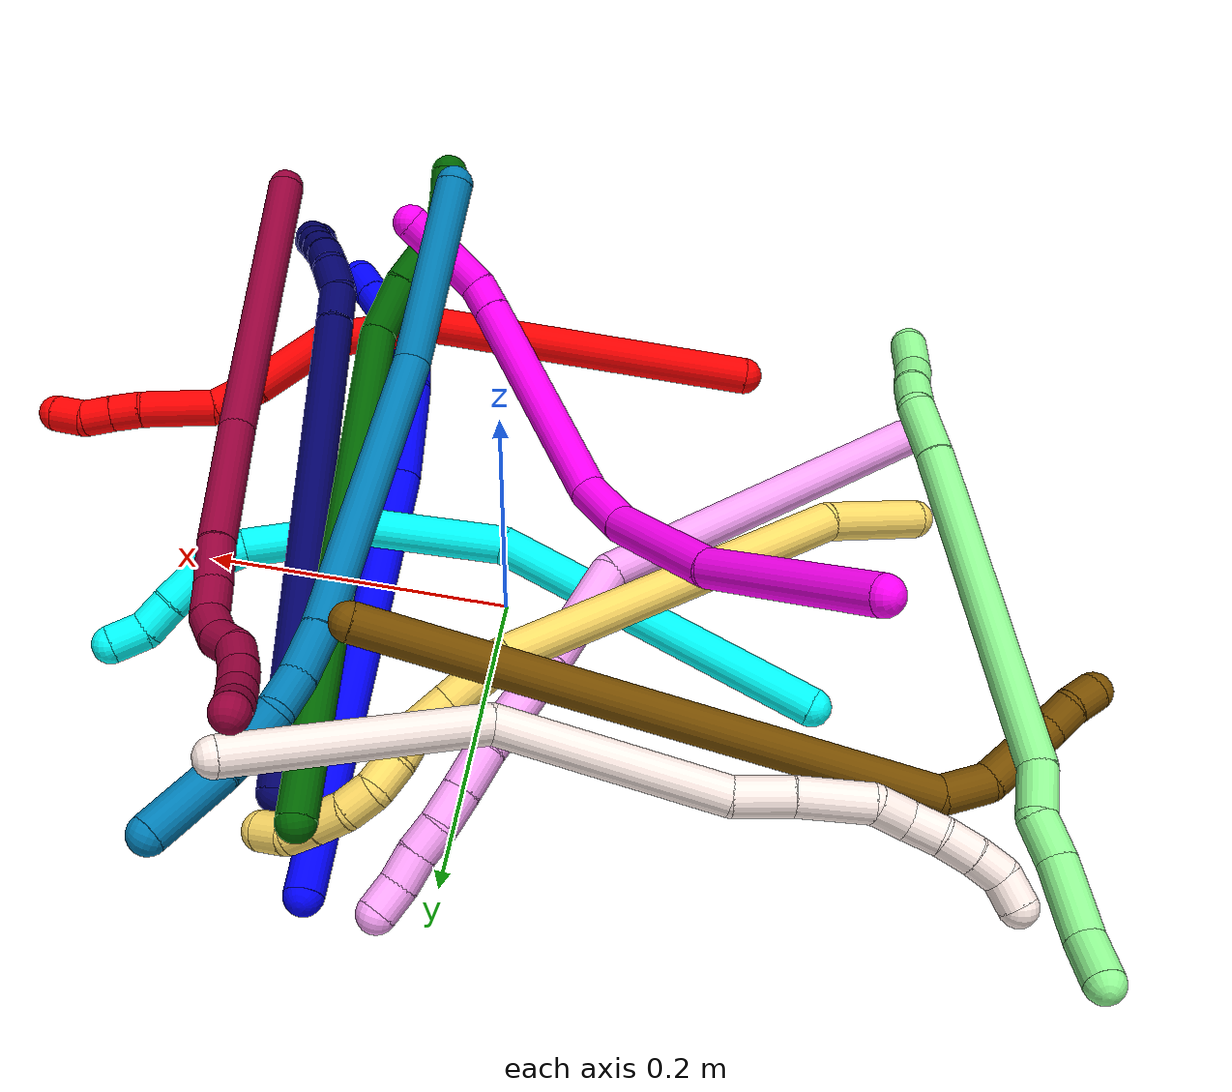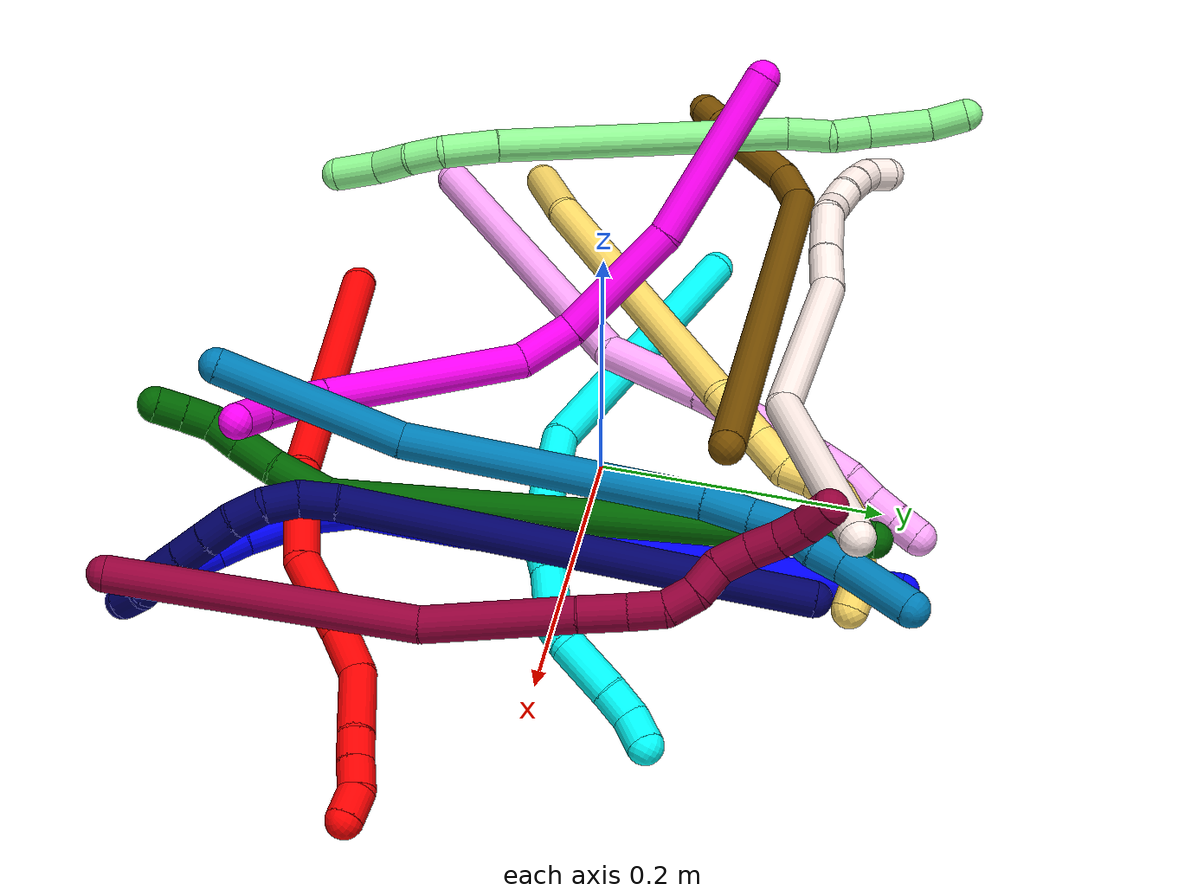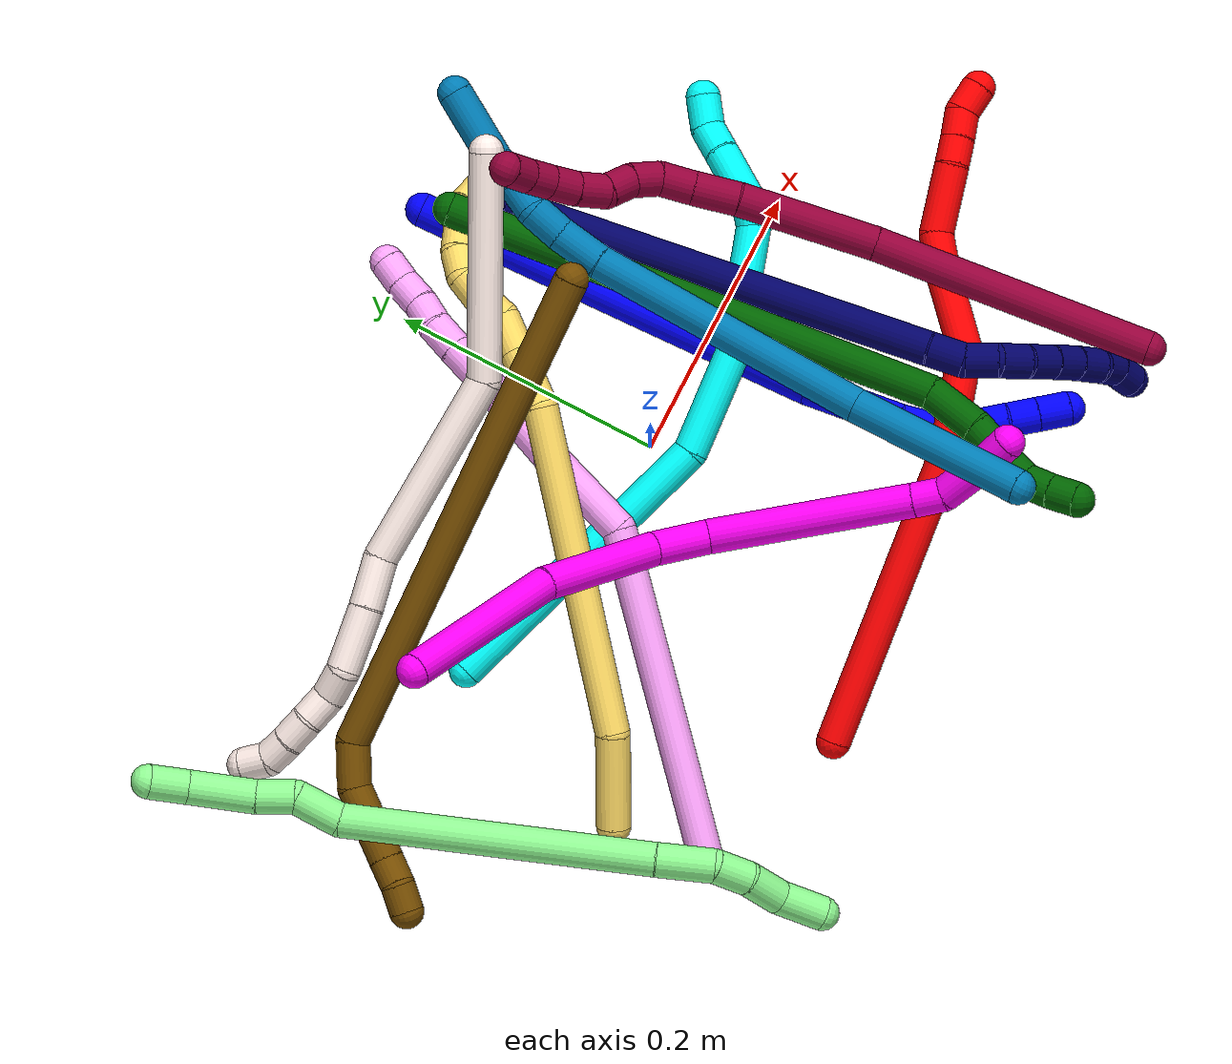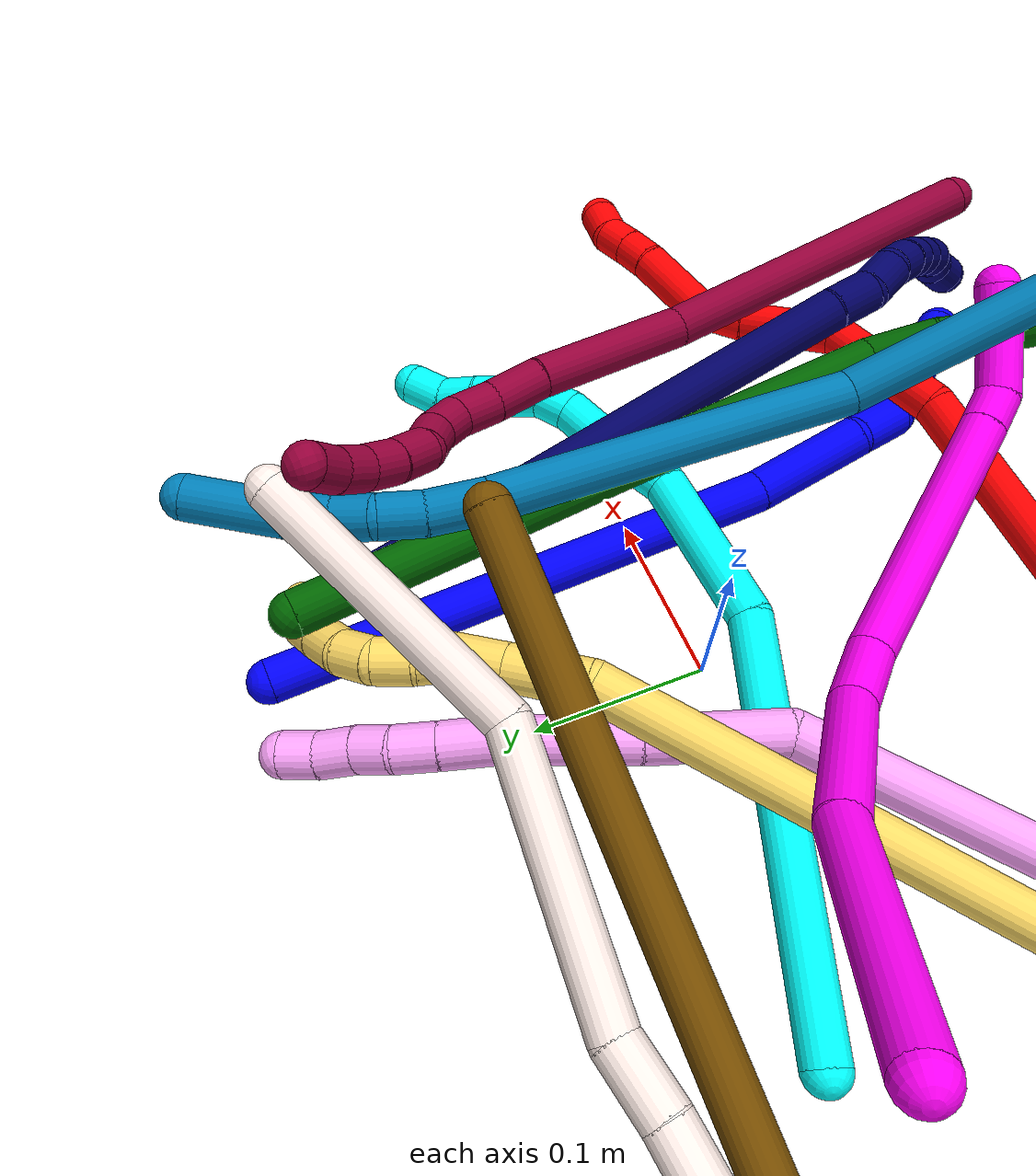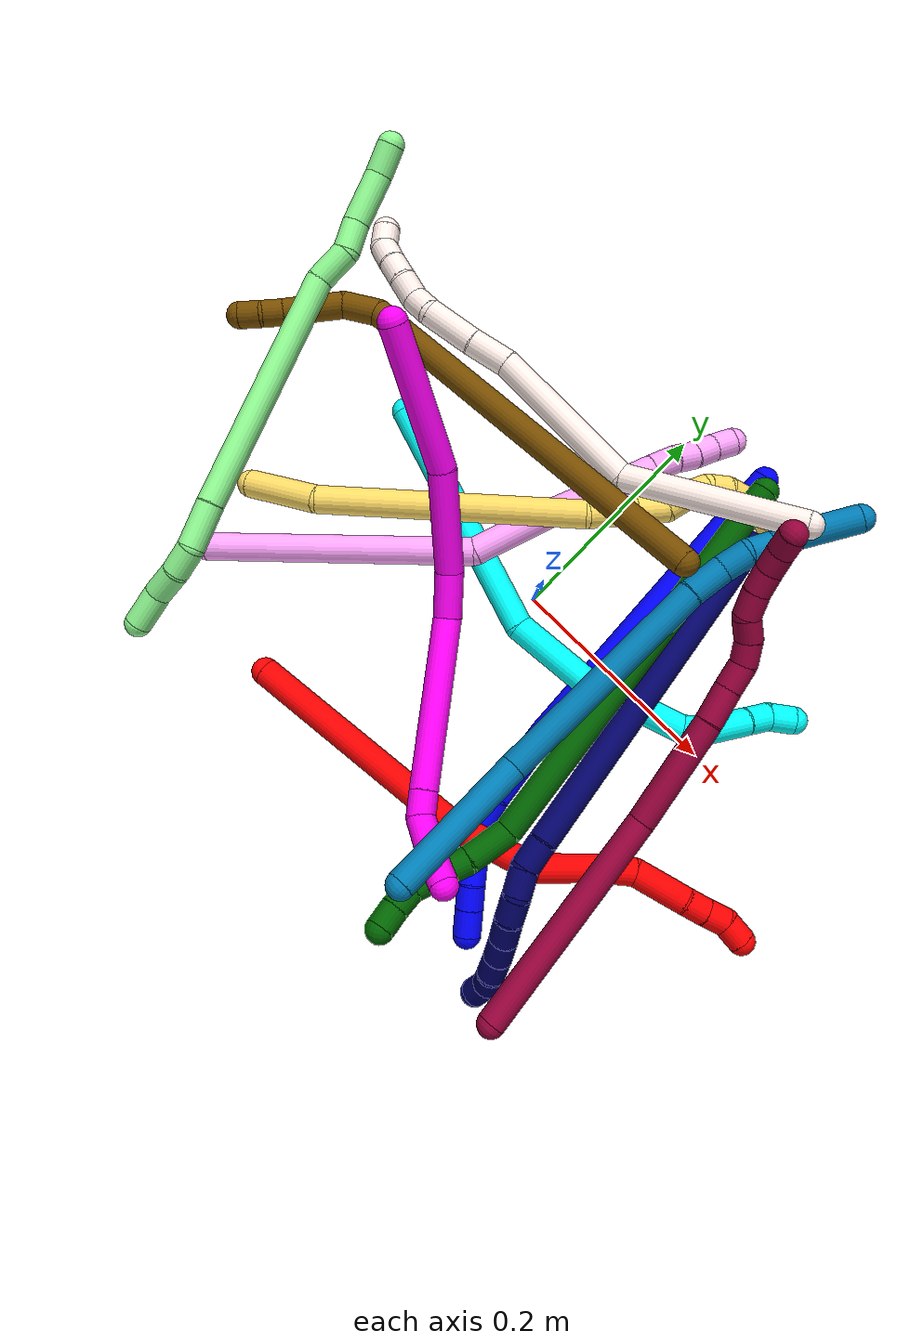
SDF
<sdf version="1.7">
 <world name="default">
  <plugin name="TubeGeneratorPlugin" filename="libtube_generator_plugin.so"/>
  <model name="photoneo_s_sensor">
   <static>1</static>
   <pose>0 0 2 1.57079 1.57079 3.14159</pose>
   <link name="link">
    <inertial><mass>0.1</mass></inertial>
    <sensor name="sensor" type="depth">
     <update_rate>30</update_rate>
     <camera>
      <horizontal_fov>1.22</horizontal_fov>
      <image><width>1920</width><height>1200</height><format>B8G8R8</format></image>
      <clip><near>0.1</near><far>4</far></clip>
      <depth_camera><output>points</output></depth_camera>
     </camera>
     <plugin name="camera_plugin" filename="libgazebo_ros_depth_camera.so">
      <baseline>0.2</baseline>
      <alwaysOn>1</alwaysOn>
      <updateRate>0.0</updateRate>
      <cameraName>camera_ir</cameraName>
      <imageTopicName>/camera/color/image_raw</imageTopicName>
      <cameraInfoTopicName>/camera/color/camera_info</cameraInfoTopicName>
      <depthImageTopicName>/camera/depth/image_raw</depthImageTopicName>
      <depthImageCameraInfoTopicName>/camera/depth/camera_info</depthImageCameraInfoTopicName>
      <pointCloudTopicName>/camera/depth/points</pointCloudTopicName>
      <frameName>fr_optical</frameName>
      <pointCloudCutoff>0.1</pointCloudCutoff>
      <pointCloudCutoffMax>2.0</pointCloudCutoffMax>
      <distortionK1>0</distortionK1>
      <distortionK2>0</distortionK2>
      <distortionK3>0</distortionK3>
      <distortionT1>0</distortionT1>
      <distortionT2>0</distortionT2>
      <CxPrime>0</CxPrime>
      <Cx>0</Cx>
      <Cy>0</Cy>
      <focalLength>0</focalLength>
      <hackBaseline>0</hackBaseline>
     </plugin>
    </sensor>
   </link>
  </model>
  <gravity>0 0 -9.8</gravity>
  <magnetic_field>6e-06 2.3e-05 -4.2e-05</magnetic_field>
  <atmosphere type="adiabatic"/>
  <physics name="default_physics" default="0" type="ode">
   <max_step_size>0.003</max_step_size>
   <real_time_factor>1</real_time_factor>
   <real_time_update_rate>1000</real_time_update_rate>
   <max_contacts>10000</max_contacts>
   <ode>
    <solver>
     <type>quick</type>
     <iters>100</iters>
     <sor>1.3</sor>
     <use_dynamic_moi_rescaling>0</use_dynamic_moi_rescaling>
    </solver>
    <constraints>
     <contact_max_correcting_vel>0</contact_max_correcting_vel>
     <contact_surface_layer>0.001</contact_surface_layer>
     <cfm>0</cfm>
     <erp>0.2</erp>
    </constraints>
   </ode>
  </physics>
  <scene><ambient>0.4 0.4 0.4 1</ambient><background>0.7 0.7 0.7 1</background><shadows>0</shadows></scene>
  <audio><device>default</device></audio>
  <spherical_coordinates>
   <surface_model>EARTH_WGS84</surface_model>
   <latitude_deg>0</latitude_deg>
   <longitude_deg>0</longitude_deg>
   <elevation>0</elevation>
   <heading_deg>0</heading_deg>
  </spherical_coordinates>
  <model name="bin">
   <static>1</static>
   <link name="bottom">
    <collision name="collision-bottom">
     <pose>0 0 -0.01 0 -0 0</pose>
     <geometry><box><size>0.8 0.6 0.02</size></box></geometry>
     <surface>
      <friction><ode><mu>100</mu><mu2>100</mu2></ode></friction>
      <contact><collide_bitmask>65535</collide_bitmask></contact>
     </surface>
    </collision>
   </link>
   <link name="west_wall">
    <collision name="collision-west_wall">
     <pose>-0.41 0 0.1 0 -0 0</pose>
     <geometry><box><size>0.02 0.6 0.2</size></box></geometry>
     <surface>
      <friction><ode><mu>100</mu><mu2>100</mu2></ode></friction>
      <contact><collide_bitmask>65535</collide_bitmask></contact>
     </surface>
    </collision>
   </link>
   <link name="east_wall">
    <collision name="collision-east_wall">
     <pose>0.41 0 0.1 0 -0 0</pose>
     <geometry><box><size>0.02 0.6 0.2</size></box></geometry>
     <surface>
      <friction><ode><mu>100</mu><mu2>100</mu2></ode></friction>
      <contact><collide_bitmask>65535</collide_bitmask></contact>
     </surface>
    </collision>
   </link>
   <link name="south_wall">
    <collision name="collision-south_wall">
     <pose>0 -0.31 0.1 0 -0 0</pose>
     <geometry><box><size>0.8 0.02 0.2</size></box></geometry>
     <surface>
      <friction><ode><mu>100</mu><mu2>100</mu2></ode></friction>
      <contact><collide_bitmask>65535</collide_bitmask></contact>
     </surface>
    </collision>
   </link>
   <link name="north_wall">
    <collision name="collision-north_wall">
     <pose>0 0.31 0.1 0 -0 0</pose>
     <geometry><box><size>0.8 0.02 0.2</size></box></geometry>
     <surface>
      <friction><ode><mu>100</mu><mu2>100</mu2></ode></friction>
      <contact><collide_bitmask>65535</collide_bitmask></contact>
     </surface>
    </collision>
   </link>
  </model>
  <model name="1">
   <static>0</static>
   <link name="1">
    <collision name="collision-cylinder-e_1_1_4">
     <pose>0.058964 -0.054342 0.129353 0.397718 0.397848 0.081205</pose>
     <geometry><cylinder><radius>0.0125</radius><length>0.304381</length></cylinder></geometry>
     <surface>
      <friction><ode><mu>1.16</mu><mu2>1.16</mu2><slip1>0</slip1><slip2>0</slip2></ode></friction>
      <contact><ode><kp>1e+06</kp><kd>1</kd><max_vel>0</max_vel><min_depth>0.001</min_depth></ode></contact>
     </surface>
    </collision>
    <visual name="visual-cylinder-e_1_1_4">
     <pose>0.058964 -0.054342 0.129353 0.397718 0.397848 0.081205</pose>
     <geometry><cylinder><radius>0.0125</radius><length>0.304381</length></cylinder></geometry>
     <material><ambient>0 0 1 1</ambient></material>
    </visual>
    <collision name="collision-cylinder-e_2_4_5">
     <pose>0.133415 -0.125952 0.2855 0.572475 0.452274 0.135223</pose>
     <geometry><cylinder><radius>0.0125</radius><length>0.070878</length></cylinder></geometry>
     <surface>
      <friction><ode><mu>1.16</mu><mu2>1.16</mu2><slip1>0</slip1><slip2>0</slip2></ode></friction>
      <contact><ode><kp>1e+06</kp><kd>1</kd><max_vel>0</max_vel><min_depth>0.001</min_depth></ode></contact>
     </surface>
    </collision>
    <visual name="visual-cylinder-e_2_4_5">
     <pose>0.133415 -0.125952 0.2855 0.572475 0.452274 0.135223</pose>
     <geometry><cylinder><radius>0.0125</radius><length>0.070878</length></cylinder></geometry>
     <material><ambient>0 0 1 1</ambient></material>
    </visual>
    <collision name="collision-cylinder-e_3_5_6">
     <pose>0.151299 -0.150065 0.327497 0.423067 0.142766 0.030708</pose>
     <geometry><cylinder><radius>0.0125</radius><length>0.03369</length></cylinder></geometry>
     <surface>
      <friction><ode><mu>1.16</mu><mu2>1.16</mu2><slip1>0</slip1><slip2>0</slip2></ode></friction>
      <contact><ode><kp>1e+06</kp><kd>1</kd><max_vel>0</max_vel><min_depth>0.001</min_depth></ode></contact>
     </surface>
    </collision>
    <visual name="visual-cylinder-e_3_5_6">
     <pose>0.151299 -0.150065 0.327497 0.423067 0.142766 0.030708</pose>
     <geometry><cylinder><radius>0.0125</radius><length>0.03369</length></cylinder></geometry>
     <material><ambient>0 0 1 1</ambient></material>
    </visual>
    <collision name="collision-cylinder-e_4_6_7">
     <pose>0.15248 -0.174143 0.357997 0.844849 -0.05273 -0.023706</pose>
     <geometry><cylinder><radius>0.0125</radius><length>0.046149</length></cylinder></geometry>
     <surface>
      <friction><ode><mu>1.16</mu><mu2>1.16</mu2><slip1>0</slip1><slip2>0</slip2></ode></friction>
      <contact><ode><kp>1e+06</kp><kd>1</kd><max_vel>0</max_vel><min_depth>0.001</min_depth></ode></contact>
     </surface>
    </collision>
    <visual name="visual-cylinder-e_4_6_7">
     <pose>0.15248 -0.174143 0.357997 0.844849 -0.05273 -0.023706</pose>
     <geometry><cylinder><radius>0.0125</radius><length>0.046149</length></cylinder></geometry>
     <material><ambient>0 0 1 1</ambient></material>
    </visual>
    <collision name="collision-cylinder-e_5_7_8">
     <pose>0.149622 -0.198438 0.380993 0.742256 -0.155877 -0.060766</pose>
     <geometry><cylinder><radius>0.0125</radius><length>0.021154</length></cylinder></geometry>
     <surface>
      <friction><ode><mu>1.16</mu><mu2>1.16</mu2><slip1>0</slip1><slip2>0</slip2></ode></friction>
      <contact><ode><kp>1e+06</kp><kd>1</kd><max_vel>0</max_vel><min_depth>0.001</min_depth></ode></contact>
     </surface>
    </collision>
    <visual name="visual-cylinder-e_5_7_8">
     <pose>0.149622 -0.198438 0.380993 0.742256 -0.155877 -0.060766</pose>
     <geometry><cylinder><radius>0.0125</radius><length>0.021154</length></cylinder></geometry>
     <material><ambient>0 0 1 1</ambient></material>
    </visual>
    <collision name="collision-cylinder-e_6_8_2">
     <pose>0.146069 -0.213348 0.397398 0.733621 -0.161604 -0.062203</pose>
     <geometry><cylinder><radius>0.0125</radius><length>0.023749</length></cylinder></geometry>
     <surface>
      <friction><ode><mu>1.16</mu><mu2>1.16</mu2><slip1>0</slip1><slip2>0</slip2></ode></friction>
      <contact><ode><kp>1e+06</kp><kd>1</kd><max_vel>0</max_vel><min_depth>0.001</min_depth></ode></contact>
     </surface>
    </collision>
    <visual name="visual-cylinder-e_6_8_2">
     <pose>0.146069 -0.213348 0.397398 0.733621 -0.161604 -0.062203</pose>
     <geometry><cylinder><radius>0.0125</radius><length>0.023749</length></cylinder></geometry>
     <material><ambient>0 0 1 1</ambient></material>
    </visual>
    <collision name="collision-sphere-2">
     <pose>0.144159 -0.221195 0.406103 0 -0 0</pose>
     <geometry><sphere><radius>0.0125</radius></sphere></geometry>
     <surface>
      <friction><ode><mu>1.16</mu><mu2>1.16</mu2><slip1>0</slip1><slip2>0</slip2></ode></friction>
      <contact><ode><kp>1e+06</kp><kd>1</kd><max_vel>0</max_vel><min_depth>0.001</min_depth></ode></contact>
     </surface>
    </collision>
    <visual name="visual-sphere-2">
     <pose>0.144159 -0.221195 0.406103 0 -0 0</pose>
     <geometry><sphere><radius>0.0125</radius></sphere></geometry>
     <material><ambient>0 0 1 1</ambient></material>
    </visual>
    <collision name="collision-sphere-4">
     <pose>0.117928 -0.108684 0.258706 0 -0 0</pose>
     <geometry><sphere><radius>0.0125</radius></sphere></geometry>
     <surface>
      <friction><ode><mu>1.16</mu><mu2>1.16</mu2><slip1>0</slip1><slip2>0</slip2></ode></friction>
      <contact><ode><kp>1e+06</kp><kd>1</kd><max_vel>0</max_vel><min_depth>0.001</min_depth></ode></contact>
     </surface>
    </collision>
    <visual name="visual-sphere-4">
     <pose>0.117928 -0.108684 0.258706 0 -0 0</pose>
     <geometry><sphere><radius>0.0125</radius></sphere></geometry>
     <material><ambient>0 0 1 1</ambient></material>
    </visual>
    <collision name="collision-sphere-1">
     <geometry><sphere><radius>0.0125</radius></sphere></geometry>
     <surface>
      <friction><ode><mu>1.16</mu><mu2>1.16</mu2><slip1>0</slip1><slip2>0</slip2></ode></friction>
      <contact><ode><kp>1e+06</kp><kd>1</kd><max_vel>0</max_vel><min_depth>0.001</min_depth></ode></contact>
     </surface>
    </collision>
    <visual name="visual-sphere-1">
     <geometry><sphere><radius>0.0125</radius></sphere></geometry>
     <material><ambient>0 0 1 1</ambient></material>
    </visual>
    <collision name="collision-sphere-8">
     <pose>0.14798 -0.205501 0.388693 0 -0 0</pose>
     <geometry><sphere><radius>0.0125</radius></sphere></geometry>
     <surface>
      <friction><ode><mu>1.16</mu><mu2>1.16</mu2><slip1>0</slip1><slip2>0</slip2></ode></friction>
      <contact><ode><kp>1e+06</kp><kd>1</kd><max_vel>0</max_vel><min_depth>0.001</min_depth></ode></contact>
     </surface>
    </collision>
    <visual name="visual-sphere-8">
     <pose>0.14798 -0.205501 0.388693 0 -0 0</pose>
     <geometry><sphere><radius>0.0125</radius></sphere></geometry>
     <material><ambient>0 0 1 1</ambient></material>
    </visual>
    <collision name="collision-sphere-5">
     <pose>0.148903 -0.143219 0.312293 0 -0 0</pose>
     <geometry><sphere><radius>0.0125</radius></sphere></geometry>
     <surface>
      <friction><ode><mu>1.16</mu><mu2>1.16</mu2><slip1>0</slip1><slip2>0</slip2></ode></friction>
      <contact><ode><kp>1e+06</kp><kd>1</kd><max_vel>0</max_vel><min_depth>0.001</min_depth></ode></contact>
     </surface>
    </collision>
    <visual name="visual-sphere-5">
     <pose>0.148903 -0.143219 0.312293 0 -0 0</pose>
     <geometry><sphere><radius>0.0125</radius></sphere></geometry>
     <material><ambient>0 0 1 1</ambient></material>
    </visual>
    <collision name="collision-sphere-6">
     <pose>0.153696 -0.15691 0.3427 0 -0 0</pose>
     <geometry><sphere><radius>0.0125</radius></sphere></geometry>
     <surface>
      <friction><ode><mu>1.16</mu><mu2>1.16</mu2><slip1>0</slip1><slip2>0</slip2></ode></friction>
      <contact><ode><kp>1e+06</kp><kd>1</kd><max_vel>0</max_vel><min_depth>0.001</min_depth></ode></contact>
     </surface>
    </collision>
    <visual name="visual-sphere-6">
     <pose>0.153696 -0.15691 0.3427 0 -0 0</pose>
     <geometry><sphere><radius>0.0125</radius></sphere></geometry>
     <material><ambient>0 0 1 1</ambient></material>
    </visual>
    <collision name="collision-sphere-7">
     <pose>0.151264 -0.191375 0.373293 0 -0 0</pose>
     <geometry><sphere><radius>0.0125</radius></sphere></geometry>
     <surface>
      <friction><ode><mu>1.16</mu><mu2>1.16</mu2><slip1>0</slip1><slip2>0</slip2></ode></friction>
      <contact><ode><kp>1e+06</kp><kd>1</kd><max_vel>0</max_vel><min_depth>0.001</min_depth></ode></contact>
     </surface>
    </collision>
    <visual name="visual-sphere-7">
     <pose>0.151264 -0.191375 0.373293 0 -0 0</pose>
     <geometry><sphere><radius>0.0125</radius></sphere></geometry>
     <material><ambient>0 0 1 1</ambient></material>
    </visual>
    <inertial>
     <pose>0.092343 -0.095649 0.209319 0 -0 0</pose>
     <mass>0.5</mass>
     <inertia>
      <ixx>0.002409</ixx>
      <ixy>0</ixy>
      <ixz>0</ixz>
      <iyy>0.002404</iyy>
      <iyz>0</iyz>
      <izz>-2.6e-05</izz>
     </inertia>
    </inertial>
   </link>
   <pose>0.075067 0.223698 0.011494 -2.34757 -0.721909 -2.55317</pose>
  </model>
  <model name="2">
   <static>0</static>
   <link name="2">
    <collision name="collision-cylinder-e_1_1_4">
     <pose>0.103478 0.016603 0.032128 -0.476989 1.23458 -0.341781</pose>
     <geometry><cylinder><radius>0.0125</radius><length>0.219232</length></cylinder></geometry>
     <surface>
      <friction><ode><mu>1.16</mu><mu2>1.16</mu2><slip1>0</slip1><slip2>0</slip2></ode></friction>
      <contact><ode><kp>1e+06</kp><kd>1</kd><max_vel>0</max_vel><min_depth>0.001</min_depth></ode></contact>
     </surface>
    </collision>
    <visual name="visual-cylinder-e_1_1_4">
     <pose>0.103478 0.016603 0.032128 -0.476989 1.23458 -0.341781</pose>
     <geometry><cylinder><radius>0.0125</radius><length>0.219232</length></cylinder></geometry>
     <material><ambient>1 0 0 1</ambient></material>
    </visual>
    <collision name="collision-cylinder-e_2_4_5">
     <pose>0.245098 0.03886 0.06435 -1.55416 1.42363 -1.40719</pose>
     <geometry><cylinder><radius>0.0125</radius><length>0.077117</length></cylinder></geometry>
     <surface>
      <friction><ode><mu>1.16</mu><mu2>1.16</mu2><slip1>0</slip1><slip2>0</slip2></ode></friction>
      <contact><ode><kp>1e+06</kp><kd>1</kd><max_vel>0</max_vel><min_depth>0.001</min_depth></ode></contact>
     </surface>
    </collision>
    <visual name="visual-cylinder-e_2_4_5">
     <pose>0.245098 0.03886 0.06435 -1.55416 1.42363 -1.40719</pose>
     <geometry><cylinder><radius>0.0125</radius><length>0.077117</length></cylinder></geometry>
     <material><ambient>1 0 0 1</ambient></material>
    </visual>
    <collision name="collision-cylinder-e_3_5_6">
     <pose>0.307862 0.053911 0.052501 -2.47488 1.01782 -2.03067</pose>
     <geometry><cylinder><radius>0.0125</radius><length>0.057869</length></cylinder></geometry>
     <surface>
      <friction><ode><mu>1.16</mu><mu2>1.16</mu2><slip1>0</slip1><slip2>0</slip2></ode></friction>
      <contact><ode><kp>1e+06</kp><kd>1</kd><max_vel>0</max_vel><min_depth>0.001</min_depth></ode></contact>
     </surface>
    </collision>
    <visual name="visual-cylinder-e_3_5_6">
     <pose>0.307862 0.053911 0.052501 -2.47488 1.01782 -2.03067</pose>
     <geometry><cylinder><radius>0.0125</radius><length>0.057869</length></cylinder></geometry>
     <material><ambient>1 0 0 1</ambient></material>
    </visual>
    <collision name="collision-cylinder-e_4_6_7">
     <pose>0.347292 0.068872 0.035628 -2.29597 1.10556 -1.88131</pose>
     <geometry><cylinder><radius>0.0125</radius><length>0.033136</length></cylinder></geometry>
     <surface>
      <friction><ode><mu>1.16</mu><mu2>1.16</mu2><slip1>0</slip1><slip2>0</slip2></ode></friction>
      <contact><ode><kp>1e+06</kp><kd>1</kd><max_vel>0</max_vel><min_depth>0.001</min_depth></ode></contact>
     </surface>
    </collision>
    <visual name="visual-cylinder-e_4_6_7">
     <pose>0.347292 0.068872 0.035628 -2.29597 1.10556 -1.88131</pose>
     <geometry><cylinder><radius>0.0125</radius><length>0.033136</length></cylinder></geometry>
     <material><ambient>1 0 0 1</ambient></material>
    </visual>
    <collision name="collision-cylinder-e_5_7_8">
     <pose>0.386689 0.079388 0.033555 -1.04767 1.34232 -0.860211</pose>
     <geometry><cylinder><radius>0.0125</radius><length>0.050491</length></cylinder></geometry>
     <surface>
      <friction><ode><mu>1.16</mu><mu2>1.16</mu2><slip1>0</slip1><slip2>0</slip2></ode></friction>
      <contact><ode><kp>1e+06</kp><kd>1</kd><max_vel>0</max_vel><min_depth>0.001</min_depth></ode></contact>
     </surface>
    </collision>
    <visual name="visual-cylinder-e_5_7_8">
     <pose>0.386689 0.079388 0.033555 -1.04767 1.34232 -0.860211</pose>
     <geometry><cylinder><radius>0.0125</radius><length>0.050491</length></cylinder></geometry>
     <material><ambient>1 0 0 1</ambient></material>
    </visual>
    <collision name="collision-cylinder-e_6_8_9">
     <pose>0.421285 0.085343 0.036276 -1.70504 1.47007 -1.60455</pose>
     <geometry><cylinder><radius>0.0125</radius><length>0.020115</length></cylinder></geometry>
     <surface>
      <friction><ode><mu>1.16</mu><mu2>1.16</mu2><slip1>0</slip1><slip2>0</slip2></ode></friction>
      <contact><ode><kp>1e+06</kp><kd>1</kd><max_vel>0</max_vel><min_depth>0.001</min_depth></ode></contact>
     </surface>
    </collision>
    <visual name="visual-cylinder-e_6_8_9">
     <pose>0.421285 0.085343 0.036276 -1.70504 1.47007 -1.60455</pose>
     <geometry><cylinder><radius>0.0125</radius><length>0.020115</length></cylinder></geometry>
     <material><ambient>1 0 0 1</ambient></material>
    </visual>
    <collision name="collision-cylinder-e_7_9_10">
     <pose>0.441351 0.087598 0.03558 -1.99146 1.43519 -1.86412</pose>
     <geometry><cylinder><radius>0.0125</radius><length>0.020305</length></cylinder></geometry>
     <surface>
      <friction><ode><mu>1.16</mu><mu2>1.16</mu2><slip1>0</slip1><slip2>0</slip2></ode></friction>
      <contact><ode><kp>1e+06</kp><kd>1</kd><max_vel>0</max_vel><min_depth>0.001</min_depth></ode></contact>
     </surface>
    </collision>
    <visual name="visual-cylinder-e_7_9_10">
     <pose>0.441351 0.087598 0.03558 -1.99146 1.43519 -1.86412</pose>
     <geometry><cylinder><radius>0.0125</radius><length>0.020305</length></cylinder></geometry>
     <material><ambient>1 0 0 1</ambient></material>
    </visual>
    <collision name="collision-cylinder-e_8_10_2">
     <pose>0.461851 0.087113 0.037481 0.614902 1.28983 0.468897</pose>
     <geometry><cylinder><radius>0.0125</radius><length>0.021734</length></cylinder></geometry>
     <surface>
      <friction><ode><mu>1.16</mu><mu2>1.16</mu2><slip1>0</slip1><slip2>0</slip2></ode></friction>
      <contact><ode><kp>1e+06</kp><kd>1</kd><max_vel>0</max_vel><min_depth>0.001</min_depth></ode></contact>
     </surface>
    </collision>
    <visual name="visual-cylinder-e_8_10_2">
     <pose>0.461851 0.087113 0.037481 0.614902 1.28983 0.468897</pose>
     <geometry><cylinder><radius>0.0125</radius><length>0.021734</length></cylinder></geometry>
     <material><ambient>1 0 0 1</ambient></material>
    </visual>
    <collision name="collision-sphere-2">
     <pose>0.472292 0.085375 0.039942 0 -0 0</pose>
     <geometry><sphere><radius>0.0125</radius></sphere></geometry>
     <surface>
      <friction><ode><mu>1.16</mu><mu2>1.16</mu2><slip1>0</slip1><slip2>0</slip2></ode></friction>
      <contact><ode><kp>1e+06</kp><kd>1</kd><max_vel>0</max_vel><min_depth>0.001</min_depth></ode></contact>
     </surface>
    </collision>
    <visual name="visual-sphere-2">
     <pose>0.472292 0.085375 0.039942 0 -0 0</pose>
     <geometry><sphere><radius>0.0125</radius></sphere></geometry>
     <material><ambient>1 0 0 1</ambient></material>
    </visual>
    <collision name="collision-sphere-10">
     <pose>0.45141 0.088851 0.03502 0 -0 0</pose>
     <geometry><sphere><radius>0.0125</radius></sphere></geometry>
     <surface>
      <friction><ode><mu>1.16</mu><mu2>1.16</mu2><slip1>0</slip1><slip2>0</slip2></ode></friction>
      <contact><ode><kp>1e+06</kp><kd>1</kd><max_vel>0</max_vel><min_depth>0.001</min_depth></ode></contact>
     </surface>
    </collision>
    <visual name="visual-sphere-10">
     <pose>0.45141 0.088851 0.03502 0 -0 0</pose>
     <geometry><sphere><radius>0.0125</radius></sphere></geometry>
     <material><ambient>1 0 0 1</ambient></material>
    </visual>
    <collision name="collision-sphere-9">
     <pose>0.431292 0.086346 0.036141 0 -0 0</pose>
     <geometry><sphere><radius>0.0125</radius></sphere></geometry>
     <surface>
      <friction><ode><mu>1.16</mu><mu2>1.16</mu2><slip1>0</slip1><slip2>0</slip2></ode></friction>
      <contact><ode><kp>1e+06</kp><kd>1</kd><max_vel>0</max_vel><min_depth>0.001</min_depth></ode></contact>
     </surface>
    </collision>
    <visual name="visual-sphere-9">
     <pose>0.431292 0.086346 0.036141 0 -0 0</pose>
     <geometry><sphere><radius>0.0125</radius></sphere></geometry>
     <material><ambient>1 0 0 1</ambient></material>
    </visual>
    <collision name="collision-sphere-4">
     <pose>0.206957 0.033207 0.064256 0 -0 0</pose>
     <geometry><sphere><radius>0.0125</radius></sphere></geometry>
     <surface>
      <friction><ode><mu>1.16</mu><mu2>1.16</mu2><slip1>0</slip1><slip2>0</slip2></ode></friction>
      <contact><ode><kp>1e+06</kp><kd>1</kd><max_vel>0</max_vel><min_depth>0.001</min_depth></ode></contact>
     </surface>
    </collision>
    <visual name="visual-sphere-4">
     <pose>0.206957 0.033207 0.064256 0 -0 0</pose>
     <geometry><sphere><radius>0.0125</radius></sphere></geometry>
     <material><ambient>1 0 0 1</ambient></material>
    </visual>
    <collision name="collision-sphere-1">
     <geometry><sphere><radius>0.0125</radius></sphere></geometry>
     <surface>
      <friction><ode><mu>1.16</mu><mu2>1.16</mu2><slip1>0</slip1><slip2>0</slip2></ode></friction>
      <contact><ode><kp>1e+06</kp><kd>1</kd><max_vel>0</max_vel><min_depth>0.001</min_depth></ode></contact>
     </surface>
    </collision>
    <visual name="visual-sphere-1">
     <geometry><sphere><radius>0.0125</radius></sphere></geometry>
     <material><ambient>1 0 0 1</ambient></material>
    </visual>
    <collision name="collision-sphere-8">
     <pose>0.411278 0.084341 0.036411 0 -0 0</pose>
     <geometry><sphere><radius>0.0125</radius></sphere></geometry>
     <surface>
      <friction><ode><mu>1.16</mu><mu2>1.16</mu2><slip1>0</slip1><slip2>0</slip2></ode></friction>
      <contact><ode><kp>1e+06</kp><kd>1</kd><max_vel>0</max_vel><min_depth>0.001</min_depth></ode></contact>
     </surface>
    </collision>
    <visual name="visual-sphere-8">
     <pose>0.411278 0.084341 0.036411 0 -0 0</pose>
     <geometry><sphere><radius>0.0125</radius></sphere></geometry>
     <material><ambient>1 0 0 1</ambient></material>
    </visual>
    <collision name="collision-sphere-5">
     <pose>0.28324 0.044513 0.064444 0 -0 0</pose>
     <geometry><sphere><radius>0.0125</radius></sphere></geometry>
     <surface>
      <friction><ode><mu>1.16</mu><mu2>1.16</mu2><slip1>0</slip1><slip2>0</slip2></ode></friction>
      <contact><ode><kp>1e+06</kp><kd>1</kd><max_vel>0</max_vel><min_depth>0.001</min_depth></ode></contact>
     </surface>
    </collision>
    <visual name="visual-sphere-5">
     <pose>0.28324 0.044513 0.064444 0 -0 0</pose>
     <geometry><sphere><radius>0.0125</radius></sphere></geometry>
     <material><ambient>1 0 0 1</ambient></material>
    </visual>
    <collision name="collision-sphere-6">
     <pose>0.332485 0.063309 0.040558 0 -0 0</pose>
     <geometry><sphere><radius>0.0125</radius></sphere></geometry>
     <surface>
      <friction><ode><mu>1.16</mu><mu2>1.16</mu2><slip1>0</slip1><slip2>0</slip2></ode></friction>
      <contact><ode><kp>1e+06</kp><kd>1</kd><max_vel>0</max_vel><min_depth>0.001</min_depth></ode></contact>
     </surface>
    </collision>
    <visual name="visual-sphere-6">
     <pose>0.332485 0.063309 0.040558 0 -0 0</pose>
     <geometry><sphere><radius>0.0125</radius></sphere></geometry>
     <material><ambient>1 0 0 1</ambient></material>
    </visual>
    <collision name="collision-sphere-7">
     <pose>0.362099 0.074435 0.030698 0 -0 0</pose>
     <geometry><sphere><radius>0.0125</radius></sphere></geometry>
     <surface>
      <friction><ode><mu>1.16</mu><mu2>1.16</mu2><slip1>0</slip1><slip2>0</slip2></ode></friction>
      <contact><ode><kp>1e+06</kp><kd>1</kd><max_vel>0</max_vel><min_depth>0.001</min_depth></ode></contact>
     </surface>
    </collision>
    <visual name="visual-sphere-7">
     <pose>0.362099 0.074435 0.030698 0 -0 0</pose>
     <geometry><sphere><radius>0.0125</radius></sphere></geometry>
     <material><ambient>1 0 0 1</ambient></material>
    </visual>
    <inertial>
     <pose>0.235818 0.042872 0.040371 0 -0 0</pose>
     <mass>0.5</mass>
     <inertia>
      <ixx>0.000194</ixx>
      <ixy>0</ixy>
      <ixz>0</ixz>
      <iyy>0.000837</iyy>
      <iyz>0</iyz>
      <izz>-0.001061</izz>
     </inertia>
    </inertial>
   </link>
   <pose>-0.127298 -0.213635 0.011496 0.679983 0.177536 0.174878</pose>
  </model>
  <model name="3">
   <static>0</static>
   <link name="3">
    <collision name="collision-cylinder-e_1_1_4">
     <pose>0.060718 -0.030305 -0.088493 2.81165 0.575759 2.1172</pose>
     <geometry><cylinder><radius>0.0125</radius><length>0.223034</length></cylinder></geometry>
     <surface>
      <friction><ode><mu>1.16</mu><mu2>1.16</mu2><slip1>0</slip1><slip2>0</slip2></ode></friction>
      <contact><ode><kp>1e+06</kp><kd>1</kd><max_vel>0</max_vel><min_depth>0.001</min_depth></ode></contact>
     </surface>
    </collision>
    <visual name="visual-cylinder-e_1_1_4">
     <pose>0.060718 -0.030305 -0.088493 2.81165 0.575759 2.1172</pose>
     <geometry><cylinder><radius>0.0125</radius><length>0.223034</length></cylinder></geometry>
     <material><ambient>0.003922 1 0.996078 1</ambient></material>
    </visual>
    <collision name="collision-cylinder-e_2_4_5">
     <pose>0.152887 -0.056336 -0.210588 -3.01507 0.748348 -2.82172</pose>
     <geometry><cylinder><radius>0.0125</radius><length>0.092446</length></cylinder></geometry>
     <surface>
      <friction><ode><mu>1.16</mu><mu2>1.16</mu2><slip1>0</slip1><slip2>0</slip2></ode></friction>
      <contact><ode><kp>1e+06</kp><kd>1</kd><max_vel>0</max_vel><min_depth>0.001</min_depth></ode></contact>
     </surface>
    </collision>
    <visual name="visual-cylinder-e_2_4_5">
     <pose>0.152887 -0.056336 -0.210588 -3.01507 0.748348 -2.82172</pose>
     <geometry><cylinder><radius>0.0125</radius><length>0.092446</length></cylinder></geometry>
     <material><ambient>0.003922 1 0.996078 1</ambient></material>
    </visual>
    <collision name="collision-cylinder-e_3_5_6">
     <pose>0.196103 -0.043989 -0.255647 -2.52776 0.698287 -1.70899</pose>
     <geometry><cylinder><radius>0.0125</radius><length>0.036599</length></cylinder></geometry>
     <surface>
      <friction><ode><mu>1.16</mu><mu2>1.16</mu2><slip1>0</slip1><slip2>0</slip2></ode></friction>
      <contact><ode><kp>1e+06</kp><kd>1</kd><max_vel>0</max_vel><min_depth>0.001</min_depth></ode></contact>
     </surface>
    </collision>
    <visual name="visual-cylinder-e_3_5_6">
     <pose>0.196103 -0.043989 -0.255647 -2.52776 0.698287 -1.70899</pose>
     <geometry><cylinder><radius>0.0125</radius><length>0.036599</length></cylinder></geometry>
     <material><ambient>0.003922 1 0.996078 1</ambient></material>
    </visual>
    <collision name="collision-cylinder-e_4_6_7">
     <pose>0.220738 -0.028617 -0.281456 -2.67115 0.674369 -1.9423</pose>
     <geometry><cylinder><radius>0.0125</radius><length>0.041223</length></cylinder></geometry>
     <surface>
      <friction><ode><mu>1.16</mu><mu2>1.16</mu2><slip1>0</slip1><slip2>0</slip2></ode></friction>
      <contact><ode><kp>1e+06</kp><kd>1</kd><max_vel>0</max_vel><min_depth>0.001</min_depth></ode></contact>
     </surface>
    </collision>
    <visual name="visual-cylinder-e_4_6_7">
     <pose>0.220738 -0.028617 -0.281456 -2.67115 0.674369 -1.9423</pose>
     <geometry><cylinder><radius>0.0125</radius><length>0.041223</length></cylinder></geometry>
     <material><ambient>0.003922 1 0.996078 1</ambient></material>
    </visual>
    <collision name="collision-cylinder-e_5_7_8">
     <pose>0.240926 -0.015405 -0.299469 -2.12528 0.810694 -1.31296</pose>
     <geometry><cylinder><radius>0.0125</radius><length>0.020195</length></cylinder></geometry>
     <surface>
      <friction><ode><mu>1.16</mu><mu2>1.16</mu2><slip1>0</slip1><slip2>0</slip2></ode></friction>
      <contact><ode><kp>1e+06</kp><kd>1</kd><max_vel>0</max_vel><min_depth>0.001</min_depth></ode></contact>
     </surface>
    </collision>
    <visual name="visual-cylinder-e_5_7_8">
     <pose>0.240926 -0.015405 -0.299469 -2.12528 0.810694 -1.31296</pose>
     <geometry><cylinder><radius>0.0125</radius><length>0.020195</length></cylinder></geometry>
     <material><ambient>0.003922 1 0.996078 1</ambient></material>
    </visual>
    <collision name="collision-cylinder-e_6_8_9">
     <pose>0.256193 0.007893 -0.309852 -1.93968 0.403125 -0.579363</pose>
     <geometry><cylinder><radius>0.0125</radius><length>0.040522</length></cylinder></geometry>
     <surface>
      <friction><ode><mu>1.16</mu><mu2>1.16</mu2><slip1>0</slip1><slip2>0</slip2></ode></friction>
      <contact><ode><kp>1e+06</kp><kd>1</kd><max_vel>0</max_vel><min_depth>0.001</min_depth></ode></contact>
     </surface>
    </collision>
    <visual name="visual-cylinder-e_6_8_9">
     <pose>0.256193 0.007893 -0.309852 -1.93968 0.403125 -0.579363</pose>
     <geometry><cylinder><radius>0.0125</radius><length>0.040522</length></cylinder></geometry>
     <material><ambient>0.003922 1 0.996078 1</ambient></material>
    </visual>
    <collision name="collision-cylinder-e_7_9_10">
     <pose>0.267495 0.03511 -0.320878 -1.98351 0.302824 -0.45854</pose>
     <geometry><cylinder><radius>0.0125</radius><length>0.022495</length></cylinder></geometry>
     <surface>
      <friction><ode><mu>1.16</mu><mu2>1.16</mu2><slip1>0</slip1><slip2>0</slip2></ode></friction>
      <contact><ode><kp>1e+06</kp><kd>1</kd><max_vel>0</max_vel><min_depth>0.001</min_depth></ode></contact>
     </surface>
    </collision>
    <visual name="visual-cylinder-e_7_9_10">
     <pose>0.267495 0.03511 -0.320878 -1.98351 0.302824 -0.45854</pose>
     <geometry><cylinder><radius>0.0125</radius><length>0.022495</length></cylinder></geometry>
     <material><ambient>0.003922 1 0.996078 1</ambient></material>
    </visual>
    <collision name="collision-cylinder-e_8_10_2">
     <pose>0.278213 0.051981 -0.33103 -2.26403 0.677797 -1.28844</pose>
     <geometry><cylinder><radius>0.0125</radius><length>0.023487</length></cylinder></geometry>
     <surface>
      <friction><ode><mu>1.16</mu><mu2>1.16</mu2><slip1>0</slip1><slip2>0</slip2></ode></friction>
      <contact><ode><kp>1e+06</kp><kd>1</kd><max_vel>0</max_vel><min_depth>0.001</min_depth></ode></contact>
     </surface>
    </collision>
    <visual name="visual-cylinder-e_8_10_2">
     <pose>0.278213 0.051981 -0.33103 -2.26403 0.677797 -1.28844</pose>
     <geometry><cylinder><radius>0.0125</radius><length>0.023487</length></cylinder></geometry>
     <material><ambient>0.003922 1 0.996078 1</ambient></material>
    </visual>
    <collision name="collision-sphere-2">
     <pose>0.285577 0.059017 -0.336875 0 -0 0</pose>
     <geometry><sphere><radius>0.0125</radius></sphere></geometry>
     <surface>
      <friction><ode><mu>1.16</mu><mu2>1.16</mu2><slip1>0</slip1><slip2>0</slip2></ode></friction>
      <contact><ode><kp>1e+06</kp><kd>1</kd><max_vel>0</max_vel><min_depth>0.001</min_depth></ode></contact>
     </surface>
    </collision>
    <visual name="visual-sphere-2">
     <pose>0.285577 0.059017 -0.336875 0 -0 0</pose>
     <geometry><sphere><radius>0.0125</radius></sphere></geometry>
     <material><ambient>0.003922 1 0.996078 1</ambient></material>
    </visual>
    <collision name="collision-sphere-10">
     <pose>0.270849 0.044945 -0.325184 0 -0 0</pose>
     <geometry><sphere><radius>0.0125</radius></sphere></geometry>
     <surface>
      <friction><ode><mu>1.16</mu><mu2>1.16</mu2><slip1>0</slip1><slip2>0</slip2></ode></friction>
      <contact><ode><kp>1e+06</kp><kd>1</kd><max_vel>0</max_vel><min_depth>0.001</min_depth></ode></contact>
     </surface>
    </collision>
    <visual name="visual-sphere-10">
     <pose>0.270849 0.044945 -0.325184 0 -0 0</pose>
     <geometry><sphere><radius>0.0125</radius></sphere></geometry>
     <material><ambient>0.003922 1 0.996078 1</ambient></material>
    </visual>
    <collision name="collision-sphere-9">
     <pose>0.264141 0.025276 -0.316572 0 -0 0</pose>
     <geometry><sphere><radius>0.0125</radius></sphere></geometry>
     <surface>
      <friction><ode><mu>1.16</mu><mu2>1.16</mu2><slip1>0</slip1><slip2>0</slip2></ode></friction>
      <contact><ode><kp>1e+06</kp><kd>1</kd><max_vel>0</max_vel><min_depth>0.001</min_depth></ode></contact>
     </surface>
    </collision>
    <visual name="visual-sphere-9">
     <pose>0.264141 0.025276 -0.316572 0 -0 0</pose>
     <geometry><sphere><radius>0.0125</radius></sphere></geometry>
     <material><ambient>0.003922 1 0.996078 1</ambient></material>
    </visual>
    <collision name="collision-sphere-4">
     <pose>0.121436 -0.06061 -0.176986 0 -0 0</pose>
     <geometry><sphere><radius>0.0125</radius></sphere></geometry>
     <surface>
      <friction><ode><mu>1.16</mu><mu2>1.16</mu2><slip1>0</slip1><slip2>0</slip2></ode></friction>
      <contact><ode><kp>1e+06</kp><kd>1</kd><max_vel>0</max_vel><min_depth>0.001</min_depth></ode></contact>
     </surface>
    </collision>
    <visual name="visual-sphere-4">
     <pose>0.121436 -0.06061 -0.176986 0 -0 0</pose>
     <geometry><sphere><radius>0.0125</radius></sphere></geometry>
     <material><ambient>0.003922 1 0.996078 1</ambient></material>
    </visual>
    <collision name="collision-sphere-1">
     <geometry><sphere><radius>0.0125</radius></sphere></geometry>
     <surface>
      <friction><ode><mu>1.16</mu><mu2>1.16</mu2><slip1>0</slip1><slip2>0</slip2></ode></friction>
      <contact><ode><kp>1e+06</kp><kd>1</kd><max_vel>0</max_vel><min_depth>0.001</min_depth></ode></contact>
     </surface>
    </collision>
    <visual name="visual-sphere-1">
     <geometry><sphere><radius>0.0125</radius></sphere></geometry>
     <material><ambient>0.003922 1 0.996078 1</ambient></material>
    </visual>
    <collision name="collision-sphere-8">
     <pose>0.248245 -0.00949 -0.303132 0 -0 0</pose>
     <geometry><sphere><radius>0.0125</radius></sphere></geometry>
     <surface>
      <friction><ode><mu>1.16</mu><mu2>1.16</mu2><slip1>0</slip1><slip2>0</slip2></ode></friction>
      <contact><ode><kp>1e+06</kp><kd>1</kd><max_vel>0</max_vel><min_depth>0.001</min_depth></ode></contact>
     </surface>
    </collision>
    <visual name="visual-sphere-8">
     <pose>0.248245 -0.00949 -0.303132 0 -0 0</pose>
     <geometry><sphere><radius>0.0125</radius></sphere></geometry>
     <material><ambient>0.003922 1 0.996078 1</ambient></material>
    </visual>
    <collision name="collision-sphere-5">
     <pose>0.184338 -0.052062 -0.24419 0 -0 0</pose>
     <geometry><sphere><radius>0.0125</radius></sphere></geometry>
     <surface>
      <friction><ode><mu>1.16</mu><mu2>1.16</mu2><slip1>0</slip1><slip2>0</slip2></ode></friction>
      <contact><ode><kp>1e+06</kp><kd>1</kd><max_vel>0</max_vel><min_depth>0.001</min_depth></ode></contact>
     </surface>
    </collision>
    <visual name="visual-sphere-5">
     <pose>0.184338 -0.052062 -0.24419 0 -0 0</pose>
     <geometry><sphere><radius>0.0125</radius></sphere></geometry>
     <material><ambient>0.003922 1 0.996078 1</ambient></material>
    </visual>
    <collision name="collision-sphere-6">
     <pose>0.207868 -0.035915 -0.267105 0 -0 0</pose>
     <geometry><sphere><radius>0.0125</radius></sphere></geometry>
     <surface>
      <friction><ode><mu>1.16</mu><mu2>1.16</mu2><slip1>0</slip1><slip2>0</slip2></ode></friction>
      <contact><ode><kp>1e+06</kp><kd>1</kd><max_vel>0</max_vel><min_depth>0.001</min_depth></ode></contact>
     </surface>
    </collision>
    <visual name="visual-sphere-6">
     <pose>0.207868 -0.035915 -0.267105 0 -0 0</pose>
     <geometry><sphere><radius>0.0125</radius></sphere></geometry>
     <material><ambient>0.003922 1 0.996078 1</ambient></material>
    </visual>
    <collision name="collision-sphere-7">
     <pose>0.233608 -0.02132 -0.295806 0 -0 0</pose>
     <geometry><sphere><radius>0.0125</radius></sphere></geometry>
     <surface>
      <friction><ode><mu>1.16</mu><mu2>1.16</mu2><slip1>0</slip1><slip2>0</slip2></ode></friction>
      <contact><ode><kp>1e+06</kp><kd>1</kd><max_vel>0</max_vel><min_depth>0.001</min_depth></ode></contact>
     </surface>
    </collision>
    <visual name="visual-sphere-7">
     <pose>0.233608 -0.02132 -0.295806 0 -0 0</pose>
     <geometry><sphere><radius>0.0125</radius></sphere></geometry>
     <material><ambient>0.003922 1 0.996078 1</ambient></material>
    </visual>
    <inertial>
     <pose>0.143502 -0.025475 -0.18752 0 -0 0</pose>
     <mass>0.5</mass>
     <inertia>
      <ixx>0.000209</ixx>
      <ixy>0</ixy>
      <ixz>0</ixz>
      <iyy>0.001315</iyy>
      <iyz>0</iyz>
      <izz>-0.000363</izz>
     </inertia>
    </inertial>
   </link>
   <pose>-0.203324 0.042405 0.011485 -0.668118 -0.815249 0.463639</pose>
  </model>
  <model name="4">
   <static>0</static>
   <link name="4">
    <collision name="collision-cylinder-e_1_1_4">
     <pose>0.001973 0.092953 -0.075895 -2.25551 0.016441 -0.034646</pose>
     <geometry><cylinder><radius>0.0125</radius><length>0.240034</length></cylinder></geometry>
     <surface>
      <friction><ode><mu>1.16</mu><mu2>1.16</mu2><slip1>0</slip1><slip2>0</slip2></ode></friction>
      <contact><ode><kp>1e+06</kp><kd>1</kd><max_vel>0</max_vel><min_depth>0.001</min_depth></ode></contact>
     </surface>
    </collision>
    <visual name="visual-cylinder-e_1_1_4">
     <pose>0.001973 0.092953 -0.075895 -2.25551 0.016441 -0.034646</pose>
     <geometry><cylinder><radius>0.0125</radius><length>0.240034</length></cylinder></geometry>
     <material><ambient>1 0.65098 0.996078 1</ambient></material>
    </visual>
    <collision name="collision-cylinder-e_2_4_5">
     <pose>0.001224 0.22243 -0.158419 -1.75034 -0.073194 0.087658</pose>
     <geometry><cylinder><radius>0.0125</radius><length>0.074443</length></cylinder></geometry>
     <surface>
      <friction><ode><mu>1.16</mu><mu2>1.16</mu2><slip1>0</slip1><slip2>0</slip2></ode></friction>
      <contact><ode><kp>1e+06</kp><kd>1</kd><max_vel>0</max_vel><min_depth>0.001</min_depth></ode></contact>
     </surface>
    </collision>
    <visual name="visual-cylinder-e_2_4_5">
     <pose>0.001224 0.22243 -0.158419 -1.75034 -0.073194 0.087658</pose>
     <geometry><cylinder><radius>0.0125</radius><length>0.074443</length></cylinder></geometry>
     <material><ambient>1 0.65098 0.996078 1</ambient></material>
    </visual>
    <collision name="collision-cylinder-e_3_5_6">
     <pose>-0.004448 0.293119 -0.173235 -1.80597 -0.083794 0.106206</pose>
     <geometry><cylinder><radius>0.0125</radius><length>0.070509</length></cylinder></geometry>
     <surface>
      <friction><ode><mu>1.16</mu><mu2>1.16</mu2><slip1>0</slip1><slip2>0</slip2></ode></friction>
      <contact><ode><kp>1e+06</kp><kd>1</kd><max_vel>0</max_vel><min_depth>0.001</min_depth></ode></contact>
     </surface>
    </collision>
    <visual name="visual-cylinder-e_3_5_6">
     <pose>-0.004448 0.293119 -0.173235 -1.80597 -0.083794 0.106206</pose>
     <geometry><cylinder><radius>0.0125</radius><length>0.070509</length></cylinder></geometry>
     <material><ambient>1 0.65098 0.996078 1</ambient></material>
    </visual>
    <collision name="collision-cylinder-e_4_6_7">
     <pose>-0.011242 0.341125 -0.184061 -1.7593 -0.266225 0.320943</pose>
     <geometry><cylinder><radius>0.0125</radius><length>0.029213</length></cylinder></geometry>
     <surface>
      <friction><ode><mu>1.16</mu><mu2>1.16</mu2><slip1>0</slip1><slip2>0</slip2></ode></friction>
      <contact><ode><kp>1e+06</kp><kd>1</kd><max_vel>0</max_vel><min_depth>0.001</min_depth></ode></contact>
     </surface>
    </collision>
    <visual name="visual-cylinder-e_4_6_7">
     <pose>-0.011242 0.341125 -0.184061 -1.7593 -0.266225 0.320943</pose>
     <geometry><cylinder><radius>0.0125</radius><length>0.029213</length></cylinder></geometry>
     <material><ambient>1 0.65098 0.996078 1</ambient></material>
    </visual>
    <collision name="collision-cylinder-e_5_7_8">
     <pose>-0.018216 0.366208 -0.189157 -1.78585 -0.265719 0.328983</pose>
     <geometry><cylinder><radius>0.0125</radius><length>0.023849</length></cylinder></geometry>
     <surface>
      <friction><ode><mu>1.16</mu><mu2>1.16</mu2><slip1>0</slip1><slip2>0</slip2></ode></friction>
      <contact><ode><kp>1e+06</kp><kd>1</kd><max_vel>0</max_vel><min_depth>0.001</min_depth></ode></contact>
     </surface>
    </collision>
    <visual name="visual-cylinder-e_5_7_8">
     <pose>-0.018216 0.366208 -0.189157 -1.78585 -0.265719 0.328983</pose>
     <geometry><cylinder><radius>0.0125</radius><length>0.023849</length></cylinder></geometry>
     <material><ambient>1 0.65098 0.996078 1</ambient></material>
    </visual>
    <collision name="collision-cylinder-e_6_8_9">
     <pose>-0.025572 0.385997 -0.194886 -1.93654 -0.432445 0.618202</pose>
     <geometry><cylinder><radius>0.0125</radius><length>0.020162</length></cylinder></geometry>
     <surface>
      <friction><ode><mu>1.16</mu><mu2>1.16</mu2><slip1>0</slip1><slip2>0</slip2></ode></friction>
      <contact><ode><kp>1e+06</kp><kd>1</kd><max_vel>0</max_vel><min_depth>0.001</min_depth></ode></contact>
     </surface>
    </collision>
    <visual name="visual-cylinder-e_6_8_9">
     <pose>-0.025572 0.385997 -0.194886 -1.93654 -0.432445 0.618202</pose>
     <geometry><cylinder><radius>0.0125</radius><length>0.020162</length></cylinder></geometry>
     <material><ambient>1 0.65098 0.996078 1</ambient></material>
    </visual>
    <collision name="collision-cylinder-e_7_9_10">
     <pose>-0.034253 0.404054 -0.200145 -1.77667 -0.430047 0.525035</pose>
     <geometry><cylinder><radius>0.0125</radius><length>0.021377</length></cylinder></geometry>
     <surface>
      <friction><ode><mu>1.16</mu><mu2>1.16</mu2><slip1>0</slip1><slip2>0</slip2></ode></friction>
      <contact><ode><kp>1e+06</kp><kd>1</kd><max_vel>0</max_vel><min_depth>0.001</min_depth></ode></contact>
     </surface>
    </collision>
    <visual name="visual-cylinder-e_7_9_10">
     <pose>-0.034253 0.404054 -0.200145 -1.77667 -0.430047 0.525035</pose>
     <geometry><cylinder><radius>0.0125</radius><length>0.021377</length></cylinder></geometry>
     <material><ambient>1 0.65098 0.996078 1</ambient></material>
    </visual>
    <collision name="collision-cylinder-e_8_10_2">
     <pose>-0.04143 0.422939 -0.205115 -1.87892 -0.269821 0.367108</pose>
     <geometry><cylinder><radius>0.0125</radius><length>0.020413</length></cylinder></geometry>
     <surface>
      <friction><ode><mu>1.16</mu><mu2>1.16</mu2><slip1>0</slip1><slip2>0</slip2></ode></friction>
      <contact><ode><kp>1e+06</kp><kd>1</kd><max_vel>0</max_vel><min_depth>0.001</min_depth></ode></contact>
     </surface>
    </collision>
    <visual name="visual-cylinder-e_8_10_2">
     <pose>-0.04143 0.422939 -0.205115 -1.87892 -0.269821 0.367108</pose>
     <geometry><cylinder><radius>0.0125</radius><length>0.020413</length></cylinder></geometry>
     <material><ambient>1 0.65098 0.996078 1</ambient></material>
    </visual>
    <collision name="collision-sphere-2">
     <pose>-0.044151 0.432312 -0.208098 0 -0 0</pose>
     <geometry><sphere><radius>0.0125</radius></sphere></geometry>
     <surface>
      <friction><ode><mu>1.16</mu><mu2>1.16</mu2><slip1>0</slip1><slip2>0</slip2></ode></friction>
      <contact><ode><kp>1e+06</kp><kd>1</kd><max_vel>0</max_vel><min_depth>0.001</min_depth></ode></contact>
     </surface>
    </collision>
    <visual name="visual-sphere-2">
     <pose>-0.044151 0.432312 -0.208098 0 -0 0</pose>
     <geometry><sphere><radius>0.0125</radius></sphere></geometry>
     <material><ambient>1 0.65098 0.996078 1</ambient></material>
    </visual>
    <collision name="collision-sphere-10">
     <pose>-0.03871 0.413565 -0.202132 0 -0 0</pose>
     <geometry><sphere><radius>0.0125</radius></sphere></geometry>
     <surface>
      <friction><ode><mu>1.16</mu><mu2>1.16</mu2><slip1>0</slip1><slip2>0</slip2></ode></friction>
      <contact><ode><kp>1e+06</kp><kd>1</kd><max_vel>0</max_vel><min_depth>0.001</min_depth></ode></contact>
     </surface>
    </collision>
    <visual name="visual-sphere-10">
     <pose>-0.03871 0.413565 -0.202132 0 -0 0</pose>
     <geometry><sphere><radius>0.0125</radius></sphere></geometry>
     <material><ambient>1 0.65098 0.996078 1</ambient></material>
    </visual>
    <collision name="collision-sphere-9">
     <pose>-0.029797 0.394544 -0.198159 0 -0 0</pose>
     <geometry><sphere><radius>0.0125</radius></sphere></geometry>
     <surface>
      <friction><ode><mu>1.16</mu><mu2>1.16</mu2><slip1>0</slip1><slip2>0</slip2></ode></friction>
      <contact><ode><kp>1e+06</kp><kd>1</kd><max_vel>0</max_vel><min_depth>0.001</min_depth></ode></contact>
     </surface>
    </collision>
    <visual name="visual-sphere-9">
     <pose>-0.029797 0.394544 -0.198159 0 -0 0</pose>
     <geometry><sphere><radius>0.0125</radius></sphere></geometry>
     <material><ambient>1 0.65098 0.996078 1</ambient></material>
    </visual>
    <collision name="collision-sphere-4">
     <pose>0.003946 0.185905 -0.15179 0 -0 0</pose>
     <geometry><sphere><radius>0.0125</radius></sphere></geometry>
     <surface>
      <friction><ode><mu>1.16</mu><mu2>1.16</mu2><slip1>0</slip1><slip2>0</slip2></ode></friction>
      <contact><ode><kp>1e+06</kp><kd>1</kd><max_vel>0</max_vel><min_depth>0.001</min_depth></ode></contact>
     </surface>
    </collision>
    <visual name="visual-sphere-4">
     <pose>0.003946 0.185905 -0.15179 0 -0 0</pose>
     <geometry><sphere><radius>0.0125</radius></sphere></geometry>
     <material><ambient>1 0.65098 0.996078 1</ambient></material>
    </visual>
    <collision name="collision-sphere-1">
     <geometry><sphere><radius>0.0125</radius></sphere></geometry>
     <surface>
      <friction><ode><mu>1.16</mu><mu2>1.16</mu2><slip1>0</slip1><slip2>0</slip2></ode></friction>
      <contact><ode><kp>1e+06</kp><kd>1</kd><max_vel>0</max_vel><min_depth>0.001</min_depth></ode></contact>
     </surface>
    </collision>
    <visual name="visual-sphere-1">
     <geometry><sphere><radius>0.0125</radius></sphere></geometry>
     <material><ambient>1 0.65098 0.996078 1</ambient></material>
    </visual>
    <collision name="collision-sphere-8">
     <pose>-0.021348 0.377449 -0.191613 0 -0 0</pose>
     <geometry><sphere><radius>0.0125</radius></sphere></geometry>
     <surface>
      <friction><ode><mu>1.16</mu><mu2>1.16</mu2><slip1>0</slip1><slip2>0</slip2></ode></friction>
      <contact><ode><kp>1e+06</kp><kd>1</kd><max_vel>0</max_vel><min_depth>0.001</min_depth></ode></contact>
     </surface>
    </collision>
    <visual name="visual-sphere-8">
     <pose>-0.021348 0.377449 -0.191613 0 -0 0</pose>
     <geometry><sphere><radius>0.0125</radius></sphere></geometry>
     <material><ambient>1 0.65098 0.996078 1</ambient></material>
    </visual>
    <collision name="collision-sphere-5">
     <pose>-0.001498 0.258955 -0.165049 0 -0 0</pose>
     <geometry><sphere><radius>0.0125</radius></sphere></geometry>
     <surface>
      <friction><ode><mu>1.16</mu><mu2>1.16</mu2><slip1>0</slip1><slip2>0</slip2></ode></friction>
      <contact><ode><kp>1e+06</kp><kd>1</kd><max_vel>0</max_vel><min_depth>0.001</min_depth></ode></contact>
     </surface>
    </collision>
    <visual name="visual-sphere-5">
     <pose>-0.001498 0.258955 -0.165049 0 -0 0</pose>
     <geometry><sphere><radius>0.0125</radius></sphere></geometry>
     <material><ambient>1 0.65098 0.996078 1</ambient></material>
    </visual>
    <collision name="collision-sphere-6">
     <pose>-0.007399 0.327283 -0.18142 0 -0 0</pose>
     <geometry><sphere><radius>0.0125</radius></sphere></geometry>
     <surface>
      <friction><ode><mu>1.16</mu><mu2>1.16</mu2><slip1>0</slip1><slip2>0</slip2></ode></friction>
      <contact><ode><kp>1e+06</kp><kd>1</kd><max_vel>0</max_vel><min_depth>0.001</min_depth></ode></contact>
     </surface>
    </collision>
    <visual name="visual-sphere-6">
     <pose>-0.007399 0.327283 -0.18142 0 -0 0</pose>
     <geometry><sphere><radius>0.0125</radius></sphere></geometry>
     <material><ambient>1 0.65098 0.996078 1</ambient></material>
    </visual>
    <collision name="collision-sphere-7">
     <pose>-0.015085 0.354967 -0.186702 0 -0 0</pose>
     <geometry><sphere><radius>0.0125</radius></sphere></geometry>
     <surface>
      <friction><ode><mu>1.16</mu><mu2>1.16</mu2><slip1>0</slip1><slip2>0</slip2></ode></friction>
      <contact><ode><kp>1e+06</kp><kd>1</kd><max_vel>0</max_vel><min_depth>0.001</min_depth></ode></contact>
     </surface>
    </collision>
    <visual name="visual-sphere-7">
     <pose>-0.015085 0.354967 -0.186702 0 -0 0</pose>
     <geometry><sphere><radius>0.0125</radius></sphere></geometry>
     <material><ambient>1 0.65098 0.996078 1</ambient></material>
    </visual>
    <inertial>
     <pose>-0.005211 0.20658 -0.129016 0 -0 0</pose>
     <mass>0.5</mass>
     <inertia>
      <ixx>0.001205</ixx>
      <ixy>0</ixy>
      <ixz>0</ixz>
      <iyy>-0.000744</iyy>
      <iyz>0</iyz>
      <izz>-0.001003</izz>
     </inertia>
    </inertial>
   </link>
   <pose>-0.241744 -0.169827 0.024006 2.5254 -1.48368 -2.67291</pose>
  </model>
  <model name="5">
   <static>0</static>
   <link name="5">
    <collision name="collision-cylinder-e_1_1_4">
     <pose>0.023674 0.019481 -0.015957 -2.25707 0.754548 -1.39355</pose>
     <geometry><cylinder><radius>0.0125</radius><length>0.069126</length></cylinder></geometry>
     <surface>
      <friction><ode><mu>1.16</mu><mu2>1.16</mu2><slip1>0</slip1><slip2>0</slip2></ode></friction>
      <contact><ode><kp>1e+06</kp><kd>1</kd><max_vel>0</max_vel><min_depth>0.001</min_depth></ode></contact>
     </surface>
    </collision>
    <visual name="visual-cylinder-e_1_1_4">
     <pose>0.023674 0.019481 -0.015957 -2.25707 0.754548 -1.39355</pose>
     <geometry><cylinder><radius>0.0125</radius><length>0.069126</length></cylinder></geometry>
     <material><ambient>1 0.858824 0.4 1</ambient></material>
    </visual>
    <collision name="collision-cylinder-e_2_4_5">
     <pose>0.101122 0.105074 -0.113719 -2.46189 0.472611 -1.19582</pose>
     <geometry><cylinder><radius>0.0125</radius><length>0.236259</length></cylinder></geometry>
     <surface>
      <friction><ode><mu>1.16</mu><mu2>1.16</mu2><slip1>0</slip1><slip2>0</slip2></ode></friction>
      <contact><ode><kp>1e+06</kp><kd>1</kd><max_vel>0</max_vel><min_depth>0.001</min_depth></ode></contact>
     </surface>
    </collision>
    <visual name="visual-cylinder-e_2_4_5">
     <pose>0.101122 0.105074 -0.113719 -2.46189 0.472611 -1.19582</pose>
     <geometry><cylinder><radius>0.0125</radius><length>0.236259</length></cylinder></geometry>
     <material><ambient>1 0.858824 0.4 1</ambient></material>
    </visual>
    <collision name="collision-cylinder-e_3_5_6">
     <pose>0.158556 0.180973 -0.214517 -2.66578 0.169656 -0.674511</pose>
     <geometry><cylinder><radius>0.0125</radius><length>0.043355</length></cylinder></geometry>
     <surface>
      <friction><ode><mu>1.16</mu><mu2>1.16</mu2><slip1>0</slip1><slip2>0</slip2></ode></friction>
      <contact><ode><kp>1e+06</kp><kd>1</kd><max_vel>0</max_vel><min_depth>0.001</min_depth></ode></contact>
     </surface>
    </collision>
    <visual name="visual-cylinder-e_3_5_6">
     <pose>0.158556 0.180973 -0.214517 -2.66578 0.169656 -0.674511</pose>
     <geometry><cylinder><radius>0.0125</radius><length>0.043355</length></cylinder></geometry>
     <material><ambient>1 0.858824 0.4 1</ambient></material>
    </visual>
    <collision name="collision-cylinder-e_4_6_7">
     <pose>0.164677 0.197213 -0.246026 -2.66558 0.172956 -0.686411</pose>
     <geometry><cylinder><radius>0.0125</radius><length>0.028589</length></cylinder></geometry>
     <surface>
      <friction><ode><mu>1.16</mu><mu2>1.16</mu2><slip1>0</slip1><slip2>0</slip2></ode></friction>
      <contact><ode><kp>1e+06</kp><kd>1</kd><max_vel>0</max_vel><min_depth>0.001</min_depth></ode></contact>
     </surface>
    </collision>
    <visual name="visual-cylinder-e_4_6_7">
     <pose>0.164677 0.197213 -0.246026 -2.66558 0.172956 -0.686411</pose>
     <geometry><cylinder><radius>0.0125</radius><length>0.028589</length></cylinder></geometry>
     <material><ambient>1 0.858824 0.4 1</ambient></material>
    </visual>
    <collision name="collision-cylinder-e_5_7_8">
     <pose>0.165755 0.211226 -0.265108 -2.2859 -0.137072 0.298815</pose>
     <geometry><cylinder><radius>0.0125</radius><length>0.020217</length></cylinder></geometry>
     <surface>
      <friction><ode><mu>1.16</mu><mu2>1.16</mu2><slip1>0</slip1><slip2>0</slip2></ode></friction>
      <contact><ode><kp>1e+06</kp><kd>1</kd><max_vel>0</max_vel><min_depth>0.001</min_depth></ode></contact>
     </surface>
    </collision>
    <visual name="visual-cylinder-e_5_7_8">
     <pose>0.165755 0.211226 -0.265108 -2.2859 -0.137072 0.298815</pose>
     <geometry><cylinder><radius>0.0125</radius><length>0.020217</length></cylinder></geometry>
     <material><ambient>1 0.858824 0.4 1</ambient></material>
    </visual>
    <collision name="collision-cylinder-e_6_8_9">
     <pose>0.164221 0.225232 -0.27969 -2.46432 -0.014842 0.042135</pose>
     <geometry><cylinder><radius>0.0125</radius><length>0.020575</length></cylinder></geometry>
     <surface>
      <friction><ode><mu>1.16</mu><mu2>1.16</mu2><slip1>0</slip1><slip2>0</slip2></ode></friction>
      <contact><ode><kp>1e+06</kp><kd>1</kd><max_vel>0</max_vel><min_depth>0.001</min_depth></ode></contact>
     </surface>
    </collision>
    <visual name="visual-cylinder-e_6_8_9">
     <pose>0.164221 0.225232 -0.27969 -2.46432 -0.014842 0.042135</pose>
     <geometry><cylinder><radius>0.0125</radius><length>0.020575</length></cylinder></geometry>
     <material><ambient>1 0.858824 0.4 1</ambient></material>
    </visual>
    <collision name="collision-cylinder-e_7_9_10">
     <pose>0.166105 0.233955 -0.29733 -2.9094 0.203088 -1.43621</pose>
     <geometry><cylinder><radius>0.0125</radius><length>0.020195</length></cylinder></geometry>
     <surface>
      <friction><ode><mu>1.16</mu><mu2>1.16</mu2><slip1>0</slip1><slip2>0</slip2></ode></friction>
      <contact><ode><kp>1e+06</kp><kd>1</kd><max_vel>0</max_vel><min_depth>0.001</min_depth></ode></contact>
     </surface>
    </collision>
    <visual name="visual-cylinder-e_7_9_10">
     <pose>0.166105 0.233955 -0.29733 -2.9094 0.203088 -1.43621</pose>
     <geometry><cylinder><radius>0.0125</radius><length>0.020195</length></cylinder></geometry>
     <material><ambient>1 0.858824 0.4 1</ambient></material>
    </visual>
    <collision name="collision-cylinder-e_8_10_11">
     <pose>0.171819 0.235576 -0.316958 3.07624 0.351543 2.77754</pose>
     <geometry><cylinder><radius>0.0125</radius><length>0.021355</length></cylinder></geometry>
     <surface>
      <friction><ode><mu>1.16</mu><mu2>1.16</mu2><slip1>0</slip1><slip2>0</slip2></ode></friction>
      <contact><ode><kp>1e+06</kp><kd>1</kd><max_vel>0</max_vel><min_depth>0.001</min_depth></ode></contact>
     </surface>
    </collision>
    <visual name="visual-cylinder-e_8_10_11">
     <pose>0.171819 0.235576 -0.316958 3.07624 0.351543 2.77754</pose>
     <geometry><cylinder><radius>0.0125</radius><length>0.021355</length></cylinder></geometry>
     <material><ambient>1 0.858824 0.4 1</ambient></material>
    </visual>
    <collision name="collision-cylinder-e_9_11_12">
     <pose>0.179473 0.23415 -0.336155 3.05798 0.40704 2.74161</pose>
     <geometry><cylinder><radius>0.0125</radius><length>0.020093</length></cylinder></geometry>
     <surface>
      <friction><ode><mu>1.16</mu><mu2>1.16</mu2><slip1>0</slip1><slip2>0</slip2></ode></friction>
      <contact><ode><kp>1e+06</kp><kd>1</kd><max_vel>0</max_vel><min_depth>0.001</min_depth></ode></contact>
     </surface>
    </collision>
    <visual name="visual-cylinder-e_9_11_12">
     <pose>0.179473 0.23415 -0.336155 3.05798 0.40704 2.74161</pose>
     <geometry><cylinder><radius>0.0125</radius><length>0.020093</length></cylinder></geometry>
     <material><ambient>1 0.858824 0.4 1</ambient></material>
    </visual>
    <collision name="collision-cylinder-e_10_12_2">
     <pose>0.189518 0.229112 -0.352229 2.58636 0.643086 1.72622</pose>
     <geometry><cylinder><radius>0.0125</radius><length>0.020235</length></cylinder></geometry>
     <surface>
      <friction><ode><mu>1.16</mu><mu2>1.16</mu2><slip1>0</slip1><slip2>0</slip2></ode></friction>
      <contact><ode><kp>1e+06</kp><kd>1</kd><max_vel>0</max_vel><min_depth>0.001</min_depth></ode></contact>
     </surface>
    </collision>
    <visual name="visual-cylinder-e_10_12_2">
     <pose>0.189518 0.229112 -0.352229 2.58636 0.643086 1.72622</pose>
     <geometry><cylinder><radius>0.0125</radius><length>0.020235</length></cylinder></geometry>
     <material><ambient>1 0.858824 0.4 1</ambient></material>
    </visual>
    <collision name="collision-sphere-2">
     <pose>0.195585 0.224844 -0.35911 0 -0 0</pose>
     <geometry><sphere><radius>0.0125</radius></sphere></geometry>
     <surface>
      <friction><ode><mu>1.16</mu><mu2>1.16</mu2><slip1>0</slip1><slip2>0</slip2></ode></friction>
      <contact><ode><kp>1e+06</kp><kd>1</kd><max_vel>0</max_vel><min_depth>0.001</min_depth></ode></contact>
     </surface>
    </collision>
    <visual name="visual-sphere-2">
     <pose>0.195585 0.224844 -0.35911 0 -0 0</pose>
     <geometry><sphere><radius>0.0125</radius></sphere></geometry>
     <material><ambient>1 0.858824 0.4 1</ambient></material>
    </visual>
    <collision name="collision-sphere-12">
     <pose>0.18345 0.23338 -0.345349 0 -0 0</pose>
     <geometry><sphere><radius>0.0125</radius></sphere></geometry>
     <surface>
      <friction><ode><mu>1.16</mu><mu2>1.16</mu2><slip1>0</slip1><slip2>0</slip2></ode></friction>
      <contact><ode><kp>1e+06</kp><kd>1</kd><max_vel>0</max_vel><min_depth>0.001</min_depth></ode></contact>
     </surface>
    </collision>
    <visual name="visual-sphere-12">
     <pose>0.18345 0.23338 -0.345349 0 -0 0</pose>
     <geometry><sphere><radius>0.0125</radius></sphere></geometry>
     <material><ambient>1 0.858824 0.4 1</ambient></material>
    </visual>
    <collision name="collision-sphere-11">
     <pose>0.175496 0.234921 -0.326962 0 -0 0</pose>
     <geometry><sphere><radius>0.0125</radius></sphere></geometry>
     <surface>
      <friction><ode><mu>1.16</mu><mu2>1.16</mu2><slip1>0</slip1><slip2>0</slip2></ode></friction>
      <contact><ode><kp>1e+06</kp><kd>1</kd><max_vel>0</max_vel><min_depth>0.001</min_depth></ode></contact>
     </surface>
    </collision>
    <visual name="visual-sphere-11">
     <pose>0.175496 0.234921 -0.326962 0 -0 0</pose>
     <geometry><sphere><radius>0.0125</radius></sphere></geometry>
     <material><ambient>1 0.858824 0.4 1</ambient></material>
    </visual>
    <collision name="collision-sphere-10">
     <pose>0.168142 0.23623 -0.306955 0 -0 0</pose>
     <geometry><sphere><radius>0.0125</radius></sphere></geometry>
     <surface>
      <friction><ode><mu>1.16</mu><mu2>1.16</mu2><slip1>0</slip1><slip2>0</slip2></ode></friction>
      <contact><ode><kp>1e+06</kp><kd>1</kd><max_vel>0</max_vel><min_depth>0.001</min_depth></ode></contact>
     </surface>
    </collision>
    <visual name="visual-sphere-10">
     <pose>0.168142 0.23623 -0.306955 0 -0 0</pose>
     <geometry><sphere><radius>0.0125</radius></sphere></geometry>
     <material><ambient>1 0.858824 0.4 1</ambient></material>
    </visual>
    <collision name="collision-sphere-9">
     <pose>0.164069 0.231679 -0.287706 0 -0 0</pose>
     <geometry><sphere><radius>0.0125</radius></sphere></geometry>
     <surface>
      <friction><ode><mu>1.16</mu><mu2>1.16</mu2><slip1>0</slip1><slip2>0</slip2></ode></friction>
      <contact><ode><kp>1e+06</kp><kd>1</kd><max_vel>0</max_vel><min_depth>0.001</min_depth></ode></contact>
     </surface>
    </collision>
    <visual name="visual-sphere-9">
     <pose>0.164069 0.231679 -0.287706 0 -0 0</pose>
     <geometry><sphere><radius>0.0125</radius></sphere></geometry>
     <material><ambient>1 0.858824 0.4 1</ambient></material>
    </visual>
    <collision name="collision-sphere-4">
     <pose>0.047348 0.038962 -0.031914 0 -0 0</pose>
     <geometry><sphere><radius>0.0125</radius></sphere></geometry>
     <surface>
      <friction><ode><mu>1.16</mu><mu2>1.16</mu2><slip1>0</slip1><slip2>0</slip2></ode></friction>
      <contact><ode><kp>1e+06</kp><kd>1</kd><max_vel>0</max_vel><min_depth>0.001</min_depth></ode></contact>
     </surface>
    </collision>
    <visual name="visual-sphere-4">
     <pose>0.047348 0.038962 -0.031914 0 -0 0</pose>
     <geometry><sphere><radius>0.0125</radius></sphere></geometry>
     <material><ambient>1 0.858824 0.4 1</ambient></material>
    </visual>
    <collision name="collision-sphere-1">
     <geometry><sphere><radius>0.0125</radius></sphere></geometry>
     <surface>
      <friction><ode><mu>1.16</mu><mu2>1.16</mu2><slip1>0</slip1><slip2>0</slip2></ode></friction>
      <contact><ode><kp>1e+06</kp><kd>1</kd><max_vel>0</max_vel><min_depth>0.001</min_depth></ode></contact>
     </surface>
    </collision>
    <visual name="visual-sphere-1">
     <geometry><sphere><radius>0.0125</radius></sphere></geometry>
     <material><ambient>1 0.858824 0.4 1</ambient></material>
    </visual>
    <collision name="collision-sphere-8">
     <pose>0.164374 0.218786 -0.271673 0 -0 0</pose>
     <geometry><sphere><radius>0.0125</radius></sphere></geometry>
     <surface>
      <friction><ode><mu>1.16</mu><mu2>1.16</mu2><slip1>0</slip1><slip2>0</slip2></ode></friction>
      <contact><ode><kp>1e+06</kp><kd>1</kd><max_vel>0</max_vel><min_depth>0.001</min_depth></ode></contact>
     </surface>
    </collision>
    <visual name="visual-sphere-8">
     <pose>0.164374 0.218786 -0.271673 0 -0 0</pose>
     <geometry><sphere><radius>0.0125</radius></sphere></geometry>
     <material><ambient>1 0.858824 0.4 1</ambient></material>
    </visual>
    <collision name="collision-sphere-5">
     <pose>0.154896 0.171186 -0.195524 0 -0 0</pose>
     <geometry><sphere><radius>0.0125</radius></sphere></geometry>
     <surface>
      <friction><ode><mu>1.16</mu><mu2>1.16</mu2><slip1>0</slip1><slip2>0</slip2></ode></friction>
      <contact><ode><kp>1e+06</kp><kd>1</kd><max_vel>0</max_vel><min_depth>0.001</min_depth></ode></contact>
     </surface>
    </collision>
    <visual name="visual-sphere-5">
     <pose>0.154896 0.171186 -0.195524 0 -0 0</pose>
     <geometry><sphere><radius>0.0125</radius></sphere></geometry>
     <material><ambient>1 0.858824 0.4 1</ambient></material>
    </visual>
    <collision name="collision-sphere-6">
     <pose>0.162216 0.19076 -0.23351 0 -0 0</pose>
     <geometry><sphere><radius>0.0125</radius></sphere></geometry>
     <surface>
      <friction><ode><mu>1.16</mu><mu2>1.16</mu2><slip1>0</slip1><slip2>0</slip2></ode></friction>
      <contact><ode><kp>1e+06</kp><kd>1</kd><max_vel>0</max_vel><min_depth>0.001</min_depth></ode></contact>
     </surface>
    </collision>
    <visual name="visual-sphere-6">
     <pose>0.162216 0.19076 -0.23351 0 -0 0</pose>
     <geometry><sphere><radius>0.0125</radius></sphere></geometry>
     <material><ambient>1 0.858824 0.4 1</ambient></material>
    </visual>
    <collision name="collision-sphere-7">
     <pose>0.167137 0.203665 -0.258542 0 -0 0</pose>
     <geometry><sphere><radius>0.0125</radius></sphere></geometry>
     <surface>
      <friction><ode><mu>1.16</mu><mu2>1.16</mu2><slip1>0</slip1><slip2>0</slip2></ode></friction>
      <contact><ode><kp>1e+06</kp><kd>1</kd><max_vel>0</max_vel><min_depth>0.001</min_depth></ode></contact>
     </surface>
    </collision>
    <visual name="visual-sphere-7">
     <pose>0.167137 0.203665 -0.258542 0 -0 0</pose>
     <geometry><sphere><radius>0.0125</radius></sphere></geometry>
     <material><ambient>1 0.858824 0.4 1</ambient></material>
    </visual>
    <inertial>
     <pose>0.116609 0.135313 -0.164148 0 -0 0</pose>
     <mass>0.5</mass>
     <inertia>
      <ixx>-0.000556</ixx>
      <ixy>0</ixy>
      <ixz>0</ixz>
      <iyy>-0.000942</iyy>
      <iyz>0</iyz>
      <izz>-0.001201</izz>
     </inertia>
    </inertial>
   </link>
   <pose>-0.253395 -0.102555 0.025967 0.783652 -0.437684 -0.39949</pose>
  </model>
  <model name="6">
   <static>0</static>
   <link name="6">
    <collision name="collision-cylinder-e_1_1_4">
     <pose>0.062867 -0.157906 -0.066121 1.96735 0.351945 0.52225</pose>
     <geometry><cylinder><radius>0.0125</radius><length>0.364739</length></cylinder></geometry>
     <surface>
      <friction><ode><mu>1.16</mu><mu2>1.16</mu2><slip1>0</slip1><slip2>0</slip2></ode></friction>
      <contact><ode><kp>1e+06</kp><kd>1</kd><max_vel>0</max_vel><min_depth>0.001</min_depth></ode></contact>
     </surface>
    </collision>
    <visual name="visual-cylinder-e_1_1_4">
     <pose>0.062867 -0.157906 -0.066121 1.96735 0.351945 0.52225</pose>
     <geometry><cylinder><radius>0.0125</radius><length>0.364739</length></cylinder></geometry>
     <material><ambient>0 0.392157 0.003922 1</ambient></material>
    </visual>
    <collision name="collision-cylinder-e_2_4_5">
     <pose>0.125352 -0.333245 -0.143323 2.13705 -0.018485 -0.033653</pose>
     <geometry><cylinder><radius>0.0125</radius><length>0.041321</length></cylinder></geometry>
     <surface>
      <friction><ode><mu>1.16</mu><mu2>1.16</mu2><slip1>0</slip1><slip2>0</slip2></ode></friction>
      <contact><ode><kp>1e+06</kp><kd>1</kd><max_vel>0</max_vel><min_depth>0.001</min_depth></ode></contact>
     </surface>
    </collision>
    <visual name="visual-cylinder-e_2_4_5">
     <pose>0.125352 -0.333245 -0.143323 2.13705 -0.018485 -0.033653</pose>
     <geometry><cylinder><radius>0.0125</radius><length>0.041321</length></cylinder></geometry>
     <material><ambient>0 0.392157 0.003922 1</ambient></material>
    </visual>
    <collision name="collision-cylinder-e_3_5_6">
     <pose>0.124383 -0.36131 -0.164485 2.32957 -0.040077 -0.09317</pose>
     <geometry><cylinder><radius>0.0125</radius><length>0.029324</length></cylinder></geometry>
     <surface>
      <friction><ode><mu>1.16</mu><mu2>1.16</mu2><slip1>0</slip1><slip2>0</slip2></ode></friction>
      <contact><ode><kp>1e+06</kp><kd>1</kd><max_vel>0</max_vel><min_depth>0.001</min_depth></ode></contact>
     </surface>
    </collision>
    <visual name="visual-cylinder-e_3_5_6">
     <pose>0.124383 -0.36131 -0.164485 2.32957 -0.040077 -0.09317</pose>
     <geometry><cylinder><radius>0.0125</radius><length>0.029324</length></cylinder></geometry>
     <material><ambient>0 0.392157 0.003922 1</ambient></material>
    </visual>
    <collision name="collision-cylinder-e_4_6_7">
     <pose>0.121987 -0.381095 -0.181843 2.24252 -0.153399 -0.315908</pose>
     <geometry><cylinder><radius>0.0125</radius><length>0.023668</length></cylinder></geometry>
     <surface>
      <friction><ode><mu>1.16</mu><mu2>1.16</mu2><slip1>0</slip1><slip2>0</slip2></ode></friction>
      <contact><ode><kp>1e+06</kp><kd>1</kd><max_vel>0</max_vel><min_depth>0.001</min_depth></ode></contact>
     </surface>
    </collision>
    <visual name="visual-cylinder-e_4_6_7">
     <pose>0.121987 -0.381095 -0.181843 2.24252 -0.153399 -0.315908</pose>
     <geometry><cylinder><radius>0.0125</radius><length>0.023668</length></cylinder></geometry>
     <material><ambient>0 0.392157 0.003922 1</ambient></material>
    </visual>
    <collision name="collision-cylinder-e_5_7_8">
     <pose>0.120592 -0.400056 -0.192319 1.88598 0.039996 0.055102</pose>
     <geometry><cylinder><radius>0.0125</radius><length>0.020646</length></cylinder></geometry>
     <surface>
      <friction><ode><mu>1.16</mu><mu2>1.16</mu2><slip1>0</slip1><slip2>0</slip2></ode></friction>
      <contact><ode><kp>1e+06</kp><kd>1</kd><max_vel>0</max_vel><min_depth>0.001</min_depth></ode></contact>
     </surface>
    </collision>
    <visual name="visual-cylinder-e_5_7_8">
     <pose>0.120592 -0.400056 -0.192319 1.88598 0.039996 0.055102</pose>
     <geometry><cylinder><radius>0.0125</radius><length>0.020646</length></cylinder></geometry>
     <material><ambient>0 0.392157 0.003922 1</ambient></material>
    </visual>
    <collision name="collision-cylinder-e_6_8_2">
     <pose>0.121305 -0.419751 -0.197791 1.79691 0.029576 0.037151</pose>
     <geometry><cylinder><radius>0.0125</radius><length>0.020302</length></cylinder></geometry>
     <surface>
      <friction><ode><mu>1.16</mu><mu2>1.16</mu2><slip1>0</slip1><slip2>0</slip2></ode></friction>
      <contact><ode><kp>1e+06</kp><kd>1</kd><max_vel>0</max_vel><min_depth>0.001</min_depth></ode></contact>
     </surface>
    </collision>
    <visual name="visual-cylinder-e_6_8_2">
     <pose>0.121305 -0.419751 -0.197791 1.79691 0.029576 0.037151</pose>
     <geometry><cylinder><radius>0.0125</radius><length>0.020302</length></cylinder></geometry>
     <material><ambient>0 0.392157 0.003922 1</ambient></material>
    </visual>
    <collision name="collision-sphere-2">
     <pose>0.121605 -0.429639 -0.200066 0 -0 0</pose>
     <geometry><sphere><radius>0.0125</radius></sphere></geometry>
     <surface>
      <friction><ode><mu>1.16</mu><mu2>1.16</mu2><slip1>0</slip1><slip2>0</slip2></ode></friction>
      <contact><ode><kp>1e+06</kp><kd>1</kd><max_vel>0</max_vel><min_depth>0.001</min_depth></ode></contact>
     </surface>
    </collision>
    <visual name="visual-sphere-2">
     <pose>0.121605 -0.429639 -0.200066 0 -0 0</pose>
     <geometry><sphere><radius>0.0125</radius></sphere></geometry>
     <material><ambient>0 0.392157 0.003922 1</ambient></material>
    </visual>
    <collision name="collision-sphere-4">
     <pose>0.125734 -0.315813 -0.132241 0 -0 0</pose>
     <geometry><sphere><radius>0.0125</radius></sphere></geometry>
     <surface>
      <friction><ode><mu>1.16</mu><mu2>1.16</mu2><slip1>0</slip1><slip2>0</slip2></ode></friction>
      <contact><ode><kp>1e+06</kp><kd>1</kd><max_vel>0</max_vel><min_depth>0.001</min_depth></ode></contact>
     </surface>
    </collision>
    <visual name="visual-sphere-4">
     <pose>0.125734 -0.315813 -0.132241 0 -0 0</pose>
     <geometry><sphere><radius>0.0125</radius></sphere></geometry>
     <material><ambient>0 0.392157 0.003922 1</ambient></material>
    </visual>
    <collision name="collision-sphere-1">
     <geometry><sphere><radius>0.0125</radius></sphere></geometry>
     <surface>
      <friction><ode><mu>1.16</mu><mu2>1.16</mu2><slip1>0</slip1><slip2>0</slip2></ode></friction>
      <contact><ode><kp>1e+06</kp><kd>1</kd><max_vel>0</max_vel><min_depth>0.001</min_depth></ode></contact>
     </surface>
    </collision>
    <visual name="visual-sphere-1">
     <geometry><sphere><radius>0.0125</radius></sphere></geometry>
     <material><ambient>0 0.392157 0.003922 1</ambient></material>
    </visual>
    <collision name="collision-sphere-8">
     <pose>0.121005 -0.409863 -0.195517 0 -0 0</pose>
     <geometry><sphere><radius>0.0125</radius></sphere></geometry>
     <surface>
      <friction><ode><mu>1.16</mu><mu2>1.16</mu2><slip1>0</slip1><slip2>0</slip2></ode></friction>
      <contact><ode><kp>1e+06</kp><kd>1</kd><max_vel>0</max_vel><min_depth>0.001</min_depth></ode></contact>
     </surface>
    </collision>
    <visual name="visual-sphere-8">
     <pose>0.121005 -0.409863 -0.195517 0 -0 0</pose>
     <geometry><sphere><radius>0.0125</radius></sphere></geometry>
     <material><ambient>0 0.392157 0.003922 1</ambient></material>
    </visual>
    <collision name="collision-sphere-5">
     <pose>0.12497 -0.350678 -0.154405 0 -0 0</pose>
     <geometry><sphere><radius>0.0125</radius></sphere></geometry>
     <surface>
      <friction><ode><mu>1.16</mu><mu2>1.16</mu2><slip1>0</slip1><slip2>0</slip2></ode></friction>
      <contact><ode><kp>1e+06</kp><kd>1</kd><max_vel>0</max_vel><min_depth>0.001</min_depth></ode></contact>
     </surface>
    </collision>
    <visual name="visual-sphere-5">
     <pose>0.12497 -0.350678 -0.154405 0 -0 0</pose>
     <geometry><sphere><radius>0.0125</radius></sphere></geometry>
     <material><ambient>0 0.392157 0.003922 1</ambient></material>
    </visual>
    <collision name="collision-sphere-6">
     <pose>0.123795 -0.371941 -0.174565 0 -0 0</pose>
     <geometry><sphere><radius>0.0125</radius></sphere></geometry>
     <surface>
      <friction><ode><mu>1.16</mu><mu2>1.16</mu2><slip1>0</slip1><slip2>0</slip2></ode></friction>
      <contact><ode><kp>1e+06</kp><kd>1</kd><max_vel>0</max_vel><min_depth>0.001</min_depth></ode></contact>
     </surface>
    </collision>
    <visual name="visual-sphere-6">
     <pose>0.123795 -0.371941 -0.174565 0 -0 0</pose>
     <geometry><sphere><radius>0.0125</radius></sphere></geometry>
     <material><ambient>0 0.392157 0.003922 1</ambient></material>
    </visual>
    <collision name="collision-sphere-7">
     <pose>0.120179 -0.39025 -0.189122 0 -0 0</pose>
     <geometry><sphere><radius>0.0125</radius></sphere></geometry>
     <surface>
      <friction><ode><mu>1.16</mu><mu2>1.16</mu2><slip1>0</slip1><slip2>0</slip2></ode></friction>
      <contact><ode><kp>1e+06</kp><kd>1</kd><max_vel>0</max_vel><min_depth>0.001</min_depth></ode></contact>
     </surface>
    </collision>
    <visual name="visual-sphere-7">
     <pose>0.120179 -0.39025 -0.189122 0 -0 0</pose>
     <geometry><sphere><radius>0.0125</radius></sphere></geometry>
     <material><ambient>0 0.392157 0.003922 1</ambient></material>
    </visual>
    <inertial>
     <pose>0.079194 -0.215522 -0.094305 0 -0 0</pose>
     <mass>0.5</mass>
     <inertia>
      <ixx>0.005226</ixx>
      <ixy>0</ixy>
      <ixz>0</ixz>
      <iyy>0.001143</iyy>
      <iyz>0</iyz>
      <izz>0.002113</izz>
     </inertia>
    </inertial>
   </link>
   <pose>0.079556 0.201765 0.064257 -1.01638 1.01887 -0.584873</pose>
  </model>
  <model name="7">
   <static>0</static>
   <link name="7">
    <collision name="collision-cylinder-e_1_1_4">
     <pose>-0.029275 -0.156742 0.023596 1.42138 -0.182631 -0.157309</pose>
     <geometry><cylinder><radius>0.0125</radius><length>0.322377</length></cylinder></geometry>
     <surface>
      <friction><ode><mu>1.16</mu><mu2>1.16</mu2><slip1>0</slip1><slip2>0</slip2></ode></friction>
      <contact><ode><kp>1e+06</kp><kd>1</kd><max_vel>0</max_vel><min_depth>0.001</min_depth></ode></contact>
     </surface>
    </collision>
    <visual name="visual-cylinder-e_1_1_4">
     <pose>-0.029275 -0.156742 0.023596 1.42138 -0.182631 -0.157309</pose>
     <geometry><cylinder><radius>0.0125</radius><length>0.322377</length></cylinder></geometry>
     <material><ambient>0.003922 0 0.403922 1</ambient></material>
    </visual>
    <collision name="collision-cylinder-e_2_4_5">
     <pose>-0.059381 -0.32619 0.048567 1.46305 -0.064939 -0.058298</pose>
     <geometry><cylinder><radius>0.0125</radius><length>0.025615</length></cylinder></geometry>
     <surface>
      <friction><ode><mu>1.16</mu><mu2>1.16</mu2><slip1>0</slip1><slip2>0</slip2></ode></friction>
      <contact><ode><kp>1e+06</kp><kd>1</kd><max_vel>0</max_vel><min_depth>0.001</min_depth></ode></contact>
     </surface>
    </collision>
    <visual name="visual-cylinder-e_2_4_5">
     <pose>-0.059381 -0.32619 0.048567 1.46305 -0.064939 -0.058298</pose>
     <geometry><cylinder><radius>0.0125</radius><length>0.025615</length></cylinder></geometry>
     <material><ambient>0.003922 0 0.403922 1</ambient></material>
    </visual>
    <collision name="collision-cylinder-e_3_5_6">
     <pose>-0.058209 -0.349814 0.054028 1.21264 0.170111 0.118112</pose>
     <geometry><cylinder><radius>0.0125</radius><length>0.023656</length></cylinder></geometry>
     <surface>
      <friction><ode><mu>1.16</mu><mu2>1.16</mu2><slip1>0</slip1><slip2>0</slip2></ode></friction>
      <contact><ode><kp>1e+06</kp><kd>1</kd><max_vel>0</max_vel><min_depth>0.001</min_depth></ode></contact>
     </surface>
    </collision>
    <visual name="visual-cylinder-e_3_5_6">
     <pose>-0.058209 -0.349814 0.054028 1.21264 0.170111 0.118112</pose>
     <geometry><cylinder><radius>0.0125</radius><length>0.023656</length></cylinder></geometry>
     <material><ambient>0.003922 0 0.403922 1</ambient></material>
    </visual>
    <collision name="collision-cylinder-e_4_6_7">
     <pose>-0.050869 -0.370661 0.05975 1.40754 0.487664 0.416194</pose>
     <geometry><cylinder><radius>0.0125</radius><length>0.022784</length></cylinder></geometry>
     <surface>
      <friction><ode><mu>1.16</mu><mu2>1.16</mu2><slip1>0</slip1><slip2>0</slip2></ode></friction>
      <contact><ode><kp>1e+06</kp><kd>1</kd><max_vel>0</max_vel><min_depth>0.001</min_depth></ode></contact>
     </surface>
    </collision>
    <visual name="visual-cylinder-e_4_6_7">
     <pose>-0.050869 -0.370661 0.05975 1.40754 0.487664 0.416194</pose>
     <geometry><cylinder><radius>0.0125</radius><length>0.022784</length></cylinder></geometry>
     <material><ambient>0.003922 0 0.403922 1</ambient></material>
    </visual>
    <collision name="collision-cylinder-e_5_7_8">
     <pose>-0.038606 -0.389194 0.062158 1.4813 0.675834 0.621716</pose>
     <geometry><cylinder><radius>0.0125</radius><length>0.02214</length></cylinder></geometry>
     <surface>
      <friction><ode><mu>1.16</mu><mu2>1.16</mu2><slip1>0</slip1><slip2>0</slip2></ode></friction>
      <contact><ode><kp>1e+06</kp><kd>1</kd><max_vel>0</max_vel><min_depth>0.001</min_depth></ode></contact>
     </surface>
    </collision>
    <visual name="visual-cylinder-e_5_7_8">
     <pose>-0.038606 -0.389194 0.062158 1.4813 0.675834 0.621716</pose>
     <geometry><cylinder><radius>0.0125</radius><length>0.02214</length></cylinder></geometry>
     <material><ambient>0.003922 0 0.403922 1</ambient></material>
    </visual>
    <collision name="collision-cylinder-e_6_8_9">
     <pose>-0.024739 -0.406245 0.063185 1.54057 0.68758 0.668618</pose>
     <geometry><cylinder><radius>0.0125</radius><length>0.021877</length></cylinder></geometry>
     <surface>
      <friction><ode><mu>1.16</mu><mu2>1.16</mu2><slip1>0</slip1><slip2>0</slip2></ode></friction>
      <contact><ode><kp>1e+06</kp><kd>1</kd><max_vel>0</max_vel><min_depth>0.001</min_depth></ode></contact>
     </surface>
    </collision>
    <visual name="visual-cylinder-e_6_8_9">
     <pose>-0.024739 -0.406245 0.063185 1.54057 0.68758 0.668618</pose>
     <geometry><cylinder><radius>0.0125</radius><length>0.021877</length></cylinder></geometry>
     <material><ambient>0.003922 0 0.403922 1</ambient></material>
    </visual>
    <collision name="collision-cylinder-e_7_9_10">
     <pose>-0.010998 -0.423014 0.06309 1.61291 0.684711 0.71179</pose>
     <geometry><cylinder><radius>0.0125</radius><length>0.021499</length></cylinder></geometry>
     <surface>
      <friction><ode><mu>1.16</mu><mu2>1.16</mu2><slip1>0</slip1><slip2>0</slip2></ode></friction>
      <contact><ode><kp>1e+06</kp><kd>1</kd><max_vel>0</max_vel><min_depth>0.001</min_depth></ode></contact>
     </surface>
    </collision>
    <visual name="visual-cylinder-e_7_9_10">
     <pose>-0.010998 -0.423014 0.06309 1.61291 0.684711 0.71179</pose>
     <geometry><cylinder><radius>0.0125</radius><length>0.021499</length></cylinder></geometry>
     <material><ambient>0.003922 0 0.403922 1</ambient></material>
    </visual>
    <collision name="collision-cylinder-e_8_10_11">
     <pose>0.003547 -0.437442 0.061017 1.84559 0.884343 1.11772</pose>
     <geometry><cylinder><radius>0.0125</radius><length>0.02003</length></cylinder></geometry>
     <surface>
      <friction><ode><mu>1.16</mu><mu2>1.16</mu2><slip1>0</slip1><slip2>0</slip2></ode></friction>
      <contact><ode><kp>1e+06</kp><kd>1</kd><max_vel>0</max_vel><min_depth>0.001</min_depth></ode></contact>
     </surface>
    </collision>
    <visual name="visual-cylinder-e_8_10_11">
     <pose>0.003547 -0.437442 0.061017 1.84559 0.884343 1.11772</pose>
     <geometry><cylinder><radius>0.0125</radius><length>0.02003</length></cylinder></geometry>
     <material><ambient>0.003922 0 0.403922 1</ambient></material>
    </visual>
    <collision name="collision-cylinder-e_9_11_2">
     <pose>0.016693 -0.451013 0.055372 2.05483 0.569677 0.902734</pose>
     <geometry><cylinder><radius>0.0125</radius><length>0.020021</length></cylinder></geometry>
     <surface>
      <friction><ode><mu>1.16</mu><mu2>1.16</mu2><slip1>0</slip1><slip2>0</slip2></ode></friction>
      <contact><ode><kp>1e+06</kp><kd>1</kd><max_vel>0</max_vel><min_depth>0.001</min_depth></ode></contact>
     </surface>
    </collision>
    <visual name="visual-cylinder-e_9_11_2">
     <pose>0.016693 -0.451013 0.055372 2.05483 0.569677 0.902734</pose>
     <geometry><cylinder><radius>0.0125</radius><length>0.020021</length></cylinder></geometry>
     <material><ambient>0.003922 0 0.403922 1</ambient></material>
    </visual>
    <collision name="collision-sphere-2">
     <pose>0.022093 -0.458474 0.051449 0 -0 0</pose>
     <geometry><sphere><radius>0.0125</radius></sphere></geometry>
     <surface>
      <friction><ode><mu>1.16</mu><mu2>1.16</mu2><slip1>0</slip1><slip2>0</slip2></ode></friction>
      <contact><ode><kp>1e+06</kp><kd>1</kd><max_vel>0</max_vel><min_depth>0.001</min_depth></ode></contact>
     </surface>
    </collision>
    <visual name="visual-sphere-2">
     <pose>0.022093 -0.458474 0.051449 0 -0 0</pose>
     <geometry><sphere><radius>0.0125</radius></sphere></geometry>
     <material><ambient>0.003922 0 0.403922 1</ambient></material>
    </visual>
    <collision name="collision-sphere-11">
     <pose>0.011294 -0.443552 0.059295 0 -0 0</pose>
     <geometry><sphere><radius>0.0125</radius></sphere></geometry>
     <surface>
      <friction><ode><mu>1.16</mu><mu2>1.16</mu2><slip1>0</slip1><slip2>0</slip2></ode></friction>
      <contact><ode><kp>1e+06</kp><kd>1</kd><max_vel>0</max_vel><min_depth>0.001</min_depth></ode></contact>
     </surface>
    </collision>
    <visual name="visual-sphere-11">
     <pose>0.011294 -0.443552 0.059295 0 -0 0</pose>
     <geometry><sphere><radius>0.0125</radius></sphere></geometry>
     <material><ambient>0.003922 0 0.403922 1</ambient></material>
    </visual>
    <collision name="collision-sphere-10">
     <pose>-0.0042 -0.431333 0.06274 0 -0 0</pose>
     <geometry><sphere><radius>0.0125</radius></sphere></geometry>
     <surface>
      <friction><ode><mu>1.16</mu><mu2>1.16</mu2><slip1>0</slip1><slip2>0</slip2></ode></friction>
      <contact><ode><kp>1e+06</kp><kd>1</kd><max_vel>0</max_vel><min_depth>0.001</min_depth></ode></contact>
     </surface>
    </collision>
    <visual name="visual-sphere-10">
     <pose>-0.0042 -0.431333 0.06274 0 -0 0</pose>
     <geometry><sphere><radius>0.0125</radius></sphere></geometry>
     <material><ambient>0.003922 0 0.403922 1</ambient></material>
    </visual>
    <collision name="collision-sphere-9">
     <pose>-0.017797 -0.414695 0.063441 0 -0 0</pose>
     <geometry><sphere><radius>0.0125</radius></sphere></geometry>
     <surface>
      <friction><ode><mu>1.16</mu><mu2>1.16</mu2><slip1>0</slip1><slip2>0</slip2></ode></friction>
      <contact><ode><kp>1e+06</kp><kd>1</kd><max_vel>0</max_vel><min_depth>0.001</min_depth></ode></contact>
     </surface>
    </collision>
    <visual name="visual-sphere-9">
     <pose>-0.017797 -0.414695 0.063441 0 -0 0</pose>
     <geometry><sphere><radius>0.0125</radius></sphere></geometry>
     <material><ambient>0.003922 0 0.403922 1</ambient></material>
    </visual>
    <collision name="collision-sphere-4">
     <pose>-0.058549 -0.313483 0.047193 0 -0 0</pose>
     <geometry><sphere><radius>0.0125</radius></sphere></geometry>
     <surface>
      <friction><ode><mu>1.16</mu><mu2>1.16</mu2><slip1>0</slip1><slip2>0</slip2></ode></friction>
      <contact><ode><kp>1e+06</kp><kd>1</kd><max_vel>0</max_vel><min_depth>0.001</min_depth></ode></contact>
     </surface>
    </collision>
    <visual name="visual-sphere-4">
     <pose>-0.058549 -0.313483 0.047193 0 -0 0</pose>
     <geometry><sphere><radius>0.0125</radius></sphere></geometry>
     <material><ambient>0.003922 0 0.403922 1</ambient></material>
    </visual>
    <collision name="collision-sphere-1">
     <geometry><sphere><radius>0.0125</radius></sphere></geometry>
     <surface>
      <friction><ode><mu>1.16</mu><mu2>1.16</mu2><slip1>0</slip1><slip2>0</slip2></ode></friction>
      <contact><ode><kp>1e+06</kp><kd>1</kd><max_vel>0</max_vel><min_depth>0.001</min_depth></ode></contact>
     </surface>
    </collision>
    <visual name="visual-sphere-1">
     <geometry><sphere><radius>0.0125</radius></sphere></geometry>
     <material><ambient>0.003922 0 0.403922 1</ambient></material>
    </visual>
    <collision name="collision-sphere-8">
     <pose>-0.031682 -0.397796 0.06293 0 -0 0</pose>
     <geometry><sphere><radius>0.0125</radius></sphere></geometry>
     <surface>
      <friction><ode><mu>1.16</mu><mu2>1.16</mu2><slip1>0</slip1><slip2>0</slip2></ode></friction>
      <contact><ode><kp>1e+06</kp><kd>1</kd><max_vel>0</max_vel><min_depth>0.001</min_depth></ode></contact>
     </surface>
    </collision>
    <visual name="visual-sphere-8">
     <pose>-0.031682 -0.397796 0.06293 0 -0 0</pose>
     <geometry><sphere><radius>0.0125</radius></sphere></geometry>
     <material><ambient>0.003922 0 0.403922 1</ambient></material>
    </visual>
    <collision name="collision-sphere-5">
     <pose>-0.060212 -0.338896 0.049942 0 -0 0</pose>
     <geometry><sphere><radius>0.0125</radius></sphere></geometry>
     <surface>
      <friction><ode><mu>1.16</mu><mu2>1.16</mu2><slip1>0</slip1><slip2>0</slip2></ode></friction>
      <contact><ode><kp>1e+06</kp><kd>1</kd><max_vel>0</max_vel><min_depth>0.001</min_depth></ode></contact>
     </surface>
    </collision>
    <visual name="visual-sphere-5">
     <pose>-0.060212 -0.338896 0.049942 0 -0 0</pose>
     <geometry><sphere><radius>0.0125</radius></sphere></geometry>
     <material><ambient>0.003922 0 0.403922 1</ambient></material>
    </visual>
    <collision name="collision-sphere-6">
     <pose>-0.056207 -0.360731 0.058115 0 -0 0</pose>
     <geometry><sphere><radius>0.0125</radius></sphere></geometry>
     <surface>
      <friction><ode><mu>1.16</mu><mu2>1.16</mu2><slip1>0</slip1><slip2>0</slip2></ode></friction>
      <contact><ode><kp>1e+06</kp><kd>1</kd><max_vel>0</max_vel><min_depth>0.001</min_depth></ode></contact>
     </surface>
    </collision>
    <visual name="visual-sphere-6">
     <pose>-0.056207 -0.360731 0.058115 0 -0 0</pose>
     <geometry><sphere><radius>0.0125</radius></sphere></geometry>
     <material><ambient>0.003922 0 0.403922 1</ambient></material>
    </visual>
    <collision name="collision-sphere-7">
     <pose>-0.045531 -0.380592 0.061386 0 -0 0</pose>
     <geometry><sphere><radius>0.0125</radius></sphere></geometry>
     <surface>
      <friction><ode><mu>1.16</mu><mu2>1.16</mu2><slip1>0</slip1><slip2>0</slip2></ode></friction>
      <contact><ode><kp>1e+06</kp><kd>1</kd><max_vel>0</max_vel><min_depth>0.001</min_depth></ode></contact>
     </surface>
    </collision>
    <visual name="visual-sphere-7">
     <pose>-0.045531 -0.380592 0.061386 0 -0 0</pose>
     <geometry><sphere><radius>0.0125</radius></sphere></geometry>
     <material><ambient>0.003922 0 0.403922 1</ambient></material>
    </visual>
    <inertial>
     <pose>-0.029443 -0.239992 0.035872 0 -0 0</pose>
     <mass>0.5</mass>
     <inertia>
      <ixx>0.002309</ixx>
      <ixy>0</ixy>
      <ixz>0</ixz>
      <iyy>3.3e-05</iyy>
      <iyz>0</iyz>
      <izz>0.003246</izz>
     </inertia>
    </inertial>
   </link>
   <pose>0.105517 0.168489 0.024429 0.082736 1.06398 0.159921</pose>
  </model>
  <model name="8">
   <static>0</static>
   <link name="8">
    <collision name="collision-cylinder-e_1_1_4">
     <pose>-0.009215 -0.008235 -0.103349 3.06208 -0.088648 -1.6794</pose>
     <geometry><cylinder><radius>0.0125</radius><length>0.208171</length></cylinder></geometry>
     <surface>
      <friction><ode><mu>1.16</mu><mu2>1.16</mu2><slip1>0</slip1><slip2>0</slip2></ode></friction>
      <contact><ode><kp>1e+06</kp><kd>1</kd><max_vel>0</max_vel><min_depth>0.001</min_depth></ode></contact>
     </surface>
    </collision>
    <visual name="visual-cylinder-e_1_1_4">
     <pose>-0.009215 -0.008235 -0.103349 3.06208 -0.088648 -1.6794</pose>
     <geometry><cylinder><radius>0.0125</radius><length>0.208171</length></cylinder></geometry>
     <material><ambient>0.584314 0 0.227451 1</ambient></material>
    </visual>
    <collision name="collision-cylinder-e_2_4_5">
     <pose>-0.018613 -0.007575 -0.257752 -2.96908 -0.003536 0.040892</pose>
     <geometry><cylinder><radius>0.0125</radius><length>0.103647</length></cylinder></geometry>
     <surface>
      <friction><ode><mu>1.16</mu><mu2>1.16</mu2><slip1>0</slip1><slip2>0</slip2></ode></friction>
      <contact><ode><kp>1e+06</kp><kd>1</kd><max_vel>0</max_vel><min_depth>0.001</min_depth></ode></contact>
     </surface>
    </collision>
    <visual name="visual-cylinder-e_2_4_5">
     <pose>-0.018613 -0.007575 -0.257752 -2.96908 -0.003536 0.040892</pose>
     <geometry><cylinder><radius>0.0125</radius><length>0.103647</length></cylinder></geometry>
     <material><ambient>0.584314 0 0.227451 1</ambient></material>
    </visual>
    <collision name="collision-cylinder-e_3_5_6">
     <pose>-0.020635 0.003454 -0.32509 -3.01138 -0.111498 1.41585</pose>
     <geometry><cylinder><radius>0.0125</radius><length>0.033052</length></cylinder></geometry>
     <surface>
      <friction><ode><mu>1.16</mu><mu2>1.16</mu2><slip1>0</slip1><slip2>0</slip2></ode></friction>
      <contact><ode><kp>1e+06</kp><kd>1</kd><max_vel>0</max_vel><min_depth>0.001</min_depth></ode></contact>
     </surface>
    </collision>
    <visual name="visual-cylinder-e_3_5_6">
     <pose>-0.020635 0.003454 -0.32509 -3.01138 -0.111498 1.41585</pose>
     <geometry><cylinder><radius>0.0125</radius><length>0.033052</length></cylinder></geometry>
     <material><ambient>0.584314 0 0.227451 1</ambient></material>
    </visual>
    <collision name="collision-cylinder-e_4_6_7">
     <pose>-0.022941 0.007843 -0.353626 -2.95945 -0.037467 0.404692</pose>
     <geometry><cylinder><radius>0.0125</radius><length>0.024933</length></cylinder></geometry>
     <surface>
      <friction><ode><mu>1.16</mu><mu2>1.16</mu2><slip1>0</slip1><slip2>0</slip2></ode></friction>
      <contact><ode><kp>1e+06</kp><kd>1</kd><max_vel>0</max_vel><min_depth>0.001</min_depth></ode></contact>
     </surface>
    </collision>
    <visual name="visual-cylinder-e_4_6_7">
     <pose>-0.022941 0.007843 -0.353626 -2.95945 -0.037467 0.404692</pose>
     <geometry><cylinder><radius>0.0125</radius><length>0.024933</length></cylinder></geometry>
     <material><ambient>0.584314 0 0.227451 1</ambient></material>
    </visual>
    <collision name="collision-cylinder-e_5_7_8">
     <pose>-0.025395 0.016093 -0.374968 -2.55866 -0.180523 0.585994</pose>
     <geometry><cylinder><radius>0.0125</radius><length>0.022137</length></cylinder></geometry>
     <surface>
      <friction><ode><mu>1.16</mu><mu2>1.16</mu2><slip1>0</slip1><slip2>0</slip2></ode></friction>
      <contact><ode><kp>1e+06</kp><kd>1</kd><max_vel>0</max_vel><min_depth>0.001</min_depth></ode></contact>
     </surface>
    </collision>
    <visual name="visual-cylinder-e_5_7_8">
     <pose>-0.025395 0.016093 -0.374968 -2.55866 -0.180523 0.585994</pose>
     <geometry><cylinder><radius>0.0125</radius><length>0.022137</length></cylinder></geometry>
     <material><ambient>0.584314 0 0.227451 1</ambient></material>
    </visual>
    <collision name="collision-cylinder-e_6_8_9">
     <pose>-0.030329 0.030859 -0.390264 -2.18644 -0.267694 0.509075</pose>
     <geometry><cylinder><radius>0.0125</radius><length>0.022282</length></cylinder></geometry>
     <surface>
      <friction><ode><mu>1.16</mu><mu2>1.16</mu2><slip1>0</slip1><slip2>0</slip2></ode></friction>
      <contact><ode><kp>1e+06</kp><kd>1</kd><max_vel>0</max_vel><min_depth>0.001</min_depth></ode></contact>
     </surface>
    </collision>
    <visual name="visual-cylinder-e_6_8_9">
     <pose>-0.030329 0.030859 -0.390264 -2.18644 -0.267694 0.509075</pose>
     <geometry><cylinder><radius>0.0125</radius><length>0.022282</length></cylinder></geometry>
     <material><ambient>0.584314 0 0.227451 1</ambient></material>
    </visual>
    <collision name="collision-cylinder-e_7_9_10">
     <pose>-0.033412 0.045854 -0.406525 -2.58748 -0.011495 0.040419</pose>
     <geometry><cylinder><radius>0.0125</radius><length>0.023655</length></cylinder></geometry>
     <surface>
      <friction><ode><mu>1.16</mu><mu2>1.16</mu2><slip1>0</slip1><slip2>0</slip2></ode></friction>
      <contact><ode><kp>1e+06</kp><kd>1</kd><max_vel>0</max_vel><min_depth>0.001</min_depth></ode></contact>
     </surface>
    </collision>
    <visual name="visual-cylinder-e_7_9_10">
     <pose>-0.033412 0.045854 -0.406525 -2.58748 -0.011495 0.040419</pose>
     <geometry><cylinder><radius>0.0125</radius><length>0.023655</length></cylinder></geometry>
     <material><ambient>0.584314 0 0.227451 1</ambient></material>
    </visual>
    <collision name="collision-cylinder-e_8_10_11">
     <pose>-0.032277 0.057124 -0.425829 -2.64198 0.12014 -0.463003</pose>
     <geometry><cylinder><radius>0.0125</radius><length>0.02122</length></cylinder></geometry>
     <surface>
      <friction><ode><mu>1.16</mu><mu2>1.16</mu2><slip1>0</slip1><slip2>0</slip2></ode></friction>
      <contact><ode><kp>1e+06</kp><kd>1</kd><max_vel>0</max_vel><min_depth>0.001</min_depth></ode></contact>
     </surface>
    </collision>
    <visual name="visual-cylinder-e_8_10_11">
     <pose>-0.032277 0.057124 -0.425829 -2.64198 0.12014 -0.463003</pose>
     <geometry><cylinder><radius>0.0125</radius><length>0.02122</length></cylinder></geometry>
     <material><ambient>0.584314 0 0.227451 1</ambient></material>
    </visual>
    <collision name="collision-cylinder-e_9_11_12">
     <pose>-0.028734 0.068034 -0.443014 -2.50545 0.22614 -0.664224</pose>
     <geometry><cylinder><radius>0.0125</radius><length>0.020255</length></cylinder></geometry>
     <surface>
      <friction><ode><mu>1.16</mu><mu2>1.16</mu2><slip1>0</slip1><slip2>0</slip2></ode></friction>
      <contact><ode><kp>1e+06</kp><kd>1</kd><max_vel>0</max_vel><min_depth>0.001</min_depth></ode></contact>
     </surface>
    </collision>
    <visual name="visual-cylinder-e_9_11_12">
     <pose>-0.028734 0.068034 -0.443014 -2.50545 0.22614 -0.664224</pose>
     <geometry><cylinder><radius>0.0125</radius><length>0.020255</length></cylinder></geometry>
     <material><ambient>0.584314 0 0.227451 1</ambient></material>
    </visual>
    <collision name="collision-cylinder-e_10_12_2">
     <pose>-0.022983 0.080891 -0.457702 -2.33831 0.343879 -0.776236</pose>
     <geometry><cylinder><radius>0.0125</radius><length>0.020647</length></cylinder></geometry>
     <surface>
      <friction><ode><mu>1.16</mu><mu2>1.16</mu2><slip1>0</slip1><slip2>0</slip2></ode></friction>
      <contact><ode><kp>1e+06</kp><kd>1</kd><max_vel>0</max_vel><min_depth>0.001</min_depth></ode></contact>
     </surface>
    </collision>
    <visual name="visual-cylinder-e_10_12_2">
     <pose>-0.022983 0.080891 -0.457702 -2.33831 0.343879 -0.776236</pose>
     <geometry><cylinder><radius>0.0125</radius><length>0.020647</length></cylinder></geometry>
     <material><ambient>0.584314 0 0.227451 1</ambient></material>
    </visual>
    <collision name="collision-sphere-2">
     <pose>-0.019502 0.087886 -0.46445 0 -0 0</pose>
     <geometry><sphere><radius>0.0125</radius></sphere></geometry>
     <surface>
      <friction><ode><mu>1.16</mu><mu2>1.16</mu2><slip1>0</slip1><slip2>0</slip2></ode></friction>
      <contact><ode><kp>1e+06</kp><kd>1</kd><max_vel>0</max_vel><min_depth>0.001</min_depth></ode></contact>
     </surface>
    </collision>
    <visual name="visual-sphere-2">
     <pose>-0.019502 0.087886 -0.46445 0 -0 0</pose>
     <geometry><sphere><radius>0.0125</radius></sphere></geometry>
     <material><ambient>0.584314 0 0.227451 1</ambient></material>
    </visual>
    <collision name="collision-sphere-12">
     <pose>-0.026463 0.073897 -0.450953 0 -0 0</pose>
     <geometry><sphere><radius>0.0125</radius></sphere></geometry>
     <surface>
      <friction><ode><mu>1.16</mu><mu2>1.16</mu2><slip1>0</slip1><slip2>0</slip2></ode></friction>
      <contact><ode><kp>1e+06</kp><kd>1</kd><max_vel>0</max_vel><min_depth>0.001</min_depth></ode></contact>
     </surface>
    </collision>
    <visual name="visual-sphere-12">
     <pose>-0.026463 0.073897 -0.450953 0 -0 0</pose>
     <geometry><sphere><radius>0.0125</radius></sphere></geometry>
     <material><ambient>0.584314 0 0.227451 1</ambient></material>
    </visual>
    <collision name="collision-sphere-11">
     <pose>-0.031005 0.06217 -0.435075 0 -0 0</pose>
     <geometry><sphere><radius>0.0125</radius></sphere></geometry>
     <surface>
      <friction><ode><mu>1.16</mu><mu2>1.16</mu2><slip1>0</slip1><slip2>0</slip2></ode></friction>
      <contact><ode><kp>1e+06</kp><kd>1</kd><max_vel>0</max_vel><min_depth>0.001</min_depth></ode></contact>
     </surface>
    </collision>
    <visual name="visual-sphere-11">
     <pose>-0.031005 0.06217 -0.435075 0 -0 0</pose>
     <geometry><sphere><radius>0.0125</radius></sphere></geometry>
     <material><ambient>0.584314 0 0.227451 1</ambient></material>
    </visual>
    <collision name="collision-sphere-10">
     <pose>-0.033548 0.052077 -0.416583 0 -0 0</pose>
     <geometry><sphere><radius>0.0125</radius></sphere></geometry>
     <surface>
      <friction><ode><mu>1.16</mu><mu2>1.16</mu2><slip1>0</slip1><slip2>0</slip2></ode></friction>
      <contact><ode><kp>1e+06</kp><kd>1</kd><max_vel>0</max_vel><min_depth>0.001</min_depth></ode></contact>
     </surface>
    </collision>
    <visual name="visual-sphere-10">
     <pose>-0.033548 0.052077 -0.416583 0 -0 0</pose>
     <geometry><sphere><radius>0.0125</radius></sphere></geometry>
     <material><ambient>0.584314 0 0.227451 1</ambient></material>
    </visual>
    <collision name="collision-sphere-9">
     <pose>-0.033276 0.039631 -0.396468 0 -0 0</pose>
     <geometry><sphere><radius>0.0125</radius></sphere></geometry>
     <surface>
      <friction><ode><mu>1.16</mu><mu2>1.16</mu2><slip1>0</slip1><slip2>0</slip2></ode></friction>
      <contact><ode><kp>1e+06</kp><kd>1</kd><max_vel>0</max_vel><min_depth>0.001</min_depth></ode></contact>
     </surface>
    </collision>
    <visual name="visual-sphere-9">
     <pose>-0.033276 0.039631 -0.396468 0 -0 0</pose>
     <geometry><sphere><radius>0.0125</radius></sphere></geometry>
     <material><ambient>0.584314 0 0.227451 1</ambient></material>
    </visual>
    <collision name="collision-sphere-4">
     <pose>-0.01843 -0.016471 -0.206698 0 -0 0</pose>
     <geometry><sphere><radius>0.0125</radius></sphere></geometry>
     <surface>
      <friction><ode><mu>1.16</mu><mu2>1.16</mu2><slip1>0</slip1><slip2>0</slip2></ode></friction>
      <contact><ode><kp>1e+06</kp><kd>1</kd><max_vel>0</max_vel><min_depth>0.001</min_depth></ode></contact>
     </surface>
    </collision>
    <visual name="visual-sphere-4">
     <pose>-0.01843 -0.016471 -0.206698 0 -0 0</pose>
     <geometry><sphere><radius>0.0125</radius></sphere></geometry>
     <material><ambient>0.584314 0 0.227451 1</ambient></material>
    </visual>
    <collision name="collision-sphere-1">
     <geometry><sphere><radius>0.0125</radius></sphere></geometry>
     <surface>
      <friction><ode><mu>1.16</mu><mu2>1.16</mu2><slip1>0</slip1><slip2>0</slip2></ode></friction>
      <contact><ode><kp>1e+06</kp><kd>1</kd><max_vel>0</max_vel><min_depth>0.001</min_depth></ode></contact>
     </surface>
    </collision>
    <visual name="visual-sphere-1">
     <geometry><sphere><radius>0.0125</radius></sphere></geometry>
     <material><ambient>0.584314 0 0.227451 1</ambient></material>
    </visual>
    <collision name="collision-sphere-8">
     <pose>-0.027382 0.022087 -0.384059 0 -0 0</pose>
     <geometry><sphere><radius>0.0125</radius></sphere></geometry>
     <surface>
      <friction><ode><mu>1.16</mu><mu2>1.16</mu2><slip1>0</slip1><slip2>0</slip2></ode></friction>
      <contact><ode><kp>1e+06</kp><kd>1</kd><max_vel>0</max_vel><min_depth>0.001</min_depth></ode></contact>
     </surface>
    </collision>
    <visual name="visual-sphere-8">
     <pose>-0.027382 0.022087 -0.384059 0 -0 0</pose>
     <geometry><sphere><radius>0.0125</radius></sphere></geometry>
     <material><ambient>0.584314 0 0.227451 1</ambient></material>
    </visual>
    <collision name="collision-sphere-5">
     <pose>-0.018796 0.001321 -0.308806 0 -0 0</pose>
     <geometry><sphere><radius>0.0125</radius></sphere></geometry>
     <surface>
      <friction><ode><mu>1.16</mu><mu2>1.16</mu2><slip1>0</slip1><slip2>0</slip2></ode></friction>
      <contact><ode><kp>1e+06</kp><kd>1</kd><max_vel>0</max_vel><min_depth>0.001</min_depth></ode></contact>
     </surface>
    </collision>
    <visual name="visual-sphere-5">
     <pose>-0.018796 0.001321 -0.308806 0 -0 0</pose>
     <geometry><sphere><radius>0.0125</radius></sphere></geometry>
     <material><ambient>0.584314 0 0.227451 1</ambient></material>
    </visual>
    <collision name="collision-sphere-6">
     <pose>-0.022474 0.005586 -0.341375 0 -0 0</pose>
     <geometry><sphere><radius>0.0125</radius></sphere></geometry>
     <surface>
      <friction><ode><mu>1.16</mu><mu2>1.16</mu2><slip1>0</slip1><slip2>0</slip2></ode></friction>
      <contact><ode><kp>1e+06</kp><kd>1</kd><max_vel>0</max_vel><min_depth>0.001</min_depth></ode></contact>
     </surface>
    </collision>
    <visual name="visual-sphere-6">
     <pose>-0.022474 0.005586 -0.341375 0 -0 0</pose>
     <geometry><sphere><radius>0.0125</radius></sphere></geometry>
     <material><ambient>0.584314 0 0.227451 1</ambient></material>
    </visual>
    <collision name="collision-sphere-7">
     <pose>-0.023408 0.010099 -0.365878 0 -0 0</pose>
     <geometry><sphere><radius>0.0125</radius></sphere></geometry>
     <surface>
      <friction><ode><mu>1.16</mu><mu2>1.16</mu2><slip1>0</slip1><slip2>0</slip2></ode></friction>
      <contact><ode><kp>1e+06</kp><kd>1</kd><max_vel>0</max_vel><min_depth>0.001</min_depth></ode></contact>
     </surface>
    </collision>
    <visual name="visual-sphere-7">
     <pose>-0.023408 0.010099 -0.365878 0 -0 0</pose>
     <geometry><sphere><radius>0.0125</radius></sphere></geometry>
     <material><ambient>0.584314 0 0.227451 1</ambient></material>
    </visual>
    <inertial>
     <pose>-0.017743 0.008398 -0.243728 0 -0 0</pose>
     <mass>0.5</mass>
     <inertia>
      <ixx>-0.00072</ixx>
      <ixy>0</ixy>
      <ixz>0</ixz>
      <iyy>-0.000754</iyy>
      <iyz>0</iyz>
      <izz>6.8e-05</izz>
     </inertia>
    </inertial>
   </link>
   <pose>0.220678 -0.282738 0.063186 1.59497 -0.645247 0.062387</pose>
  </model>
  <model name="9">
   <static>0</static>
   <link name="9">
    <collision name="collision-cylinder-e_1_1_4">
     <pose>-0.043812 0.048449 0.011108 -1.34543 -0.722451 0.584728</pose>
     <geometry><cylinder><radius>0.0125</radius><length>0.132517</length></cylinder></geometry>
     <surface>
      <friction><ode><mu>1.16</mu><mu2>1.16</mu2><slip1>0</slip1><slip2>0</slip2></ode></friction>
      <contact><ode><kp>1e+06</kp><kd>1</kd><max_vel>0</max_vel><min_depth>0.001</min_depth></ode></contact>
     </surface>
    </collision>
    <visual name="visual-cylinder-e_1_1_4">
     <pose>-0.043812 0.048449 0.011108 -1.34543 -0.722451 0.584728</pose>
     <geometry><cylinder><radius>0.0125</radius><length>0.132517</length></cylinder></geometry>
     <material><ambient>0 0.490196 0.709804 1</ambient></material>
    </visual>
    <collision name="collision-cylinder-e_2_4_5">
     <pose>-0.133498 0.189703 0.027113 -1.51806 -0.458537 0.43573</pose>
     <geometry><cylinder><radius>0.0125</radius><length>0.207278</length></cylinder></geometry>
     <surface>
      <friction><ode><mu>1.16</mu><mu2>1.16</mu2><slip1>0</slip1><slip2>0</slip2></ode></friction>
      <contact><ode><kp>1e+06</kp><kd>1</kd><max_vel>0</max_vel><min_depth>0.001</min_depth></ode></contact>
     </surface>
    </collision>
    <visual name="visual-cylinder-e_2_4_5">
     <pose>-0.133498 0.189703 0.027113 -1.51806 -0.458537 0.43573</pose>
     <geometry><cylinder><radius>0.0125</radius><length>0.207278</length></cylinder></geometry>
     <material><ambient>0 0.490196 0.709804 1</ambient></material>
    </visual>
    <collision name="collision-cylinder-e_3_5_6">
     <pose>-0.188089 0.297024 0.031179 -1.62813 -0.540022 0.570249</pose>
     <geometry><cylinder><radius>0.0125</radius><length>0.033906</length></cylinder></geometry>
     <surface>
      <friction><ode><mu>1.16</mu><mu2>1.16</mu2><slip1>0</slip1><slip2>0</slip2></ode></friction>
      <contact><ode><kp>1e+06</kp><kd>1</kd><max_vel>0</max_vel><min_depth>0.001</min_depth></ode></contact>
     </surface>
    </collision>
    <visual name="visual-cylinder-e_3_5_6">
     <pose>-0.188089 0.297024 0.031179 -1.62813 -0.540022 0.570249</pose>
     <geometry><cylinder><radius>0.0125</radius><length>0.033906</length></cylinder></geometry>
     <material><ambient>0 0.490196 0.709804 1</ambient></material>
    </visual>
    <collision name="collision-cylinder-e_4_6_7">
     <pose>-0.202127 0.322973 0.028082 -1.76625 -0.428288 0.517636</pose>
     <geometry><cylinder><radius>0.0125</radius><length>0.025624</length></cylinder></geometry>
     <surface>
      <friction><ode><mu>1.16</mu><mu2>1.16</mu2><slip1>0</slip1><slip2>0</slip2></ode></friction>
      <contact><ode><kp>1e+06</kp><kd>1</kd><max_vel>0</max_vel><min_depth>0.001</min_depth></ode></contact>
     </surface>
    </collision>
    <visual name="visual-cylinder-e_4_6_7">
     <pose>-0.202127 0.322973 0.028082 -1.76625 -0.428288 0.517636</pose>
     <geometry><cylinder><radius>0.0125</radius><length>0.025624</length></cylinder></geometry>
     <material><ambient>0 0.490196 0.709804 1</ambient></material>
    </visual>
    <collision name="collision-cylinder-e_5_7_8">
     <pose>-0.215736 0.341736 0.022595 -1.98512 -0.802662 1.15306</pose>
     <geometry><cylinder><radius>0.0125</radius><length>0.023049</length></cylinder></geometry>
     <surface>
      <friction><ode><mu>1.16</mu><mu2>1.16</mu2><slip1>0</slip1><slip2>0</slip2></ode></friction>
      <contact><ode><kp>1e+06</kp><kd>1</kd><max_vel>0</max_vel><min_depth>0.001</min_depth></ode></contact>
     </surface>
    </collision>
    <visual name="visual-cylinder-e_5_7_8">
     <pose>-0.215736 0.341736 0.022595 -1.98512 -0.802662 1.15306</pose>
     <geometry><cylinder><radius>0.0125</radius><length>0.023049</length></cylinder></geometry>
     <material><ambient>0 0.490196 0.709804 1</ambient></material>
    </visual>
    <collision name="collision-cylinder-e_6_8_9">
     <pose>-0.230008 0.358445 0.015502 -1.96209 -0.532768 0.774347</pose>
     <geometry><cylinder><radius>0.0125</radius><length>0.023558</length></cylinder></geometry>
     <surface>
      <friction><ode><mu>1.16</mu><mu2>1.16</mu2><slip1>0</slip1><slip2>0</slip2></ode></friction>
      <contact><ode><kp>1e+06</kp><kd>1</kd><max_vel>0</max_vel><min_depth>0.001</min_depth></ode></contact>
     </surface>
    </collision>
    <visual name="visual-cylinder-e_6_8_9">
     <pose>-0.230008 0.358445 0.015502 -1.96209 -0.532768 0.774347</pose>
     <geometry><cylinder><radius>0.0125</radius><length>0.023558</length></cylinder></geometry>
     <material><ambient>0 0.490196 0.709804 1</ambient></material>
    </visual>
    <collision name="collision-cylinder-e_7_9_2">
     <pose>-0.249631 0.387952 -0.000186 -2.10172 -0.528878 0.883628</pose>
     <geometry><cylinder><radius>0.0125</radius><length>0.054067</length></cylinder></geometry>
     <surface>
      <friction><ode><mu>1.16</mu><mu2>1.16</mu2><slip1>0</slip1><slip2>0</slip2></ode></friction>
      <contact><ode><kp>1e+06</kp><kd>1</kd><max_vel>0</max_vel><min_depth>0.001</min_depth></ode></contact>
     </surface>
    </collision>
    <visual name="visual-cylinder-e_7_9_2">
     <pose>-0.249631 0.387952 -0.000186 -2.10172 -0.528878 0.883628</pose>
     <geometry><cylinder><radius>0.0125</radius><length>0.054067</length></cylinder></geometry>
     <material><ambient>0 0.490196 0.709804 1</ambient></material>
    </visual>
    <collision name="collision-sphere-2">
     <pose>-0.263271 0.408079 -0.012003 0 -0 0</pose>
     <geometry><sphere><radius>0.0125</radius></sphere></geometry>
     <surface>
      <friction><ode><mu>1.16</mu><mu2>1.16</mu2><slip1>0</slip1><slip2>0</slip2></ode></friction>
      <contact><ode><kp>1e+06</kp><kd>1</kd><max_vel>0</max_vel><min_depth>0.001</min_depth></ode></contact>
     </surface>
    </collision>
    <visual name="visual-sphere-2">
     <pose>-0.263271 0.408079 -0.012003 0 -0 0</pose>
     <geometry><sphere><radius>0.0125</radius></sphere></geometry>
     <material><ambient>0 0.490196 0.709804 1</ambient></material>
    </visual>
    <collision name="collision-sphere-9">
     <pose>-0.23599 0.367825 0.011632 0 -0 0</pose>
     <geometry><sphere><radius>0.0125</radius></sphere></geometry>
     <surface>
      <friction><ode><mu>1.16</mu><mu2>1.16</mu2><slip1>0</slip1><slip2>0</slip2></ode></friction>
      <contact><ode><kp>1e+06</kp><kd>1</kd><max_vel>0</max_vel><min_depth>0.001</min_depth></ode></contact>
     </surface>
    </collision>
    <visual name="visual-sphere-9">
     <pose>-0.23599 0.367825 0.011632 0 -0 0</pose>
     <geometry><sphere><radius>0.0125</radius></sphere></geometry>
     <material><ambient>0 0.490196 0.709804 1</ambient></material>
    </visual>
    <collision name="collision-sphere-4">
     <pose>-0.087624 0.096899 0.022215 0 -0 0</pose>
     <geometry><sphere><radius>0.0125</radius></sphere></geometry>
     <surface>
      <friction><ode><mu>1.16</mu><mu2>1.16</mu2><slip1>0</slip1><slip2>0</slip2></ode></friction>
      <contact><ode><kp>1e+06</kp><kd>1</kd><max_vel>0</max_vel><min_depth>0.001</min_depth></ode></contact>
     </surface>
    </collision>
    <visual name="visual-sphere-4">
     <pose>-0.087624 0.096899 0.022215 0 -0 0</pose>
     <geometry><sphere><radius>0.0125</radius></sphere></geometry>
     <material><ambient>0 0.490196 0.709804 1</ambient></material>
    </visual>
    <collision name="collision-sphere-1">
     <geometry><sphere><radius>0.0125</radius></sphere></geometry>
     <surface>
      <friction><ode><mu>1.16</mu><mu2>1.16</mu2><slip1>0</slip1><slip2>0</slip2></ode></friction>
      <contact><ode><kp>1e+06</kp><kd>1</kd><max_vel>0</max_vel><min_depth>0.001</min_depth></ode></contact>
     </surface>
    </collision>
    <visual name="visual-sphere-1">
     <geometry><sphere><radius>0.0125</radius></sphere></geometry>
     <material><ambient>0 0.490196 0.709804 1</ambient></material>
    </visual>
    <collision name="collision-sphere-8">
     <pose>-0.224025 0.349066 0.019372 0 -0 0</pose>
     <geometry><sphere><radius>0.0125</radius></sphere></geometry>
     <surface>
      <friction><ode><mu>1.16</mu><mu2>1.16</mu2><slip1>0</slip1><slip2>0</slip2></ode></friction>
      <contact><ode><kp>1e+06</kp><kd>1</kd><max_vel>0</max_vel><min_depth>0.001</min_depth></ode></contact>
     </surface>
    </collision>
    <visual name="visual-sphere-8">
     <pose>-0.224025 0.349066 0.019372 0 -0 0</pose>
     <geometry><sphere><radius>0.0125</radius></sphere></geometry>
     <material><ambient>0 0.490196 0.709804 1</ambient></material>
    </visual>
    <collision name="collision-sphere-5">
     <pose>-0.179373 0.282507 0.032012 0 -0 0</pose>
     <geometry><sphere><radius>0.0125</radius></sphere></geometry>
     <surface>
      <friction><ode><mu>1.16</mu><mu2>1.16</mu2><slip1>0</slip1><slip2>0</slip2></ode></friction>
      <contact><ode><kp>1e+06</kp><kd>1</kd><max_vel>0</max_vel><min_depth>0.001</min_depth></ode></contact>
     </surface>
    </collision>
    <visual name="visual-sphere-5">
     <pose>-0.179373 0.282507 0.032012 0 -0 0</pose>
     <geometry><sphere><radius>0.0125</radius></sphere></geometry>
     <material><ambient>0 0.490196 0.709804 1</ambient></material>
    </visual>
    <collision name="collision-sphere-6">
     <pose>-0.196806 0.311541 0.030346 0 -0 0</pose>
     <geometry><sphere><radius>0.0125</radius></sphere></geometry>
     <surface>
      <friction><ode><mu>1.16</mu><mu2>1.16</mu2><slip1>0</slip1><slip2>0</slip2></ode></friction>
      <contact><ode><kp>1e+06</kp><kd>1</kd><max_vel>0</max_vel><min_depth>0.001</min_depth></ode></contact>
     </surface>
    </collision>
    <visual name="visual-sphere-6">
     <pose>-0.196806 0.311541 0.030346 0 -0 0</pose>
     <geometry><sphere><radius>0.0125</radius></sphere></geometry>
     <material><ambient>0 0.490196 0.709804 1</ambient></material>
    </visual>
    <collision name="collision-sphere-7">
     <pose>-0.207448 0.334406 0.025819 0 -0 0</pose>
     <geometry><sphere><radius>0.0125</radius></sphere></geometry>
     <surface>
      <friction><ode><mu>1.16</mu><mu2>1.16</mu2><slip1>0</slip1><slip2>0</slip2></ode></friction>
      <contact><ode><kp>1e+06</kp><kd>1</kd><max_vel>0</max_vel><min_depth>0.001</min_depth></ode></contact>
     </surface>
    </collision>
    <visual name="visual-sphere-7">
     <pose>-0.207448 0.334406 0.025819 0 -0 0</pose>
     <geometry><sphere><radius>0.0125</radius></sphere></geometry>
     <material><ambient>0 0.490196 0.709804 1</ambient></material>
    </visual>
    <inertial>
     <pose>-0.137843 0.20277 0.019489 0 -0 0</pose>
     <mass>0.5</mass>
     <inertia>
      <ixx>0.001111</ixx>
      <ixy>0</ixy>
      <ixz>0</ixz>
      <iyy>0.0007</iyy>
      <iyz>0</iyz>
      <izz>-0.000361</izz>
     </inertia>
    </inertial>
   </link>
   <pose>0.084065 -0.244414 0.129506 2.298 -0.971478 -2.28435</pose>
  </model>
  <model name="10">
   <static>0</static>
   <link name="10">
    <collision name="collision-cylinder-e_1_1_4">
     <pose>0.001151 0.000284 -0.065522 -3.13726 0.017563 -2.65785</pose>
     <geometry><cylinder><radius>0.0125</radius><length>0.131065</length></cylinder></geometry>
     <surface>
      <friction><ode><mu>1.16</mu><mu2>1.16</mu2><slip1>0</slip1><slip2>0</slip2></ode></friction>
      <contact><ode><kp>1e+06</kp><kd>1</kd><max_vel>0</max_vel><min_depth>0.001</min_depth></ode></contact>
     </surface>
    </collision>
    <visual name="visual-cylinder-e_1_1_4">
     <pose>0.001151 0.000284 -0.065522 -3.13726 0.017563 -2.65785</pose>
     <geometry><cylinder><radius>0.0125</radius><length>0.131065</length></cylinder></geometry>
     <material><ambient>1 0 0.964706 1</ambient></material>
    </visual>
    <collision name="collision-cylinder-e_2_4_5">
     <pose>0.004187 -0.010412 -0.176535 2.90476 0.040265 0.335299</pose>
     <geometry><cylinder><radius>0.0125</radius><length>0.093672</length></cylinder></geometry>
     <surface>
      <friction><ode><mu>1.16</mu><mu2>1.16</mu2><slip1>0</slip1><slip2>0</slip2></ode></friction>
      <contact><ode><kp>1e+06</kp><kd>1</kd><max_vel>0</max_vel><min_depth>0.001</min_depth></ode></contact>
     </surface>
    </collision>
    <visual name="visual-cylinder-e_2_4_5">
     <pose>0.004187 -0.010412 -0.176535 2.90476 0.040265 0.335299</pose>
     <geometry><cylinder><radius>0.0125</radius><length>0.093672</length></cylinder></geometry>
     <material><ambient>1 0 0.964706 1</ambient></material>
    </visual>
    <collision name="collision-cylinder-e_3_5_6">
     <pose>0.011076 -0.029305 -0.240924 2.74508 0.239521 1.07937</pose>
     <geometry><cylinder><radius>0.0125</radius><length>0.042178</length></cylinder></geometry>
     <surface>
      <friction><ode><mu>1.16</mu><mu2>1.16</mu2><slip1>0</slip1><slip2>0</slip2></ode></friction>
      <contact><ode><kp>1e+06</kp><kd>1</kd><max_vel>0</max_vel><min_depth>0.001</min_depth></ode></contact>
     </surface>
    </collision>
    <visual name="visual-cylinder-e_3_5_6">
     <pose>0.011076 -0.029305 -0.240924 2.74508 0.239521 1.07937</pose>
     <geometry><cylinder><radius>0.0125</radius><length>0.042178</length></cylinder></geometry>
     <material><ambient>1 0 0.964706 1</ambient></material>
    </visual>
    <collision name="collision-cylinder-e_4_6_7">
     <pose>0.061836 -0.073461 -0.306151 2.47772 0.661116 1.56632</pose>
     <geometry><cylinder><radius>0.0125</radius><length>0.149047</length></cylinder></geometry>
     <surface>
      <friction><ode><mu>1.16</mu><mu2>1.16</mu2><slip1>0</slip1><slip2>0</slip2></ode></friction>
      <contact><ode><kp>1e+06</kp><kd>1</kd><max_vel>0</max_vel><min_depth>0.001</min_depth></ode></contact>
     </surface>
    </collision>
    <visual name="visual-cylinder-e_4_6_7">
     <pose>0.061836 -0.073461 -0.306151 2.47772 0.661116 1.56632</pose>
     <geometry><cylinder><radius>0.0125</radius><length>0.149047</length></cylinder></geometry>
     <material><ambient>1 0 0.964706 1</ambient></material>
    </visual>
    <collision name="collision-cylinder-e_5_7_8">
     <pose>0.114544 -0.114869 -0.359408 2.50106 0.677398 1.63099</pose>
     <geometry><cylinder><radius>0.0125</radius><length>0.022179</length></cylinder></geometry>
     <surface>
      <friction><ode><mu>1.16</mu><mu2>1.16</mu2><slip1>0</slip1><slip2>0</slip2></ode></friction>
      <contact><ode><kp>1e+06</kp><kd>1</kd><max_vel>0</max_vel><min_depth>0.001</min_depth></ode></contact>
     </surface>
    </collision>
    <visual name="visual-cylinder-e_5_7_8">
     <pose>0.114544 -0.114869 -0.359408 2.50106 0.677398 1.63099</pose>
     <geometry><cylinder><radius>0.0125</radius><length>0.022179</length></cylinder></geometry>
     <material><ambient>1 0 0.964706 1</ambient></material>
    </visual>
    <collision name="collision-cylinder-e_6_8_9">
     <pose>0.137724 -0.121218 -0.375162 3.0082 1.06895 2.91686</pose>
     <geometry><cylinder><radius>0.0125</radius><length>0.037025</length></cylinder></geometry>
     <surface>
      <friction><ode><mu>1.16</mu><mu2>1.16</mu2><slip1>0</slip1><slip2>0</slip2></ode></friction>
      <contact><ode><kp>1e+06</kp><kd>1</kd><max_vel>0</max_vel><min_depth>0.001</min_depth></ode></contact>
     </surface>
    </collision>
    <visual name="visual-cylinder-e_6_8_9">
     <pose>0.137724 -0.121218 -0.375162 3.0082 1.06895 2.91686</pose>
     <geometry><cylinder><radius>0.0125</radius><length>0.037025</length></cylinder></geometry>
     <material><ambient>1 0 0.964706 1</ambient></material>
    </visual>
    <collision name="collision-cylinder-e_7_9_2">
     <pose>0.165239 -0.122049 -0.389156 -3.0734 1.14047 -3.03532</pose>
     <geometry><cylinder><radius>0.0125</radius><length>0.024834</length></cylinder></geometry>
     <surface>
      <friction><ode><mu>1.16</mu><mu2>1.16</mu2><slip1>0</slip1><slip2>0</slip2></ode></friction>
      <contact><ode><kp>1e+06</kp><kd>1</kd><max_vel>0</max_vel><min_depth>0.001</min_depth></ode></contact>
     </surface>
    </collision>
    <visual name="visual-cylinder-e_7_9_2">
     <pose>0.165239 -0.122049 -0.389156 -3.0734 1.14047 -3.03532</pose>
     <geometry><cylinder><radius>0.0125</radius><length>0.024834</length></cylinder></geometry>
     <material><ambient>1 0 0.964706 1</ambient></material>
    </visual>
    <collision name="collision-sphere-2">
     <pose>0.176524 -0.121696 -0.394324 0 -0 0</pose>
     <geometry><sphere><radius>0.0125</radius></sphere></geometry>
     <surface>
      <friction><ode><mu>1.16</mu><mu2>1.16</mu2><slip1>0</slip1><slip2>0</slip2></ode></friction>
      <contact><ode><kp>1e+06</kp><kd>1</kd><max_vel>0</max_vel><min_depth>0.001</min_depth></ode></contact>
     </surface>
    </collision>
    <visual name="visual-sphere-2">
     <pose>0.176524 -0.121696 -0.394324 0 -0 0</pose>
     <geometry><sphere><radius>0.0125</radius></sphere></geometry>
     <material><ambient>1 0 0.964706 1</ambient></material>
    </visual>
    <collision name="collision-sphere-9">
     <pose>0.153954 -0.122402 -0.383988 0 -0 0</pose>
     <geometry><sphere><radius>0.0125</radius></sphere></geometry>
     <surface>
      <friction><ode><mu>1.16</mu><mu2>1.16</mu2><slip1>0</slip1><slip2>0</slip2></ode></friction>
      <contact><ode><kp>1e+06</kp><kd>1</kd><max_vel>0</max_vel><min_depth>0.001</min_depth></ode></contact>
     </surface>
    </collision>
    <visual name="visual-sphere-9">
     <pose>0.153954 -0.122402 -0.383988 0 -0 0</pose>
     <geometry><sphere><radius>0.0125</radius></sphere></geometry>
     <material><ambient>1 0 0.964706 1</ambient></material>
    </visual>
    <collision name="collision-sphere-4">
     <pose>0.002302 0.000568 -0.131044 0 -0 0</pose>
     <geometry><sphere><radius>0.0125</radius></sphere></geometry>
     <surface>
      <friction><ode><mu>1.16</mu><mu2>1.16</mu2><slip1>0</slip1><slip2>0</slip2></ode></friction>
      <contact><ode><kp>1e+06</kp><kd>1</kd><max_vel>0</max_vel><min_depth>0.001</min_depth></ode></contact>
     </surface>
    </collision>
    <visual name="visual-sphere-4">
     <pose>0.002302 0.000568 -0.131044 0 -0 0</pose>
     <geometry><sphere><radius>0.0125</radius></sphere></geometry>
     <material><ambient>1 0 0.964706 1</ambient></material>
    </visual>
    <collision name="collision-sphere-1">
     <geometry><sphere><radius>0.0125</radius></sphere></geometry>
     <surface>
      <friction><ode><mu>1.16</mu><mu2>1.16</mu2><slip1>0</slip1><slip2>0</slip2></ode></friction>
      <contact><ode><kp>1e+06</kp><kd>1</kd><max_vel>0</max_vel><min_depth>0.001</min_depth></ode></contact>
     </surface>
    </collision>
    <visual name="visual-sphere-1">
     <geometry><sphere><radius>0.0125</radius></sphere></geometry>
     <material><ambient>1 0 0.964706 1</ambient></material>
    </visual>
    <collision name="collision-sphere-8">
     <pose>0.121494 -0.120033 -0.366336 0 -0 0</pose>
     <geometry><sphere><radius>0.0125</radius></sphere></geometry>
     <surface>
      <friction><ode><mu>1.16</mu><mu2>1.16</mu2><slip1>0</slip1><slip2>0</slip2></ode></friction>
      <contact><ode><kp>1e+06</kp><kd>1</kd><max_vel>0</max_vel><min_depth>0.001</min_depth></ode></contact>
     </surface>
    </collision>
    <visual name="visual-sphere-8">
     <pose>0.121494 -0.120033 -0.366336 0 -0 0</pose>
     <geometry><sphere><radius>0.0125</radius></sphere></geometry>
     <material><ambient>1 0 0.964706 1</ambient></material>
    </visual>
    <collision name="collision-sphere-5">
     <pose>0.006072 -0.021392 -0.222027 0 -0 0</pose>
     <geometry><sphere><radius>0.0125</radius></sphere></geometry>
     <surface>
      <friction><ode><mu>1.16</mu><mu2>1.16</mu2><slip1>0</slip1><slip2>0</slip2></ode></friction>
      <contact><ode><kp>1e+06</kp><kd>1</kd><max_vel>0</max_vel><min_depth>0.001</min_depth></ode></contact>
     </surface>
    </collision>
    <visual name="visual-sphere-5">
     <pose>0.006072 -0.021392 -0.222027 0 -0 0</pose>
     <geometry><sphere><radius>0.0125</radius></sphere></geometry>
     <material><ambient>1 0 0.964706 1</ambient></material>
    </visual>
    <collision name="collision-sphere-6">
     <pose>0.016079 -0.037217 -0.259822 0 -0 0</pose>
     <geometry><sphere><radius>0.0125</radius></sphere></geometry>
     <surface>
      <friction><ode><mu>1.16</mu><mu2>1.16</mu2><slip1>0</slip1><slip2>0</slip2></ode></friction>
      <contact><ode><kp>1e+06</kp><kd>1</kd><max_vel>0</max_vel><min_depth>0.001</min_depth></ode></contact>
     </surface>
    </collision>
    <visual name="visual-sphere-6">
     <pose>0.016079 -0.037217 -0.259822 0 -0 0</pose>
     <geometry><sphere><radius>0.0125</radius></sphere></geometry>
     <material><ambient>1 0 0.964706 1</ambient></material>
    </visual>
    <collision name="collision-sphere-7">
     <pose>0.107593 -0.109705 -0.352479 0 -0 0</pose>
     <geometry><sphere><radius>0.0125</radius></sphere></geometry>
     <surface>
      <friction><ode><mu>1.16</mu><mu2>1.16</mu2><slip1>0</slip1><slip2>0</slip2></ode></friction>
      <contact><ode><kp>1e+06</kp><kd>1</kd><max_vel>0</max_vel><min_depth>0.001</min_depth></ode></contact>
     </surface>
    </collision>
    <visual name="visual-sphere-7">
     <pose>0.107593 -0.109705 -0.352479 0 -0 0</pose>
     <geometry><sphere><radius>0.0125</radius></sphere></geometry>
     <material><ambient>1 0 0.964706 1</ambient></material>
    </visual>
    <inertial>
     <pose>0.04394 -0.04638 -0.224885 0 -0 0</pose>
     <mass>0.5</mass>
     <inertia>
      <ixx>7.7e-05</ixx>
      <ixy>0</ixy>
      <ixz>0</ixz>
      <iyy>0.000372</iyy>
      <iyz>0</iyz>
      <izz>-6.3e-05</izz>
     </inertia>
    </inertial>
   </link>
   <pose>-0.224088 0.065357 0.184571 -0.114191 -0.949066 -0.328483</pose>
  </model>
  <model name="11">
   <static>0</static>
   <link name="11">
    <collision name="collision-cylinder-e_1_1_4">
     <pose>-0.003128 -0.000366 0.081287 0.004502 -0.038457 -8.7e-05</pose>
     <geometry><cylinder><radius>0.0125</radius><length>0.162696</length></cylinder></geometry>
     <surface>
      <friction><ode><mu>1.16</mu><mu2>1.16</mu2><slip1>0</slip1><slip2>0</slip2></ode></friction>
      <contact><ode><kp>1e+06</kp><kd>1</kd><max_vel>0</max_vel><min_depth>0.001</min_depth></ode></contact>
     </surface>
    </collision>
    <visual name="visual-cylinder-e_1_1_4">
     <pose>-0.003128 -0.000366 0.081287 0.004502 -0.038457 -8.7e-05</pose>
     <geometry><cylinder><radius>0.0125</radius><length>0.162696</length></cylinder></geometry>
     <material><ambient>1 0.933333 0.909804 1</ambient></material>
    </visual>
    <collision name="collision-cylinder-e_2_4_5">
     <pose>-0.04462 0.002228 0.224434 -0.047818 -0.554609 0.013613</pose>
     <geometry><cylinder><radius>0.0125</radius><length>0.145703</length></cylinder></geometry>
     <surface>
      <friction><ode><mu>1.16</mu><mu2>1.16</mu2><slip1>0</slip1><slip2>0</slip2></ode></friction>
      <contact><ode><kp>1e+06</kp><kd>1</kd><max_vel>0</max_vel><min_depth>0.001</min_depth></ode></contact>
     </surface>
    </collision>
    <visual name="visual-cylinder-e_2_4_5">
     <pose>-0.04462 0.002228 0.224434 -0.047818 -0.554609 0.013613</pose>
     <geometry><cylinder><radius>0.0125</radius><length>0.145703</length></cylinder></geometry>
     <material><ambient>1 0.933333 0.909804 1</ambient></material>
    </visual>
    <collision name="collision-cylinder-e_3_5_6">
     <pose>-0.08862 0.00928 0.303436 -0.234297 -0.309542 0.036719</pose>
     <geometry><cylinder><radius>0.0125</radius><length>0.037003</length></cylinder></geometry>
     <surface>
      <friction><ode><mu>1.16</mu><mu2>1.16</mu2><slip1>0</slip1><slip2>0</slip2></ode></friction>
      <contact><ode><kp>1e+06</kp><kd>1</kd><max_vel>0</max_vel><min_depth>0.001</min_depth></ode></contact>
     </surface>
    </collision>
    <visual name="visual-cylinder-e_3_5_6">
     <pose>-0.08862 0.00928 0.303436 -0.234297 -0.309542 0.036719</pose>
     <geometry><cylinder><radius>0.0125</radius><length>0.037003</length></cylinder></geometry>
     <material><ambient>1 0.933333 0.909804 1</ambient></material>
    </visual>
    <collision name="collision-cylinder-e_4_6_7">
     <pose>-0.1029 0.016822 0.342152 -0.158587 -0.376737 0.030292</pose>
     <geometry><cylinder><radius>0.0125</radius><length>0.046995</length></cylinder></geometry>
     <surface>
      <friction><ode><mu>1.16</mu><mu2>1.16</mu2><slip1>0</slip1><slip2>0</slip2></ode></friction>
      <contact><ode><kp>1e+06</kp><kd>1</kd><max_vel>0</max_vel><min_depth>0.001</min_depth></ode></contact>
     </surface>
    </collision>
    <visual name="visual-cylinder-e_4_6_7">
     <pose>-0.1029 0.016822 0.342152 -0.158587 -0.376737 0.030292</pose>
     <geometry><cylinder><radius>0.0125</radius><length>0.046995</length></cylinder></geometry>
     <material><ambient>1 0.933333 0.909804 1</ambient></material>
    </visual>
    <collision name="collision-cylinder-e_5_7_8">
     <pose>-0.117148 0.017163 0.373673 0.302959 -0.493369 -0.07684</pose>
     <geometry><cylinder><radius>0.0125</radius><length>0.023662</length></cylinder></geometry>
     <surface>
      <friction><ode><mu>1.16</mu><mu2>1.16</mu2><slip1>0</slip1><slip2>0</slip2></ode></friction>
      <contact><ode><kp>1e+06</kp><kd>1</kd><max_vel>0</max_vel><min_depth>0.001</min_depth></ode></contact>
     </surface>
    </collision>
    <visual name="visual-cylinder-e_5_7_8">
     <pose>-0.117148 0.017163 0.373673 0.302959 -0.493369 -0.07684</pose>
     <geometry><cylinder><radius>0.0125</radius><length>0.023662</length></cylinder></geometry>
     <material><ambient>1 0.933333 0.909804 1</ambient></material>
    </visual>
    <collision name="collision-cylinder-e_6_8_9">
     <pose>-0.130532 0.015037 0.391656 -0.121611 -0.765454 0.049009</pose>
     <geometry><cylinder><radius>0.0125</radius><length>0.022459</length></cylinder></geometry>
     <surface>
      <friction><ode><mu>1.16</mu><mu2>1.16</mu2><slip1>0</slip1><slip2>0</slip2></ode></friction>
      <contact><ode><kp>1e+06</kp><kd>1</kd><max_vel>0</max_vel><min_depth>0.001</min_depth></ode></contact>
     </surface>
    </collision>
    <visual name="visual-cylinder-e_6_8_9">
     <pose>-0.130532 0.015037 0.391656 -0.121611 -0.765454 0.049009</pose>
     <geometry><cylinder><radius>0.0125</radius><length>0.022459</length></cylinder></geometry>
     <material><ambient>1 0.933333 0.909804 1</ambient></material>
    </visual>
    <collision name="collision-cylinder-e_7_9_10">
     <pose>-0.145567 0.014812 0.40746 0.154241 -0.745389 -0.060404</pose>
     <geometry><cylinder><radius>0.0125</radius><length>0.021391</length></cylinder></geometry>
     <surface>
      <friction><ode><mu>1.16</mu><mu2>1.16</mu2><slip1>0</slip1><slip2>0</slip2></ode></friction>
      <contact><ode><kp>1e+06</kp><kd>1</kd><max_vel>0</max_vel><min_depth>0.001</min_depth></ode></contact>
     </surface>
    </collision>
    <visual name="visual-cylinder-e_7_9_10">
     <pose>-0.145567 0.014812 0.40746 0.154241 -0.745389 -0.060404</pose>
     <geometry><cylinder><radius>0.0125</radius><length>0.021391</length></cylinder></geometry>
     <material><ambient>1 0.933333 0.909804 1</ambient></material>
    </visual>
    <collision name="collision-cylinder-e_8_10_11">
     <pose>-0.159802 0.011502 0.422124 0.295876 -0.76918 -0.12049</pose>
     <geometry><cylinder><radius>0.0125</radius><length>0.020074</length></cylinder></geometry>
     <surface>
      <friction><ode><mu>1.16</mu><mu2>1.16</mu2><slip1>0</slip1><slip2>0</slip2></ode></friction>
      <contact><ode><kp>1e+06</kp><kd>1</kd><max_vel>0</max_vel><min_depth>0.001</min_depth></ode></contact>
     </surface>
    </collision>
    <visual name="visual-cylinder-e_8_10_11">
     <pose>-0.159802 0.011502 0.422124 0.295876 -0.76918 -0.12049</pose>
     <geometry><cylinder><radius>0.0125</radius><length>0.020074</length></cylinder></geometry>
     <material><ambient>1 0.933333 0.909804 1</ambient></material>
    </visual>
    <collision name="collision-cylinder-e_9_11_2">
     <pose>-0.175909 0.006184 0.43158 0.898721 -1.14774 -0.604414</pose>
     <geometry><cylinder><radius>0.0125</radius><length>0.020017</length></cylinder></geometry>
     <surface>
      <friction><ode><mu>1.16</mu><mu2>1.16</mu2><slip1>0</slip1><slip2>0</slip2></ode></friction>
      <contact><ode><kp>1e+06</kp><kd>1</kd><max_vel>0</max_vel><min_depth>0.001</min_depth></ode></contact>
     </surface>
    </collision>
    <visual name="visual-cylinder-e_9_11_2">
     <pose>-0.175909 0.006184 0.43158 0.898721 -1.14774 -0.604414</pose>
     <geometry><cylinder><radius>0.0125</radius><length>0.020017</length></cylinder></geometry>
     <material><ambient>1 0.933333 0.909804 1</ambient></material>
    </visual>
    <collision name="collision-sphere-2">
     <pose>-0.185035 0.002968 0.434139 0 -0 0</pose>
     <geometry><sphere><radius>0.0125</radius></sphere></geometry>
     <surface>
      <friction><ode><mu>1.16</mu><mu2>1.16</mu2><slip1>0</slip1><slip2>0</slip2></ode></friction>
      <contact><ode><kp>1e+06</kp><kd>1</kd><max_vel>0</max_vel><min_depth>0.001</min_depth></ode></contact>
     </surface>
    </collision>
    <visual name="visual-sphere-2">
     <pose>-0.185035 0.002968 0.434139 0 -0 0</pose>
     <geometry><sphere><radius>0.0125</radius></sphere></geometry>
     <material><ambient>1 0.933333 0.909804 1</ambient></material>
    </visual>
    <collision name="collision-sphere-11">
     <pose>-0.166783 0.009399 0.429022 0 -0 0</pose>
     <geometry><sphere><radius>0.0125</radius></sphere></geometry>
     <surface>
      <friction><ode><mu>1.16</mu><mu2>1.16</mu2><slip1>0</slip1><slip2>0</slip2></ode></friction>
      <contact><ode><kp>1e+06</kp><kd>1</kd><max_vel>0</max_vel><min_depth>0.001</min_depth></ode></contact>
     </surface>
    </collision>
    <visual name="visual-sphere-11">
     <pose>-0.166783 0.009399 0.429022 0 -0 0</pose>
     <geometry><sphere><radius>0.0125</radius></sphere></geometry>
     <material><ambient>1 0.933333 0.909804 1</ambient></material>
    </visual>
    <collision name="collision-sphere-10">
     <pose>-0.152821 0.013604 0.415226 0 -0 0</pose>
     <geometry><sphere><radius>0.0125</radius></sphere></geometry>
     <surface>
      <friction><ode><mu>1.16</mu><mu2>1.16</mu2><slip1>0</slip1><slip2>0</slip2></ode></friction>
      <contact><ode><kp>1e+06</kp><kd>1</kd><max_vel>0</max_vel><min_depth>0.001</min_depth></ode></contact>
     </surface>
    </collision>
    <visual name="visual-sphere-10">
     <pose>-0.152821 0.013604 0.415226 0 -0 0</pose>
     <geometry><sphere><radius>0.0125</radius></sphere></geometry>
     <material><ambient>1 0.933333 0.909804 1</ambient></material>
    </visual>
    <collision name="collision-sphere-9">
     <pose>-0.138312 0.016019 0.399694 0 -0 0</pose>
     <geometry><sphere><radius>0.0125</radius></sphere></geometry>
     <surface>
      <friction><ode><mu>1.16</mu><mu2>1.16</mu2><slip1>0</slip1><slip2>0</slip2></ode></friction>
      <contact><ode><kp>1e+06</kp><kd>1</kd><max_vel>0</max_vel><min_depth>0.001</min_depth></ode></contact>
     </surface>
    </collision>
    <visual name="visual-sphere-9">
     <pose>-0.138312 0.016019 0.399694 0 -0 0</pose>
     <geometry><sphere><radius>0.0125</radius></sphere></geometry>
     <material><ambient>1 0.933333 0.909804 1</ambient></material>
    </visual>
    <collision name="collision-sphere-4">
     <pose>-0.006255 -0.000732 0.162574 0 -0 0</pose>
     <geometry><sphere><radius>0.0125</radius></sphere></geometry>
     <surface>
      <friction><ode><mu>1.16</mu><mu2>1.16</mu2><slip1>0</slip1><slip2>0</slip2></ode></friction>
      <contact><ode><kp>1e+06</kp><kd>1</kd><max_vel>0</max_vel><min_depth>0.001</min_depth></ode></contact>
     </surface>
    </collision>
    <visual name="visual-sphere-4">
     <pose>-0.006255 -0.000732 0.162574 0 -0 0</pose>
     <geometry><sphere><radius>0.0125</radius></sphere></geometry>
     <material><ambient>1 0.933333 0.909804 1</ambient></material>
    </visual>
    <collision name="collision-sphere-1">
     <geometry><sphere><radius>0.0125</radius></sphere></geometry>
     <surface>
      <friction><ode><mu>1.16</mu><mu2>1.16</mu2><slip1>0</slip1><slip2>0</slip2></ode></friction>
      <contact><ode><kp>1e+06</kp><kd>1</kd><max_vel>0</max_vel><min_depth>0.001</min_depth></ode></contact>
     </surface>
    </collision>
    <visual name="visual-sphere-1">
     <geometry><sphere><radius>0.0125</radius></sphere></geometry>
     <material><ambient>1 0.933333 0.909804 1</ambient></material>
    </visual>
    <collision name="collision-sphere-8">
     <pose>-0.122751 0.014055 0.383619 0 -0 0</pose>
     <geometry><sphere><radius>0.0125</radius></sphere></geometry>
     <surface>
      <friction><ode><mu>1.16</mu><mu2>1.16</mu2><slip1>0</slip1><slip2>0</slip2></ode></friction>
      <contact><ode><kp>1e+06</kp><kd>1</kd><max_vel>0</max_vel><min_depth>0.001</min_depth></ode></contact>
     </surface>
    </collision>
    <visual name="visual-sphere-8">
     <pose>-0.122751 0.014055 0.383619 0 -0 0</pose>
     <geometry><sphere><radius>0.0125</radius></sphere></geometry>
     <material><ambient>1 0.933333 0.909804 1</ambient></material>
    </visual>
    <collision name="collision-sphere-5">
     <pose>-0.082984 0.005189 0.286295 0 -0 0</pose>
     <geometry><sphere><radius>0.0125</radius></sphere></geometry>
     <surface>
      <friction><ode><mu>1.16</mu><mu2>1.16</mu2><slip1>0</slip1><slip2>0</slip2></ode></friction>
      <contact><ode><kp>1e+06</kp><kd>1</kd><max_vel>0</max_vel><min_depth>0.001</min_depth></ode></contact>
     </surface>
    </collision>
    <visual name="visual-sphere-5">
     <pose>-0.082984 0.005189 0.286295 0 -0 0</pose>
     <geometry><sphere><radius>0.0125</radius></sphere></geometry>
     <material><ambient>1 0.933333 0.909804 1</ambient></material>
    </visual>
    <collision name="collision-sphere-6">
     <pose>-0.094256 0.013371 0.320576 0 -0 0</pose>
     <geometry><sphere><radius>0.0125</radius></sphere></geometry>
     <surface>
      <friction><ode><mu>1.16</mu><mu2>1.16</mu2><slip1>0</slip1><slip2>0</slip2></ode></friction>
      <contact><ode><kp>1e+06</kp><kd>1</kd><max_vel>0</max_vel><min_depth>0.001</min_depth></ode></contact>
     </surface>
    </collision>
    <visual name="visual-sphere-6">
     <pose>-0.094256 0.013371 0.320576 0 -0 0</pose>
     <geometry><sphere><radius>0.0125</radius></sphere></geometry>
     <material><ambient>1 0.933333 0.909804 1</ambient></material>
    </visual>
    <collision name="collision-sphere-7">
     <pose>-0.111545 0.020272 0.363728 0 -0 0</pose>
     <geometry><sphere><radius>0.0125</radius></sphere></geometry>
     <surface>
      <friction><ode><mu>1.16</mu><mu2>1.16</mu2><slip1>0</slip1><slip2>0</slip2></ode></friction>
      <contact><ode><kp>1e+06</kp><kd>1</kd><max_vel>0</max_vel><min_depth>0.001</min_depth></ode></contact>
     </surface>
    </collision>
    <visual name="visual-sphere-7">
     <pose>-0.111545 0.020272 0.363728 0 -0 0</pose>
     <geometry><sphere><radius>0.0125</radius></sphere></geometry>
     <material><ambient>1 0.933333 0.909804 1</ambient></material>
    </visual>
    <inertial>
     <pose>-0.061343 0.005629 0.2334 0 -0 0</pose>
     <mass>0.5</mass>
     <inertia>
      <ixx>0.000598</ixx>
      <ixy>0</ixy>
      <ixz>0</ixz>
      <iyy>0.000656</iyy>
      <iyz>0</iyz>
      <izz>0.000187</izz>
     </inertia>
    </inertial>
   </link>
   <pose>0.122683 0.193696 0.113527 1.82441 0.021931 -1.06057</pose>
  </model>
  <model name="12">
   <static>0</static>
   <link name="12">
    <collision name="collision-cylinder-e_1_1_4">
     <pose>-0.145784 0.012791 0.113407 -0.112312 -0.906604 0.054755</pose>
     <geometry><cylinder><radius>0.0125</radius><length>0.370285</length></cylinder></geometry>
     <surface>
      <friction><ode><mu>1.16</mu><mu2>1.16</mu2><slip1>0</slip1><slip2>0</slip2></ode></friction>
      <contact><ode><kp>1e+06</kp><kd>1</kd><max_vel>0</max_vel><min_depth>0.001</min_depth></ode></contact>
     </surface>
    </collision>
    <visual name="visual-cylinder-e_1_1_4">
     <pose>-0.145784 0.012791 0.113407 -0.112312 -0.906604 0.054755</pose>
     <geometry><cylinder><radius>0.0125</radius><length>0.370285</length></cylinder></geometry>
     <material><ambient>0.466667 0.301961 0 1</ambient></material>
    </visual>
    <collision name="collision-cylinder-e_2_4_5">
     <pose>-0.305764 0.019316 0.23307 0.786186 -1.01312 -0.452295</pose>
     <geometry><cylinder><radius>0.0125</radius><length>0.033461</length></cylinder></geometry>
     <surface>
      <friction><ode><mu>1.16</mu><mu2>1.16</mu2><slip1>0</slip1><slip2>0</slip2></ode></friction>
      <contact><ode><kp>1e+06</kp><kd>1</kd><max_vel>0</max_vel><min_depth>0.001</min_depth></ode></contact>
     </surface>
    </collision>
    <visual name="visual-cylinder-e_2_4_5">
     <pose>-0.305764 0.019316 0.23307 0.786186 -1.01312 -0.452295</pose>
     <geometry><cylinder><radius>0.0125</radius><length>0.033461</length></cylinder></geometry>
     <material><ambient>0.466667 0.301961 0 1</ambient></material>
    </visual>
    <collision name="collision-cylinder-e_3_5_6">
     <pose>-0.341467 -0.00491 0.241556 1.44723 -0.871268 -0.780292</pose>
     <geometry><cylinder><radius>0.0125</radius><length>0.056219</length></cylinder></geometry>
     <surface>
      <friction><ode><mu>1.16</mu><mu2>1.16</mu2><slip1>0</slip1><slip2>0</slip2></ode></friction>
      <contact><ode><kp>1e+06</kp><kd>1</kd><max_vel>0</max_vel><min_depth>0.001</min_depth></ode></contact>
     </surface>
    </collision>
    <visual name="visual-cylinder-e_3_5_6">
     <pose>-0.341467 -0.00491 0.241556 1.44723 -0.871268 -0.780292</pose>
     <geometry><cylinder><radius>0.0125</radius><length>0.056219</length></cylinder></geometry>
     <material><ambient>0.466667 0.301961 0 1</ambient></material>
    </visual>
    <collision name="collision-cylinder-e_4_6_7">
     <pose>-0.369444 -0.030393 0.245163 1.3899 -0.702164 -0.592707</pose>
     <geometry><cylinder><radius>0.0125</radius><length>0.020034</length></cylinder></geometry>
     <surface>
      <friction><ode><mu>1.16</mu><mu2>1.16</mu2><slip1>0</slip1><slip2>0</slip2></ode></friction>
      <contact><ode><kp>1e+06</kp><kd>1</kd><max_vel>0</max_vel><min_depth>0.001</min_depth></ode></contact>
     </surface>
    </collision>
    <visual name="visual-cylinder-e_4_6_7">
     <pose>-0.369444 -0.030393 0.245163 1.3899 -0.702164 -0.592707</pose>
     <geometry><cylinder><radius>0.0125</radius><length>0.020034</length></cylinder></geometry>
     <material><ambient>0.466667 0.301961 0 1</ambient></material>
    </visual>
    <collision name="collision-cylinder-e_5_7_2">
     <pose>-0.384263 -0.043274 0.247804 1.33883 -0.987823 -0.805532</pose>
     <geometry><cylinder><radius>0.0125</radius><length>0.020002</length></cylinder></geometry>
     <surface>
      <friction><ode><mu>1.16</mu><mu2>1.16</mu2><slip1>0</slip1><slip2>0</slip2></ode></friction>
      <contact><ode><kp>1e+06</kp><kd>1</kd><max_vel>0</max_vel><min_depth>0.001</min_depth></ode></contact>
     </surface>
    </collision>
    <visual name="visual-cylinder-e_5_7_2">
     <pose>-0.384263 -0.043274 0.247804 1.33883 -0.987823 -0.805532</pose>
     <geometry><cylinder><radius>0.0125</radius><length>0.020002</length></cylinder></geometry>
     <material><ambient>0.466667 0.301961 0 1</ambient></material>
    </visual>
    <collision name="collision-sphere-2">
     <pose>-0.392612 -0.048632 0.24907 0 -0 0</pose>
     <geometry><sphere><radius>0.0125</radius></sphere></geometry>
     <surface>
      <friction><ode><mu>1.16</mu><mu2>1.16</mu2><slip1>0</slip1><slip2>0</slip2></ode></friction>
      <contact><ode><kp>1e+06</kp><kd>1</kd><max_vel>0</max_vel><min_depth>0.001</min_depth></ode></contact>
     </surface>
    </collision>
    <visual name="visual-sphere-2">
     <pose>-0.392612 -0.048632 0.24907 0 -0 0</pose>
     <geometry><sphere><radius>0.0125</radius></sphere></geometry>
     <material><ambient>0.466667 0.301961 0 1</ambient></material>
    </visual>
    <collision name="collision-sphere-7">
     <pose>-0.375914 -0.037916 0.246539 0 -0 0</pose>
     <geometry><sphere><radius>0.0125</radius></sphere></geometry>
     <surface>
      <friction><ode><mu>1.16</mu><mu2>1.16</mu2><slip1>0</slip1><slip2>0</slip2></ode></friction>
      <contact><ode><kp>1e+06</kp><kd>1</kd><max_vel>0</max_vel><min_depth>0.001</min_depth></ode></contact>
     </surface>
    </collision>
    <visual name="visual-sphere-7">
     <pose>-0.375914 -0.037916 0.246539 0 -0 0</pose>
     <geometry><sphere><radius>0.0125</radius></sphere></geometry>
     <material><ambient>0.466667 0.301961 0 1</ambient></material>
    </visual>
    <collision name="collision-sphere-6">
     <pose>-0.362975 -0.022871 0.243787 0 -0 0</pose>
     <geometry><sphere><radius>0.0125</radius></sphere></geometry>
     <surface>
      <friction><ode><mu>1.16</mu><mu2>1.16</mu2><slip1>0</slip1><slip2>0</slip2></ode></friction>
      <contact><ode><kp>1e+06</kp><kd>1</kd><max_vel>0</max_vel><min_depth>0.001</min_depth></ode></contact>
     </surface>
    </collision>
    <visual name="visual-sphere-6">
     <pose>-0.362975 -0.022871 0.243787 0 -0 0</pose>
     <geometry><sphere><radius>0.0125</radius></sphere></geometry>
     <material><ambient>0.466667 0.301961 0 1</ambient></material>
    </visual>
    <collision name="collision-sphere-5">
     <pose>-0.319959 0.01305 0.239326 0 -0 0</pose>
     <geometry><sphere><radius>0.0125</radius></sphere></geometry>
     <surface>
      <friction><ode><mu>1.16</mu><mu2>1.16</mu2><slip1>0</slip1><slip2>0</slip2></ode></friction>
      <contact><ode><kp>1e+06</kp><kd>1</kd><max_vel>0</max_vel><min_depth>0.001</min_depth></ode></contact>
     </surface>
    </collision>
    <visual name="visual-sphere-5">
     <pose>-0.319959 0.01305 0.239326 0 -0 0</pose>
     <geometry><sphere><radius>0.0125</radius></sphere></geometry>
     <material><ambient>0.466667 0.301961 0 1</ambient></material>
    </visual>
    <collision name="collision-sphere-1">
     <geometry><sphere><radius>0.0125</radius></sphere></geometry>
     <surface>
      <friction><ode><mu>1.16</mu><mu2>1.16</mu2><slip1>0</slip1><slip2>0</slip2></ode></friction>
      <contact><ode><kp>1e+06</kp><kd>1</kd><max_vel>0</max_vel><min_depth>0.001</min_depth></ode></contact>
     </surface>
    </collision>
    <visual name="visual-sphere-1">
     <geometry><sphere><radius>0.0125</radius></sphere></geometry>
     <material><ambient>0.466667 0.301961 0 1</ambient></material>
    </visual>
    <collision name="collision-sphere-4">
     <pose>-0.291568 0.025582 0.226814 0 -0 0</pose>
     <geometry><sphere><radius>0.0125</radius></sphere></geometry>
     <surface>
      <friction><ode><mu>1.16</mu><mu2>1.16</mu2><slip1>0</slip1><slip2>0</slip2></ode></friction>
      <contact><ode><kp>1e+06</kp><kd>1</kd><max_vel>0</max_vel><min_depth>0.001</min_depth></ode></contact>
     </surface>
    </collision>
    <visual name="visual-sphere-4">
     <pose>-0.291568 0.025582 0.226814 0 -0 0</pose>
     <geometry><sphere><radius>0.0125</radius></sphere></geometry>
     <material><ambient>0.466667 0.301961 0 1</ambient></material>
    </visual>
    <inertial>
     <pose>-0.196994 0.007264 0.146479 0 -0 0</pose>
     <mass>0.5</mass>
     <inertia>
      <ixx>0.002727</ixx>
      <ixy>0</ixy>
      <ixz>0</ixz>
      <iyy>0.004379</iyy>
      <iyz>0</iyz>
      <izz>0.003102</izz>
     </inertia>
    </inertial>
   </link>
   <pose>0.069616 0.098811 0.119705 -1.06523 -0.642946 0.659217</pose>
  </model>
  <model name="13">
   <static>0</static>
   <link name="13">
    <collision name="collision-cylinder-e_1_1_4">
     <pose>0.003112 -0.002617 -0.013814 2.95435 0.217862 1.7227</pose>
     <geometry><cylinder><radius>0.0125</radius><length>0.0288</length></cylinder></geometry>
     <surface>
      <friction><ode><mu>1.16</mu><mu2>1.16</mu2><slip1>0</slip1><slip2>0</slip2></ode></friction>
      <contact><ode><kp>1e+06</kp><kd>1</kd><max_vel>0</max_vel><min_depth>0.001</min_depth></ode></contact>
     </surface>
    </collision>
    <visual name="visual-cylinder-e_1_1_4">
     <pose>0.003112 -0.002617 -0.013814 2.95435 0.217862 1.7227</pose>
     <geometry><cylinder><radius>0.0125</radius><length>0.0288</length></cylinder></geometry>
     <material><ambient>0.564706 0.984314 0.572549 1</ambient></material>
    </visual>
    <collision name="collision-cylinder-e_2_4_5">
     <pose>0.012355 -0.014529 -0.049489 2.7396 0.25256 1.11446</pose>
     <geometry><cylinder><radius>0.0125</radius><length>0.049067</length></cylinder></geometry>
     <surface>
      <friction><ode><mu>1.16</mu><mu2>1.16</mu2><slip1>0</slip1><slip2>0</slip2></ode></friction>
      <contact><ode><kp>1e+06</kp><kd>1</kd><max_vel>0</max_vel><min_depth>0.001</min_depth></ode></contact>
     </surface>
    </collision>
    <visual name="visual-cylinder-e_2_4_5">
     <pose>0.012355 -0.014529 -0.049489 2.7396 0.25256 1.11446</pose>
     <geometry><cylinder><radius>0.0125</radius><length>0.049067</length></cylinder></geometry>
     <material><ambient>0.564706 0.984314 0.572549 1</ambient></material>
    </visual>
    <collision name="collision-cylinder-e_3_5_6">
     <pose>0.023956 -0.029837 -0.082858 2.66001 0.398707 1.37696</pose>
     <geometry><cylinder><radius>0.0125</radius><length>0.028179</length></cylinder></geometry>
     <surface>
      <friction><ode><mu>1.16</mu><mu2>1.16</mu2><slip1>0</slip1><slip2>0</slip2></ode></friction>
      <contact><ode><kp>1e+06</kp><kd>1</kd><max_vel>0</max_vel><min_depth>0.001</min_depth></ode></contact>
     </surface>
    </collision>
    <visual name="visual-cylinder-e_3_5_6">
     <pose>0.023956 -0.029837 -0.082858 2.66001 0.398707 1.37696</pose>
     <geometry><cylinder><radius>0.0125</radius><length>0.028179</length></cylinder></geometry>
     <material><ambient>0.564706 0.984314 0.572549 1</ambient></material>
    </visual>
    <collision name="collision-cylinder-e_4_6_7">
     <pose>0.027742 -0.042486 -0.110414 2.74957 -0.096667 -0.477903</pose>
     <geometry><cylinder><radius>0.0125</radius><length>0.034896</length></cylinder></geometry>
     <surface>
      <friction><ode><mu>1.16</mu><mu2>1.16</mu2><slip1>0</slip1><slip2>0</slip2></ode></friction>
      <contact><ode><kp>1e+06</kp><kd>1</kd><max_vel>0</max_vel><min_depth>0.001</min_depth></ode></contact>
     </surface>
    </collision>
    <visual name="visual-cylinder-e_4_6_7">
     <pose>0.027742 -0.042486 -0.110414 2.74957 -0.096667 -0.477903</pose>
     <geometry><cylinder><radius>0.0125</radius><length>0.034896</length></cylinder></geometry>
     <material><ambient>0.564706 0.984314 0.572549 1</ambient></material>
    </visual>
    <collision name="collision-cylinder-e_5_7_8">
     <pose>0.057625 -0.101851 -0.221286 2.63409 0.283135 1.00499</pose>
     <geometry><cylinder><radius>0.0125</radius><length>0.225992</length></cylinder></geometry>
     <surface>
      <friction><ode><mu>1.16</mu><mu2>1.16</mu2><slip1>0</slip1><slip2>0</slip2></ode></friction>
      <contact><ode><kp>1e+06</kp><kd>1</kd><max_vel>0</max_vel><min_depth>0.001</min_depth></ode></contact>
     </surface>
    </collision>
    <visual name="visual-cylinder-e_5_7_8">
     <pose>0.057625 -0.101851 -0.221286 2.63409 0.283135 1.00499</pose>
     <geometry><cylinder><radius>0.0125</radius><length>0.225992</length></cylinder></geometry>
     <material><ambient>0.564706 0.984314 0.572549 1</ambient></material>
    </visual>
    <collision name="collision-cylinder-e_6_8_9">
     <pose>0.095193 -0.162898 -0.33438 2.71437 0.290451 1.18644</pose>
     <geometry><cylinder><radius>0.0125</radius><length>0.041908</length></cylinder></geometry>
     <surface>
      <friction><ode><mu>1.16</mu><mu2>1.16</mu2><slip1>0</slip1><slip2>0</slip2></ode></friction>
      <contact><ode><kp>1e+06</kp><kd>1</kd><max_vel>0</max_vel><min_depth>0.001</min_depth></ode></contact>
     </surface>
    </collision>
    <visual name="visual-cylinder-e_6_8_9">
     <pose>0.095193 -0.162898 -0.33438 2.71437 0.290451 1.18644</pose>
     <geometry><cylinder><radius>0.0125</radius><length>0.041908</length></cylinder></geometry>
     <material><ambient>0.564706 0.984314 0.572549 1</ambient></material>
    </visual>
    <collision name="collision-cylinder-e_7_9_10">
     <pose>0.101125 -0.173057 -0.365937 3.00398 -0.005135 -0.074471</pose>
     <geometry><cylinder><radius>0.0125</radius><length>0.026826</length></cylinder></geometry>
     <surface>
      <friction><ode><mu>1.16</mu><mu2>1.16</mu2><slip1>0</slip1><slip2>0</slip2></ode></friction>
      <contact><ode><kp>1e+06</kp><kd>1</kd><max_vel>0</max_vel><min_depth>0.001</min_depth></ode></contact>
     </surface>
    </collision>
    <visual name="visual-cylinder-e_7_9_10">
     <pose>0.101125 -0.173057 -0.365937 3.00398 -0.005135 -0.074471</pose>
     <geometry><cylinder><radius>0.0125</radius><length>0.026826</length></cylinder></geometry>
     <material><ambient>0.564706 0.984314 0.572549 1</ambient></material>
    </visual>
    <collision name="collision-cylinder-e_8_10_11">
     <pose>0.098318 -0.174576 -0.393891 -3.11975 -0.184491 2.90654</pose>
     <geometry><cylinder><radius>0.0125</radius><length>0.02985</length></cylinder></geometry>
     <surface>
      <friction><ode><mu>1.16</mu><mu2>1.16</mu2><slip1>0</slip1><slip2>0</slip2></ode></friction>
      <contact><ode><kp>1e+06</kp><kd>1</kd><max_vel>0</max_vel><min_depth>0.001</min_depth></ode></contact>
     </surface>
    </collision>
    <visual name="visual-cylinder-e_8_10_11">
     <pose>0.098318 -0.174576 -0.393891 -3.11975 -0.184491 2.90654</pose>
     <geometry><cylinder><radius>0.0125</radius><length>0.02985</length></cylinder></geometry>
     <material><ambient>0.564706 0.984314 0.572549 1</ambient></material>
    </visual>
    <collision name="collision-cylinder-e_9_11_2">
     <pose>0.095662 -0.177486 -0.425495 2.95309 0.004741 0.050142</pose>
     <geometry><cylinder><radius>0.0125</radius><length>0.034483</length></cylinder></geometry>
     <surface>
      <friction><ode><mu>1.16</mu><mu2>1.16</mu2><slip1>0</slip1><slip2>0</slip2></ode></friction>
      <contact><ode><kp>1e+06</kp><kd>1</kd><max_vel>0</max_vel><min_depth>0.001</min_depth></ode></contact>
     </surface>
    </collision>
    <visual name="visual-cylinder-e_9_11_2">
     <pose>0.095662 -0.177486 -0.425495 2.95309 0.004741 0.050142</pose>
     <geometry><cylinder><radius>0.0125</radius><length>0.034483</length></cylinder></geometry>
     <material><ambient>0.564706 0.984314 0.572549 1</ambient></material>
    </visual>
    <collision name="collision-sphere-2">
     <pose>0.095744 -0.180717 -0.442431 0 -0 0</pose>
     <geometry><sphere><radius>0.0125</radius></sphere></geometry>
     <surface>
      <friction><ode><mu>1.16</mu><mu2>1.16</mu2><slip1>0</slip1><slip2>0</slip2></ode></friction>
      <contact><ode><kp>1e+06</kp><kd>1</kd><max_vel>0</max_vel><min_depth>0.001</min_depth></ode></contact>
     </surface>
    </collision>
    <visual name="visual-sphere-2">
     <pose>0.095744 -0.180717 -0.442431 0 -0 0</pose>
     <geometry><sphere><radius>0.0125</radius></sphere></geometry>
     <material><ambient>0.564706 0.984314 0.572549 1</ambient></material>
    </visual>
    <collision name="collision-sphere-11">
     <pose>0.09558 -0.174256 -0.408559 0 -0 0</pose>
     <geometry><sphere><radius>0.0125</radius></sphere></geometry>
     <surface>
      <friction><ode><mu>1.16</mu><mu2>1.16</mu2><slip1>0</slip1><slip2>0</slip2></ode></friction>
      <contact><ode><kp>1e+06</kp><kd>1</kd><max_vel>0</max_vel><min_depth>0.001</min_depth></ode></contact>
     </surface>
    </collision>
    <visual name="visual-sphere-11">
     <pose>0.09558 -0.174256 -0.408559 0 -0 0</pose>
     <geometry><sphere><radius>0.0125</radius></sphere></geometry>
     <material><ambient>0.564706 0.984314 0.572549 1</ambient></material>
    </visual>
    <collision name="collision-sphere-10">
     <pose>0.101056 -0.174896 -0.379223 0 -0 0</pose>
     <geometry><sphere><radius>0.0125</radius></sphere></geometry>
     <surface>
      <friction><ode><mu>1.16</mu><mu2>1.16</mu2><slip1>0</slip1><slip2>0</slip2></ode></friction>
      <contact><ode><kp>1e+06</kp><kd>1</kd><max_vel>0</max_vel><min_depth>0.001</min_depth></ode></contact>
     </surface>
    </collision>
    <visual name="visual-sphere-10">
     <pose>0.101056 -0.174896 -0.379223 0 -0 0</pose>
     <geometry><sphere><radius>0.0125</radius></sphere></geometry>
     <material><ambient>0.564706 0.984314 0.572549 1</ambient></material>
    </visual>
    <collision name="collision-sphere-9">
     <pose>0.101194 -0.171217 -0.352651 0 -0 0</pose>
     <geometry><sphere><radius>0.0125</radius></sphere></geometry>
     <surface>
      <friction><ode><mu>1.16</mu><mu2>1.16</mu2><slip1>0</slip1><slip2>0</slip2></ode></friction>
      <contact><ode><kp>1e+06</kp><kd>1</kd><max_vel>0</max_vel><min_depth>0.001</min_depth></ode></contact>
     </surface>
    </collision>
    <visual name="visual-sphere-9">
     <pose>0.101194 -0.171217 -0.352651 0 -0 0</pose>
     <geometry><sphere><radius>0.0125</radius></sphere></geometry>
     <material><ambient>0.564706 0.984314 0.572549 1</ambient></material>
    </visual>
    <collision name="collision-sphere-4">
     <pose>0.006225 -0.005234 -0.027627 0 -0 0</pose>
     <geometry><sphere><radius>0.0125</radius></sphere></geometry>
     <surface>
      <friction><ode><mu>1.16</mu><mu2>1.16</mu2><slip1>0</slip1><slip2>0</slip2></ode></friction>
      <contact><ode><kp>1e+06</kp><kd>1</kd><max_vel>0</max_vel><min_depth>0.001</min_depth></ode></contact>
     </surface>
    </collision>
    <visual name="visual-sphere-4">
     <pose>0.006225 -0.005234 -0.027627 0 -0 0</pose>
     <geometry><sphere><radius>0.0125</radius></sphere></geometry>
     <material><ambient>0.564706 0.984314 0.572549 1</ambient></material>
    </visual>
    <collision name="collision-sphere-1">
     <geometry><sphere><radius>0.0125</radius></sphere></geometry>
     <surface>
      <friction><ode><mu>1.16</mu><mu2>1.16</mu2><slip1>0</slip1><slip2>0</slip2></ode></friction>
      <contact><ode><kp>1e+06</kp><kd>1</kd><max_vel>0</max_vel><min_depth>0.001</min_depth></ode></contact>
     </surface>
    </collision>
    <visual name="visual-sphere-1">
     <geometry><sphere><radius>0.0125</radius></sphere></geometry>
     <material><ambient>0.564706 0.984314 0.572549 1</ambient></material>
    </visual>
    <collision name="collision-sphere-8">
     <pose>0.089192 -0.15458 -0.316108 0 -0 0</pose>
     <geometry><sphere><radius>0.0125</radius></sphere></geometry>
     <surface>
      <friction><ode><mu>1.16</mu><mu2>1.16</mu2><slip1>0</slip1><slip2>0</slip2></ode></friction>
      <contact><ode><kp>1e+06</kp><kd>1</kd><max_vel>0</max_vel><min_depth>0.001</min_depth></ode></contact>
     </surface>
    </collision>
    <visual name="visual-sphere-8">
     <pose>0.089192 -0.15458 -0.316108 0 -0 0</pose>
     <geometry><sphere><radius>0.0125</radius></sphere></geometry>
     <material><ambient>0.564706 0.984314 0.572549 1</ambient></material>
    </visual>
    <collision name="collision-sphere-5">
     <pose>0.018486 -0.023823 -0.07135 0 -0 0</pose>
     <geometry><sphere><radius>0.0125</radius></sphere></geometry>
     <surface>
      <friction><ode><mu>1.16</mu><mu2>1.16</mu2><slip1>0</slip1><slip2>0</slip2></ode></friction>
      <contact><ode><kp>1e+06</kp><kd>1</kd><max_vel>0</max_vel><min_depth>0.001</min_depth></ode></contact>
     </surface>
    </collision>
    <visual name="visual-sphere-5">
     <pose>0.018486 -0.023823 -0.07135 0 -0 0</pose>
     <geometry><sphere><radius>0.0125</radius></sphere></geometry>
     <material><ambient>0.564706 0.984314 0.572549 1</ambient></material>
    </visual>
    <collision name="collision-sphere-6">
     <pose>0.029426 -0.035851 -0.094365 0 -0 0</pose>
     <geometry><sphere><radius>0.0125</radius></sphere></geometry>
     <surface>
      <friction><ode><mu>1.16</mu><mu2>1.16</mu2><slip1>0</slip1><slip2>0</slip2></ode></friction>
      <contact><ode><kp>1e+06</kp><kd>1</kd><max_vel>0</max_vel><min_depth>0.001</min_depth></ode></contact>
     </surface>
    </collision>
    <visual name="visual-sphere-6">
     <pose>0.029426 -0.035851 -0.094365 0 -0 0</pose>
     <geometry><sphere><radius>0.0125</radius></sphere></geometry>
     <material><ambient>0.564706 0.984314 0.572549 1</ambient></material>
    </visual>
    <collision name="collision-sphere-7">
     <pose>0.026058 -0.049121 -0.126464 0 -0 0</pose>
     <geometry><sphere><radius>0.0125</radius></sphere></geometry>
     <surface>
      <friction><ode><mu>1.16</mu><mu2>1.16</mu2><slip1>0</slip1><slip2>0</slip2></ode></friction>
      <contact><ode><kp>1e+06</kp><kd>1</kd><max_vel>0</max_vel><min_depth>0.001</min_depth></ode></contact>
     </surface>
    </collision>
    <visual name="visual-sphere-7">
     <pose>0.026058 -0.049121 -0.126464 0 -0 0</pose>
     <geometry><sphere><radius>0.0125</radius></sphere></geometry>
     <material><ambient>0.564706 0.984314 0.572549 1</ambient></material>
    </visual>
    <inertial>
     <pose>0.056595 -0.097859 -0.218565 0 -0 0</pose>
     <mass>0.5</mass>
     <inertia>
      <ixx>0.001332</ixx>
      <ixy>0</ixy>
      <ixz>0</ixz>
      <iyy>0.000438</iyy>
      <iyz>0</iyz>
      <izz>0.000154</izz>
     </inertia>
    </inertial>
   </link>
   <pose>-0.377846 0.203498 0.047223 -1.07955 -0.147867 0.077145</pose>
  </model>
 </world>
</sdf>
